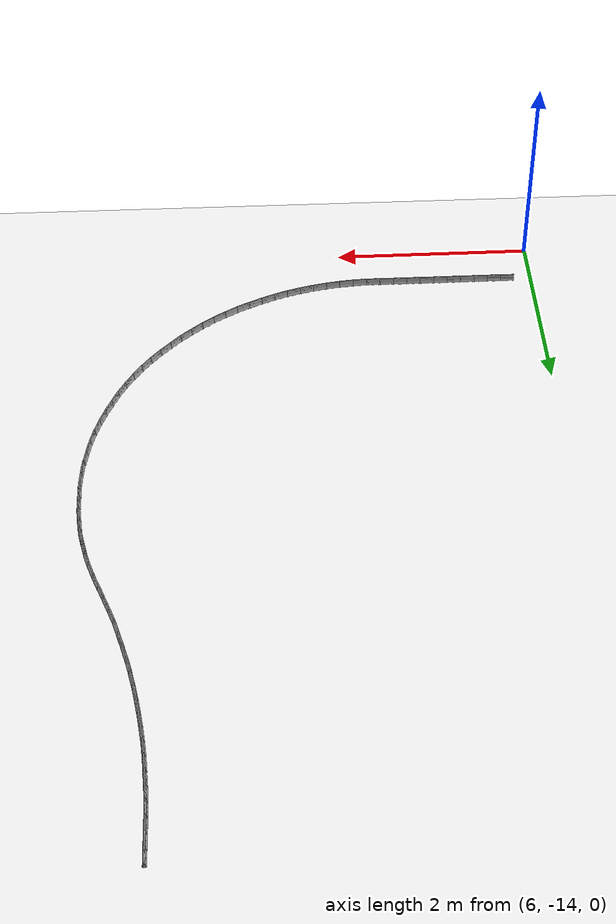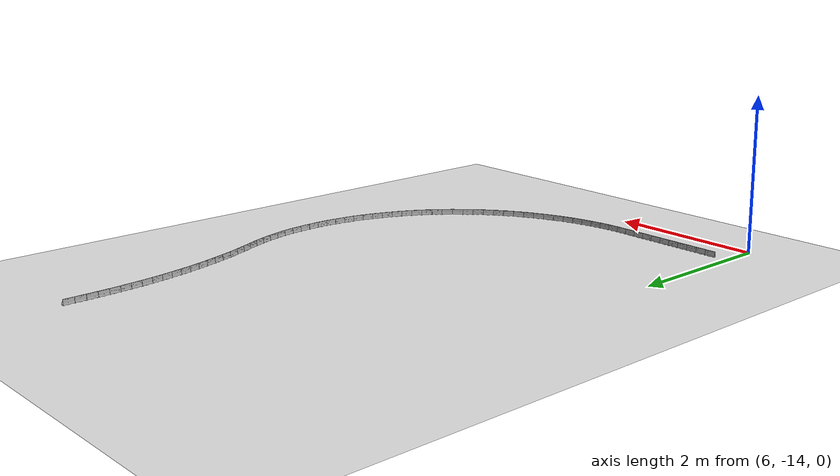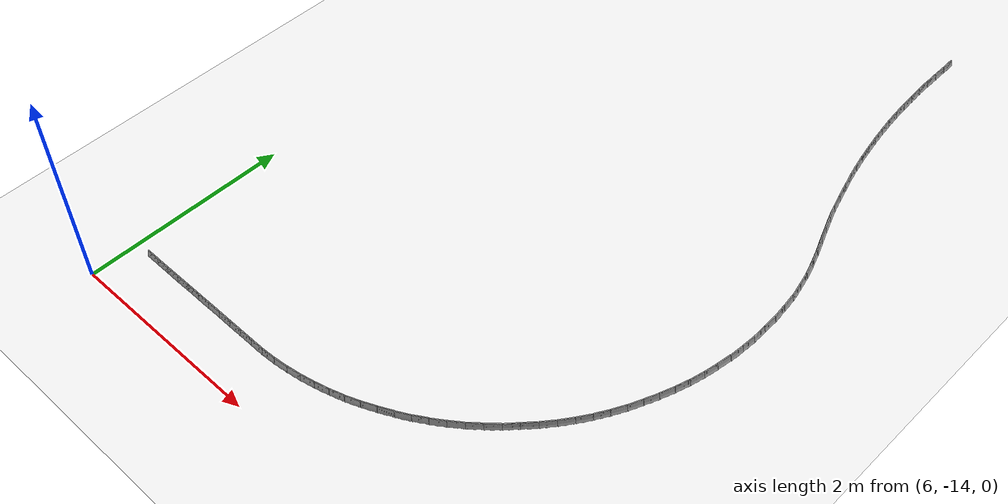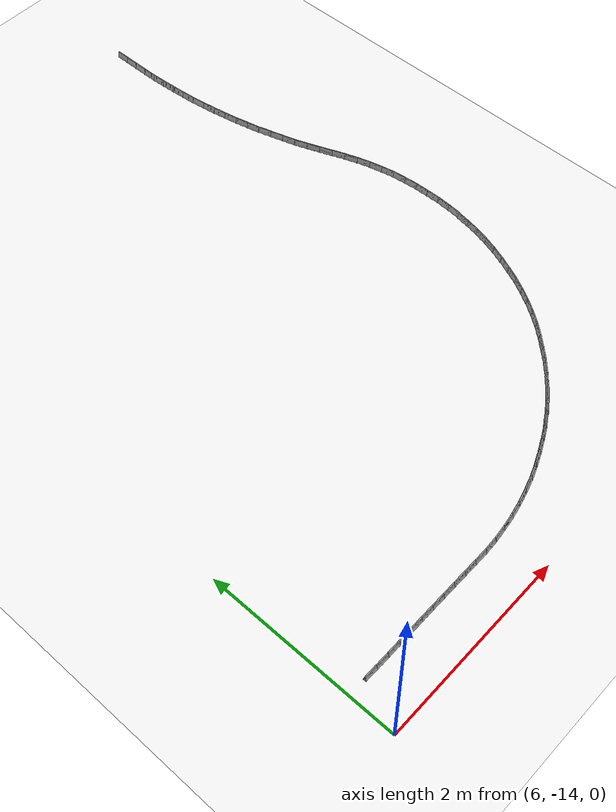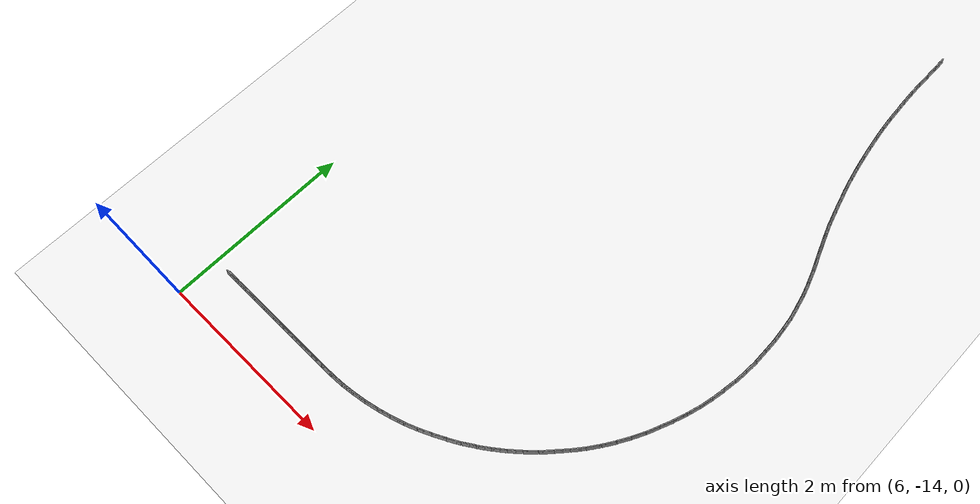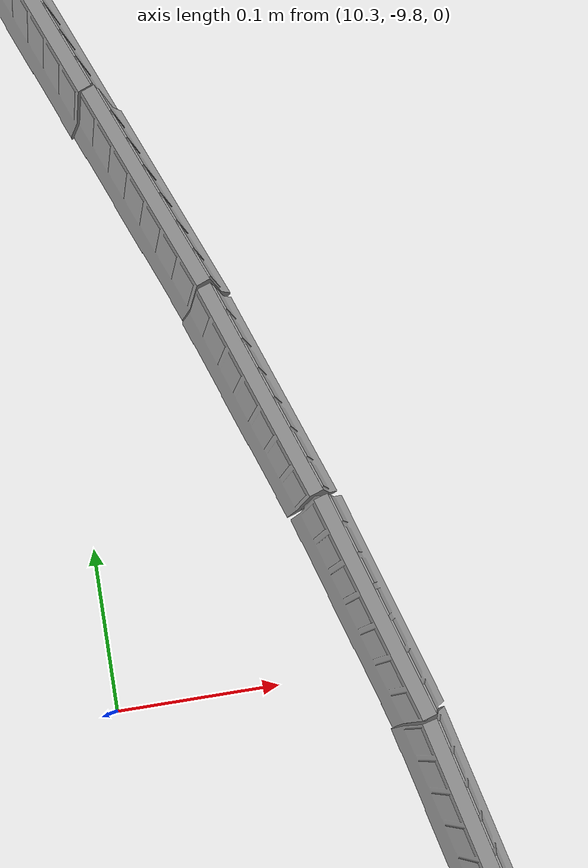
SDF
<sdf version="1.6">
 <world name="bfmc_official">
  <gravity>0 0 -9.8</gravity>
  <light name="c1" type="point">
   <pose>0 0 2 0 -0 0</pose>
   <diffuse>125 125 125 125</diffuse>
   <specular>50 50 50 50</specular>
   <attenuation><range>20</range><constant>0.3</constant><quadratic>0</quadratic><linear>0</linear></attenuation>
   <cast_shadows>0</cast_shadows>
   <direction>0 0 -1</direction>
  </light>
  <light name="c2" type="point">
   <pose>15 0 2 0 -0 0</pose>
   <diffuse>125 125 125 125</diffuse>
   <specular>50 50 50 50</specular>
   <attenuation><range>20</range><constant>0.3</constant><quadratic>0</quadratic><linear>0</linear></attenuation>
   <cast_shadows>0</cast_shadows>
   <direction>0 0 -1</direction>
  </light>
  <light name="c3" type="point">
   <pose>0 -15 2 0 -0 0</pose>
   <diffuse>125 125 125 125</diffuse>
   <specular>50 50 50 50</specular>
   <attenuation><range>20</range><constant>0.3</constant><quadratic>0</quadratic><linear>0</linear></attenuation>
   <cast_shadows>0</cast_shadows>
   <direction>0 0 -1</direction>
  </light>
  <light name="c4" type="point">
   <pose>15 -15 2 0 -0 0</pose>
   <diffuse>125 125 125 125</diffuse>
   <specular>50 50 50 50</specular>
   <attenuation><range>50</range><constant>0.3</constant><quadratic>0</quadratic><linear>0</linear></attenuation>
   <cast_shadows>0</cast_shadows>
   <direction>0 0 -1</direction>
  </light>
  <model name="track">
   <static>1</static>
   <link name="link">
    <collision name="collision">
     <geometry><plane><normal>0 0 1</normal><size>14.68 14.99</size></plane></geometry>
     <surface>
      <contact><collide_bitmask>65535</collide_bitmask></contact>
      <friction><ode><mu>1</mu><mu2>1</mu2></ode></friction>
     </surface>
    </collision>
    <visual name="visual">
     <geometry><plane><normal>0 0 1</normal><size>14.68 14.99</size></plane></geometry>
     <material>
      <ambient>1 1 1 1</ambient>
      <diffuse>1 1 1 1</diffuse>
      <specular>0 0 0 0</specular>
      <emissive>1 1 1 1</emissive>
     </material>
    </visual>
   </link>
   <pose>7.34 -7.495 0 0 -0 0</pose>
  </model>
  <magnetic_field>6e-06 2.3e-05 -4.2e-05</magnetic_field>
  <atmosphere type="adiabatic"/>
  <physics name="default_physics" default="0" type="ode">
   <max_step_size>0.001</max_step_size>
   <real_time_factor>1</real_time_factor>
   <real_time_update_rate>1000</real_time_update_rate>
  </physics>
  <scene><ambient>0.4 0.4 0.4 1</ambient><background>0.7 0.7 0.7 1</background><shadows>1</shadows></scene>
  <audio><device>default</device></audio>
  <spherical_coordinates>
   <surface_model>EARTH_WGS84</surface_model>
   <latitude_deg>0</latitude_deg>
   <longitude_deg>0</longitude_deg>
   <elevation>0</elevation>
   <heading_deg>0</heading_deg>
  </spherical_coordinates>
  <model name="separator_clone">
   <link name="separator::separator::link_0">
    <inertial>
     <mass>1</mass>
     <inertia>
      <ixx>0.166667</ixx>
      <ixy>0</ixy>
      <ixz>0</ixz>
      <iyy>0.166667</iyy>
      <iyz>0</iyz>
      <izz>0.166667</izz>
     </inertia>
    </inertial>
    <visual name="visual">
     <geometry><mesh><uri>model://separator/meshes/separator.dae</uri><scale>1 1 1</scale></mesh></geometry>
     <material>
      <lighting>1</lighting>
      <script><uri>file://media/materials/scripts/gazebo.material</uri><name>Gazebo/Gray</name></script>
      <shader type="vertex"><normal_map>__default__</normal_map></shader>
      <ambient>0.3 0.3 0.3 1</ambient>
      <diffuse>0.7 0.7 0.7 1</diffuse>
      <specular>0.01 0.01 0.01 1</specular>
      <emissive>0 0 0 1</emissive>
     </material>
    </visual>
    <collision name="collision">
     <geometry><mesh><uri>model://separator/meshes/separator.dae</uri><scale>1 1 1</scale></mesh></geometry>
     <surface>
      <friction>
       <ode><mu>1</mu><mu2>1</mu2><fdir1>0 0 0</fdir1><slip1>0</slip1><slip2>0</slip2></ode>
       <torsional>
        <coefficient>1</coefficient>
        <patch_radius>0</patch_radius>
        <surface_radius>0</surface_radius>
        <use_patch_radius>1</use_patch_radius>
        <ode><slip>0</slip></ode>
       </torsional>
      </friction>
      <bounce><restitution_coefficient>0</restitution_coefficient><threshold>1e+06</threshold></bounce>
      <contact>
       <collide_without_contact>0</collide_without_contact>
       <collide_without_contact_bitmask>1</collide_without_contact_bitmask>
       <collide_bitmask>1</collide_bitmask>
       <ode>
        <soft_cfm>0</soft_cfm>
        <soft_erp>0.2</soft_erp>
        <kp>1e+13</kp>
        <kd>1</kd>
        <max_vel>0.01</max_vel>
        <min_depth>0</min_depth>
       </ode>
       <bullet>
        <split_impulse>1</split_impulse>
        <split_impulse_penetration_threshold>-0.01</split_impulse_penetration_threshold>
        <soft_cfm>0</soft_cfm>
        <soft_erp>0.2</soft_erp>
        <kp>1e+13</kp>
        <kd>1</kd>
       </bullet>
      </contact>
     </surface>
    </collision>
   </link>
   <static>1</static>
   <pose>6.38806 -13.5317 0.044642 0 -0 1.57324</pose>
  </model>
  <model name="separator_clone_clone">
   <link name="separator::separator::link_0">
    <inertial>
     <mass>1</mass>
     <inertia>
      <ixx>0.166667</ixx>
      <ixy>0</ixy>
      <ixz>0</ixz>
      <iyy>0.166667</iyy>
      <iyz>0</iyz>
      <izz>0.166667</izz>
     </inertia>
    </inertial>
    <visual name="visual">
     <geometry><mesh><uri>model://separator/meshes/separator.dae</uri><scale>1 1 1</scale></mesh></geometry>
     <material>
      <lighting>1</lighting>
      <script><uri>file://media/materials/scripts/gazebo.material</uri><name>Gazebo/Gray</name></script>
      <shader type="vertex"><normal_map>__default__</normal_map></shader>
      <ambient>0.3 0.3 0.3 1</ambient>
      <diffuse>0.7 0.7 0.7 1</diffuse>
      <specular>0.01 0.01 0.01 1</specular>
      <emissive>0 0 0 1</emissive>
     </material>
    </visual>
    <collision name="collision">
     <geometry><mesh><uri>model://separator/meshes/separator.dae</uri><scale>1 1 1</scale></mesh></geometry>
     <surface>
      <friction>
       <ode><mu>1</mu><mu2>1</mu2><fdir1>0 0 0</fdir1><slip1>0</slip1><slip2>0</slip2></ode>
       <torsional>
        <coefficient>1</coefficient>
        <patch_radius>0</patch_radius>
        <surface_radius>0</surface_radius>
        <use_patch_radius>1</use_patch_radius>
        <ode><slip>0</slip></ode>
       </torsional>
      </friction>
      <bounce><restitution_coefficient>0</restitution_coefficient><threshold>1e+06</threshold></bounce>
      <contact>
       <collide_without_contact>0</collide_without_contact>
       <collide_without_contact_bitmask>1</collide_without_contact_bitmask>
       <collide_bitmask>1</collide_bitmask>
       <ode>
        <soft_cfm>0</soft_cfm>
        <soft_erp>0.2</soft_erp>
        <kp>1e+13</kp>
        <kd>1</kd>
        <max_vel>0.01</max_vel>
        <min_depth>0</min_depth>
       </ode>
       <bullet>
        <split_impulse>1</split_impulse>
        <split_impulse_penetration_threshold>-0.01</split_impulse_penetration_threshold>
        <soft_cfm>0</soft_cfm>
        <soft_erp>0.2</soft_erp>
        <kp>1e+13</kp>
        <kd>1</kd>
       </bullet>
      </contact>
     </surface>
    </collision>
   </link>
   <static>1</static>
   <pose>6.52931 -13.5311 0.044642 0 -0 1.57324</pose>
  </model>
  <model name="separator_clone_clone_clone">
   <link name="separator::separator::link_0">
    <inertial>
     <mass>1</mass>
     <inertia>
      <ixx>0.166667</ixx>
      <ixy>0</ixy>
      <ixz>0</ixz>
      <iyy>0.166667</iyy>
      <iyz>0</iyz>
      <izz>0.166667</izz>
     </inertia>
    </inertial>
    <visual name="visual">
     <geometry><mesh><uri>model://separator/meshes/separator.dae</uri><scale>1 1 1</scale></mesh></geometry>
     <material>
      <lighting>1</lighting>
      <script><uri>file://media/materials/scripts/gazebo.material</uri><name>Gazebo/Gray</name></script>
      <shader type="vertex"><normal_map>__default__</normal_map></shader>
      <ambient>0.3 0.3 0.3 1</ambient>
      <diffuse>0.7 0.7 0.7 1</diffuse>
      <specular>0.01 0.01 0.01 1</specular>
      <emissive>0 0 0 1</emissive>
     </material>
    </visual>
    <collision name="collision">
     <geometry><mesh><uri>model://separator/meshes/separator.dae</uri><scale>1 1 1</scale></mesh></geometry>
     <surface>
      <friction>
       <ode><mu>1</mu><mu2>1</mu2><fdir1>0 0 0</fdir1><slip1>0</slip1><slip2>0</slip2></ode>
       <torsional>
        <coefficient>1</coefficient>
        <patch_radius>0</patch_radius>
        <surface_radius>0</surface_radius>
        <use_patch_radius>1</use_patch_radius>
        <ode><slip>0</slip></ode>
       </torsional>
      </friction>
      <bounce><restitution_coefficient>0</restitution_coefficient><threshold>1e+06</threshold></bounce>
      <contact>
       <collide_without_contact>0</collide_without_contact>
       <collide_without_contact_bitmask>1</collide_without_contact_bitmask>
       <collide_bitmask>1</collide_bitmask>
       <ode>
        <soft_cfm>0</soft_cfm>
        <soft_erp>0.2</soft_erp>
        <kp>1e+13</kp>
        <kd>1</kd>
        <max_vel>0.01</max_vel>
        <min_depth>0</min_depth>
       </ode>
       <bullet>
        <split_impulse>1</split_impulse>
        <split_impulse_penetration_threshold>-0.01</split_impulse_penetration_threshold>
        <soft_cfm>0</soft_cfm>
        <soft_erp>0.2</soft_erp>
        <kp>1e+13</kp>
        <kd>1</kd>
       </bullet>
      </contact>
     </surface>
    </collision>
   </link>
   <static>1</static>
   <pose>6.67069 -13.5307 0.044642 0 -0 1.57324</pose>
  </model>
  <model name="separator_clone_clone_clone_clone">
   <link name="separator::separator::link_0">
    <inertial>
     <mass>1</mass>
     <inertia>
      <ixx>0.166667</ixx>
      <ixy>0</ixy>
      <ixz>0</ixz>
      <iyy>0.166667</iyy>
      <iyz>0</iyz>
      <izz>0.166667</izz>
     </inertia>
    </inertial>
    <visual name="visual">
     <geometry><mesh><uri>model://separator/meshes/separator.dae</uri><scale>1 1 1</scale></mesh></geometry>
     <material>
      <lighting>1</lighting>
      <script><uri>file://media/materials/scripts/gazebo.material</uri><name>Gazebo/Gray</name></script>
      <shader type="vertex"><normal_map>__default__</normal_map></shader>
      <ambient>0.3 0.3 0.3 1</ambient>
      <diffuse>0.7 0.7 0.7 1</diffuse>
      <specular>0.01 0.01 0.01 1</specular>
      <emissive>0 0 0 1</emissive>
     </material>
    </visual>
    <collision name="collision">
     <geometry><mesh><uri>model://separator/meshes/separator.dae</uri><scale>1 1 1</scale></mesh></geometry>
     <surface>
      <friction>
       <ode><mu>1</mu><mu2>1</mu2><fdir1>0 0 0</fdir1><slip1>0</slip1><slip2>0</slip2></ode>
       <torsional>
        <coefficient>1</coefficient>
        <patch_radius>0</patch_radius>
        <surface_radius>0</surface_radius>
        <use_patch_radius>1</use_patch_radius>
        <ode><slip>0</slip></ode>
       </torsional>
      </friction>
      <bounce><restitution_coefficient>0</restitution_coefficient><threshold>1e+06</threshold></bounce>
      <contact>
       <collide_without_contact>0</collide_without_contact>
       <collide_without_contact_bitmask>1</collide_without_contact_bitmask>
       <collide_bitmask>1</collide_bitmask>
       <ode>
        <soft_cfm>0</soft_cfm>
        <soft_erp>0.2</soft_erp>
        <kp>1e+13</kp>
        <kd>1</kd>
        <max_vel>0.01</max_vel>
        <min_depth>0</min_depth>
       </ode>
       <bullet>
        <split_impulse>1</split_impulse>
        <split_impulse_penetration_threshold>-0.01</split_impulse_penetration_threshold>
        <soft_cfm>0</soft_cfm>
        <soft_erp>0.2</soft_erp>
        <kp>1e+13</kp>
        <kd>1</kd>
       </bullet>
      </contact>
     </surface>
    </collision>
   </link>
   <static>1</static>
   <pose>6.81255 -13.5305 0.044642 0 -0 1.57324</pose>
  </model>
  <model name="separator_clone_clone_clone_clone_clone">
   <link name="separator::separator::link_0">
    <inertial>
     <mass>1</mass>
     <inertia>
      <ixx>0.166667</ixx>
      <ixy>0</ixy>
      <ixz>0</ixz>
      <iyy>0.166667</iyy>
      <iyz>0</iyz>
      <izz>0.166667</izz>
     </inertia>
    </inertial>
    <visual name="visual">
     <geometry><mesh><uri>model://separator/meshes/separator.dae</uri><scale>1 1 1</scale></mesh></geometry>
     <material>
      <lighting>1</lighting>
      <script><uri>file://media/materials/scripts/gazebo.material</uri><name>Gazebo/Gray</name></script>
      <shader type="vertex"><normal_map>__default__</normal_map></shader>
      <ambient>0.3 0.3 0.3 1</ambient>
      <diffuse>0.7 0.7 0.7 1</diffuse>
      <specular>0.01 0.01 0.01 1</specular>
      <emissive>0 0 0 1</emissive>
     </material>
    </visual>
    <collision name="collision">
     <geometry><mesh><uri>model://separator/meshes/separator.dae</uri><scale>1 1 1</scale></mesh></geometry>
     <surface>
      <friction>
       <ode><mu>1</mu><mu2>1</mu2><fdir1>0 0 0</fdir1><slip1>0</slip1><slip2>0</slip2></ode>
       <torsional>
        <coefficient>1</coefficient>
        <patch_radius>0</patch_radius>
        <surface_radius>0</surface_radius>
        <use_patch_radius>1</use_patch_radius>
        <ode><slip>0</slip></ode>
       </torsional>
      </friction>
      <bounce><restitution_coefficient>0</restitution_coefficient><threshold>1e+06</threshold></bounce>
      <contact>
       <collide_without_contact>0</collide_without_contact>
       <collide_without_contact_bitmask>1</collide_without_contact_bitmask>
       <collide_bitmask>1</collide_bitmask>
       <ode>
        <soft_cfm>0</soft_cfm>
        <soft_erp>0.2</soft_erp>
        <kp>1e+13</kp>
        <kd>1</kd>
        <max_vel>0.01</max_vel>
        <min_depth>0</min_depth>
       </ode>
       <bullet>
        <split_impulse>1</split_impulse>
        <split_impulse_penetration_threshold>-0.01</split_impulse_penetration_threshold>
        <soft_cfm>0</soft_cfm>
        <soft_erp>0.2</soft_erp>
        <kp>1e+13</kp>
        <kd>1</kd>
       </bullet>
      </contact>
     </surface>
    </collision>
   </link>
   <static>1</static>
   <pose>6.95349 -13.5302 0.044642 0 -0 1.57324</pose>
  </model>
  <model name="separator_clone_clone_clone_clone_clone_clone">
   <link name="separator::separator::link_0">
    <inertial>
     <mass>1</mass>
     <inertia>
      <ixx>0.166667</ixx>
      <ixy>0</ixy>
      <ixz>0</ixz>
      <iyy>0.166667</iyy>
      <iyz>0</iyz>
      <izz>0.166667</izz>
     </inertia>
    </inertial>
    <visual name="visual">
     <geometry><mesh><uri>model://separator/meshes/separator.dae</uri><scale>1 1 1</scale></mesh></geometry>
     <material>
      <lighting>1</lighting>
      <script><uri>file://media/materials/scripts/gazebo.material</uri><name>Gazebo/Gray</name></script>
      <shader type="vertex"><normal_map>__default__</normal_map></shader>
      <ambient>0.3 0.3 0.3 1</ambient>
      <diffuse>0.7 0.7 0.7 1</diffuse>
      <specular>0.01 0.01 0.01 1</specular>
      <emissive>0 0 0 1</emissive>
     </material>
    </visual>
    <collision name="collision">
     <geometry><mesh><uri>model://separator/meshes/separator.dae</uri><scale>1 1 1</scale></mesh></geometry>
     <surface>
      <friction>
       <ode><mu>1</mu><mu2>1</mu2><fdir1>0 0 0</fdir1><slip1>0</slip1><slip2>0</slip2></ode>
       <torsional>
        <coefficient>1</coefficient>
        <patch_radius>0</patch_radius>
        <surface_radius>0</surface_radius>
        <use_patch_radius>1</use_patch_radius>
        <ode><slip>0</slip></ode>
       </torsional>
      </friction>
      <bounce><restitution_coefficient>0</restitution_coefficient><threshold>1e+06</threshold></bounce>
      <contact>
       <collide_without_contact>0</collide_without_contact>
       <collide_without_contact_bitmask>1</collide_without_contact_bitmask>
       <collide_bitmask>1</collide_bitmask>
       <ode>
        <soft_cfm>0</soft_cfm>
        <soft_erp>0.2</soft_erp>
        <kp>1e+13</kp>
        <kd>1</kd>
        <max_vel>0.01</max_vel>
        <min_depth>0</min_depth>
       </ode>
       <bullet>
        <split_impulse>1</split_impulse>
        <split_impulse_penetration_threshold>-0.01</split_impulse_penetration_threshold>
        <soft_cfm>0</soft_cfm>
        <soft_erp>0.2</soft_erp>
        <kp>1e+13</kp>
        <kd>1</kd>
       </bullet>
      </contact>
     </surface>
    </collision>
   </link>
   <static>1</static>
   <pose>7.09476 -13.5299 0.044642 0 -0 1.57324</pose>
  </model>
  <model name="separator_clone_clone_clone_clone_clone_clone_clone">
   <link name="separator::separator::link_0">
    <inertial>
     <mass>1</mass>
     <inertia>
      <ixx>0.166667</ixx>
      <ixy>0</ixy>
      <ixz>0</ixz>
      <iyy>0.166667</iyy>
      <iyz>0</iyz>
      <izz>0.166667</izz>
     </inertia>
    </inertial>
    <visual name="visual">
     <geometry><mesh><uri>model://separator/meshes/separator.dae</uri><scale>1 1 1</scale></mesh></geometry>
     <material>
      <lighting>1</lighting>
      <script><uri>file://media/materials/scripts/gazebo.material</uri><name>Gazebo/Gray</name></script>
      <shader type="vertex"><normal_map>__default__</normal_map></shader>
      <ambient>0.3 0.3 0.3 1</ambient>
      <diffuse>0.7 0.7 0.7 1</diffuse>
      <specular>0.01 0.01 0.01 1</specular>
      <emissive>0 0 0 1</emissive>
     </material>
    </visual>
    <collision name="collision">
     <geometry><mesh><uri>model://separator/meshes/separator.dae</uri><scale>1 1 1</scale></mesh></geometry>
     <surface>
      <friction>
       <ode><mu>1</mu><mu2>1</mu2><fdir1>0 0 0</fdir1><slip1>0</slip1><slip2>0</slip2></ode>
       <torsional>
        <coefficient>1</coefficient>
        <patch_radius>0</patch_radius>
        <surface_radius>0</surface_radius>
        <use_patch_radius>1</use_patch_radius>
        <ode><slip>0</slip></ode>
       </torsional>
      </friction>
      <bounce><restitution_coefficient>0</restitution_coefficient><threshold>1e+06</threshold></bounce>
      <contact>
       <collide_without_contact>0</collide_without_contact>
       <collide_without_contact_bitmask>1</collide_without_contact_bitmask>
       <collide_bitmask>1</collide_bitmask>
       <ode>
        <soft_cfm>0</soft_cfm>
        <soft_erp>0.2</soft_erp>
        <kp>1e+13</kp>
        <kd>1</kd>
        <max_vel>0.01</max_vel>
        <min_depth>0</min_depth>
       </ode>
       <bullet>
        <split_impulse>1</split_impulse>
        <split_impulse_penetration_threshold>-0.01</split_impulse_penetration_threshold>
        <soft_cfm>0</soft_cfm>
        <soft_erp>0.2</soft_erp>
        <kp>1e+13</kp>
        <kd>1</kd>
       </bullet>
      </contact>
     </surface>
    </collision>
   </link>
   <static>1</static>
   <pose>7.23664 -13.5303 0.044642 0 -0 1.57324</pose>
  </model>
  <model name="separator_clone_clone_clone_clone_clone_clone_clone_clone">
   <link name="separator::separator::link_0">
    <inertial>
     <mass>1</mass>
     <inertia>
      <ixx>0.166667</ixx>
      <ixy>0</ixy>
      <ixz>0</ixz>
      <iyy>0.166667</iyy>
      <iyz>0</iyz>
      <izz>0.166667</izz>
     </inertia>
    </inertial>
    <visual name="visual">
     <geometry><mesh><uri>model://separator/meshes/separator.dae</uri><scale>1 1 1</scale></mesh></geometry>
     <material>
      <lighting>1</lighting>
      <script><uri>file://media/materials/scripts/gazebo.material</uri><name>Gazebo/Gray</name></script>
      <shader type="vertex"><normal_map>__default__</normal_map></shader>
      <ambient>0.3 0.3 0.3 1</ambient>
      <diffuse>0.7 0.7 0.7 1</diffuse>
      <specular>0.01 0.01 0.01 1</specular>
      <emissive>0 0 0 1</emissive>
     </material>
    </visual>
    <collision name="collision">
     <geometry><mesh><uri>model://separator/meshes/separator.dae</uri><scale>1 1 1</scale></mesh></geometry>
     <surface>
      <friction>
       <ode><mu>1</mu><mu2>1</mu2><fdir1>0 0 0</fdir1><slip1>0</slip1><slip2>0</slip2></ode>
       <torsional>
        <coefficient>1</coefficient>
        <patch_radius>0</patch_radius>
        <surface_radius>0</surface_radius>
        <use_patch_radius>1</use_patch_radius>
        <ode><slip>0</slip></ode>
       </torsional>
      </friction>
      <bounce><restitution_coefficient>0</restitution_coefficient><threshold>1e+06</threshold></bounce>
      <contact>
       <collide_without_contact>0</collide_without_contact>
       <collide_without_contact_bitmask>1</collide_without_contact_bitmask>
       <collide_bitmask>1</collide_bitmask>
       <ode>
        <soft_cfm>0</soft_cfm>
        <soft_erp>0.2</soft_erp>
        <kp>1e+13</kp>
        <kd>1</kd>
        <max_vel>0.01</max_vel>
        <min_depth>0</min_depth>
       </ode>
       <bullet>
        <split_impulse>1</split_impulse>
        <split_impulse_penetration_threshold>-0.01</split_impulse_penetration_threshold>
        <soft_cfm>0</soft_cfm>
        <soft_erp>0.2</soft_erp>
        <kp>1e+13</kp>
        <kd>1</kd>
       </bullet>
      </contact>
     </surface>
    </collision>
   </link>
   <static>1</static>
   <pose>7.37782 -13.5302 0.044642 0 -0 1.57324</pose>
  </model>
  <model name="separator_clone_clone_clone_clone_clone_clone_clone_clone_0">
   <link name="separator::separator::link_0">
    <inertial>
     <mass>1</mass>
     <inertia>
      <ixx>0.166667</ixx>
      <ixy>0</ixy>
      <ixz>0</ixz>
      <iyy>0.166667</iyy>
      <iyz>0</iyz>
      <izz>0.166667</izz>
     </inertia>
    </inertial>
    <visual name="visual">
     <geometry><mesh><uri>model://separator/meshes/separator.dae</uri><scale>1 1 1</scale></mesh></geometry>
     <material>
      <lighting>1</lighting>
      <script><uri>file://media/materials/scripts/gazebo.material</uri><name>Gazebo/Gray</name></script>
      <shader type="vertex"><normal_map>__default__</normal_map></shader>
      <ambient>0.3 0.3 0.3 1</ambient>
      <diffuse>0.7 0.7 0.7 1</diffuse>
      <specular>0.01 0.01 0.01 1</specular>
      <emissive>0 0 0 1</emissive>
     </material>
    </visual>
    <collision name="collision">
     <geometry><mesh><uri>model://separator/meshes/separator.dae</uri><scale>1 1 1</scale></mesh></geometry>
     <surface>
      <friction>
       <ode><mu>1</mu><mu2>1</mu2><fdir1>0 0 0</fdir1><slip1>0</slip1><slip2>0</slip2></ode>
       <torsional>
        <coefficient>1</coefficient>
        <patch_radius>0</patch_radius>
        <surface_radius>0</surface_radius>
        <use_patch_radius>1</use_patch_radius>
        <ode><slip>0</slip></ode>
       </torsional>
      </friction>
      <bounce><restitution_coefficient>0</restitution_coefficient><threshold>1e+06</threshold></bounce>
      <contact>
       <collide_without_contact>0</collide_without_contact>
       <collide_without_contact_bitmask>1</collide_without_contact_bitmask>
       <collide_bitmask>1</collide_bitmask>
       <ode>
        <soft_cfm>0</soft_cfm>
        <soft_erp>0.2</soft_erp>
        <kp>1e+13</kp>
        <kd>1</kd>
        <max_vel>0.01</max_vel>
        <min_depth>0</min_depth>
       </ode>
       <bullet>
        <split_impulse>1</split_impulse>
        <split_impulse_penetration_threshold>-0.01</split_impulse_penetration_threshold>
        <soft_cfm>0</soft_cfm>
        <soft_erp>0.2</soft_erp>
        <kp>1e+13</kp>
        <kd>1</kd>
       </bullet>
      </contact>
     </surface>
    </collision>
   </link>
   <static>1</static>
   <pose>7.51909 -13.5303 0.044642 0 -0 1.57324</pose>
  </model>
  <model name="separator_clone_clone_clone_clone_clone_clone_clone_clone_1">
   <link name="separator::separator::link_0">
    <inertial>
     <mass>1</mass>
     <inertia>
      <ixx>0.166667</ixx>
      <ixy>0</ixy>
      <ixz>0</ixz>
      <iyy>0.166667</iyy>
      <iyz>0</iyz>
      <izz>0.166667</izz>
     </inertia>
    </inertial>
    <visual name="visual">
     <geometry><mesh><uri>model://separator/meshes/separator.dae</uri><scale>1 1 1</scale></mesh></geometry>
     <material>
      <lighting>1</lighting>
      <script><uri>file://media/materials/scripts/gazebo.material</uri><name>Gazebo/Gray</name></script>
      <shader type="vertex"><normal_map>__default__</normal_map></shader>
      <ambient>0.3 0.3 0.3 1</ambient>
      <diffuse>0.7 0.7 0.7 1</diffuse>
      <specular>0.01 0.01 0.01 1</specular>
      <emissive>0 0 0 1</emissive>
     </material>
    </visual>
    <collision name="collision">
     <geometry><mesh><uri>model://separator/meshes/separator.dae</uri><scale>1 1 1</scale></mesh></geometry>
     <surface>
      <friction>
       <ode><mu>1</mu><mu2>1</mu2><fdir1>0 0 0</fdir1><slip1>0</slip1><slip2>0</slip2></ode>
       <torsional>
        <coefficient>1</coefficient>
        <patch_radius>0</patch_radius>
        <surface_radius>0</surface_radius>
        <use_patch_radius>1</use_patch_radius>
        <ode><slip>0</slip></ode>
       </torsional>
      </friction>
      <bounce><restitution_coefficient>0</restitution_coefficient><threshold>1e+06</threshold></bounce>
      <contact>
       <collide_without_contact>0</collide_without_contact>
       <collide_without_contact_bitmask>1</collide_without_contact_bitmask>
       <collide_bitmask>1</collide_bitmask>
       <ode>
        <soft_cfm>0</soft_cfm>
        <soft_erp>0.2</soft_erp>
        <kp>1e+13</kp>
        <kd>1</kd>
        <max_vel>0.01</max_vel>
        <min_depth>0</min_depth>
       </ode>
       <bullet>
        <split_impulse>1</split_impulse>
        <split_impulse_penetration_threshold>-0.01</split_impulse_penetration_threshold>
        <soft_cfm>0</soft_cfm>
        <soft_erp>0.2</soft_erp>
        <kp>1e+13</kp>
        <kd>1</kd>
       </bullet>
      </contact>
     </surface>
    </collision>
   </link>
   <static>1</static>
   <pose>7.66047 -13.5302 0.044642 0 -0 1.57324</pose>
  </model>
  <model name="separator_clone_clone_clone_clone_clone_clone_clone_clone_2">
   <link name="separator::separator::link_0">
    <inertial>
     <mass>1</mass>
     <inertia>
      <ixx>0.166667</ixx>
      <ixy>0</ixy>
      <ixz>0</ixz>
      <iyy>0.166667</iyy>
      <iyz>0</iyz>
      <izz>0.166667</izz>
     </inertia>
    </inertial>
    <visual name="visual">
     <geometry><mesh><uri>model://separator/meshes/separator.dae</uri><scale>1 1 1</scale></mesh></geometry>
     <material>
      <lighting>1</lighting>
      <script><uri>file://media/materials/scripts/gazebo.material</uri><name>Gazebo/Gray</name></script>
      <shader type="vertex"><normal_map>__default__</normal_map></shader>
      <ambient>0.3 0.3 0.3 1</ambient>
      <diffuse>0.7 0.7 0.7 1</diffuse>
      <specular>0.01 0.01 0.01 1</specular>
      <emissive>0 0 0 1</emissive>
     </material>
    </visual>
    <collision name="collision">
     <geometry><mesh><uri>model://separator/meshes/separator.dae</uri><scale>1 1 1</scale></mesh></geometry>
     <surface>
      <friction>
       <ode><mu>1</mu><mu2>1</mu2><fdir1>0 0 0</fdir1><slip1>0</slip1><slip2>0</slip2></ode>
       <torsional>
        <coefficient>1</coefficient>
        <patch_radius>0</patch_radius>
        <surface_radius>0</surface_radius>
        <use_patch_radius>1</use_patch_radius>
        <ode><slip>0</slip></ode>
       </torsional>
      </friction>
      <bounce><restitution_coefficient>0</restitution_coefficient><threshold>1e+06</threshold></bounce>
      <contact>
       <collide_without_contact>0</collide_without_contact>
       <collide_without_contact_bitmask>1</collide_without_contact_bitmask>
       <collide_bitmask>1</collide_bitmask>
       <ode>
        <soft_cfm>0</soft_cfm>
        <soft_erp>0.2</soft_erp>
        <kp>1e+13</kp>
        <kd>1</kd>
        <max_vel>0.01</max_vel>
        <min_depth>0</min_depth>
       </ode>
       <bullet>
        <split_impulse>1</split_impulse>
        <split_impulse_penetration_threshold>-0.01</split_impulse_penetration_threshold>
        <soft_cfm>0</soft_cfm>
        <soft_erp>0.2</soft_erp>
        <kp>1e+13</kp>
        <kd>1</kd>
       </bullet>
      </contact>
     </surface>
    </collision>
   </link>
   <static>1</static>
   <pose>7.80241 -13.5261 0.044642 0 -0 1.62929</pose>
  </model>
  <model name="separator_clone_clone_clone_clone_clone_clone_clone_clone_2_clone">
   <link name="separator::separator::link_0">
    <inertial>
     <mass>1</mass>
     <inertia>
      <ixx>0.166667</ixx>
      <ixy>0</ixy>
      <ixz>0</ixz>
      <iyy>0.166667</iyy>
      <iyz>0</iyz>
      <izz>0.166667</izz>
     </inertia>
    </inertial>
    <visual name="visual">
     <geometry><mesh><uri>model://separator/meshes/separator.dae</uri><scale>1 1 1</scale></mesh></geometry>
     <material>
      <lighting>1</lighting>
      <script><uri>file://media/materials/scripts/gazebo.material</uri><name>Gazebo/Gray</name></script>
      <shader type="vertex"><normal_map>__default__</normal_map></shader>
      <ambient>0.3 0.3 0.3 1</ambient>
      <diffuse>0.7 0.7 0.7 1</diffuse>
      <specular>0.01 0.01 0.01 1</specular>
      <emissive>0 0 0 1</emissive>
     </material>
    </visual>
    <collision name="collision">
     <geometry><mesh><uri>model://separator/meshes/separator.dae</uri><scale>1 1 1</scale></mesh></geometry>
     <surface>
      <friction>
       <ode><mu>1</mu><mu2>1</mu2><fdir1>0 0 0</fdir1><slip1>0</slip1><slip2>0</slip2></ode>
       <torsional>
        <coefficient>1</coefficient>
        <patch_radius>0</patch_radius>
        <surface_radius>0</surface_radius>
        <use_patch_radius>1</use_patch_radius>
        <ode><slip>0</slip></ode>
       </torsional>
      </friction>
      <bounce><restitution_coefficient>0</restitution_coefficient><threshold>1e+06</threshold></bounce>
      <contact>
       <collide_without_contact>0</collide_without_contact>
       <collide_without_contact_bitmask>1</collide_without_contact_bitmask>
       <collide_bitmask>1</collide_bitmask>
       <ode>
        <soft_cfm>0</soft_cfm>
        <soft_erp>0.2</soft_erp>
        <kp>1e+13</kp>
        <kd>1</kd>
        <max_vel>0.01</max_vel>
        <min_depth>0</min_depth>
       </ode>
       <bullet>
        <split_impulse>1</split_impulse>
        <split_impulse_penetration_threshold>-0.01</split_impulse_penetration_threshold>
        <soft_cfm>0</soft_cfm>
        <soft_erp>0.2</soft_erp>
        <kp>1e+13</kp>
        <kd>1</kd>
       </bullet>
      </contact>
     </surface>
    </collision>
   </link>
   <static>1</static>
   <pose>7.94451 -13.5142 0.044642 0 -0 1.68163</pose>
  </model>
  <model name="separator_clone_clone_clone_clone_clone_clone_clone_clone_2_clone_clone">
   <link name="separator::separator::link_0">
    <inertial>
     <mass>1</mass>
     <inertia>
      <ixx>0.166667</ixx>
      <ixy>0</ixy>
      <ixz>0</ixz>
      <iyy>0.166667</iyy>
      <iyz>0</iyz>
      <izz>0.166667</izz>
     </inertia>
    </inertial>
    <visual name="visual">
     <geometry><mesh><uri>model://separator/meshes/separator.dae</uri><scale>1 1 1</scale></mesh></geometry>
     <material>
      <lighting>1</lighting>
      <script><uri>file://media/materials/scripts/gazebo.material</uri><name>Gazebo/Gray</name></script>
      <shader type="vertex"><normal_map>__default__</normal_map></shader>
      <ambient>0.3 0.3 0.3 1</ambient>
      <diffuse>0.7 0.7 0.7 1</diffuse>
      <specular>0.01 0.01 0.01 1</specular>
      <emissive>0 0 0 1</emissive>
     </material>
    </visual>
    <collision name="collision">
     <geometry><mesh><uri>model://separator/meshes/separator.dae</uri><scale>1 1 1</scale></mesh></geometry>
     <surface>
      <friction>
       <ode><mu>1</mu><mu2>1</mu2><fdir1>0 0 0</fdir1><slip1>0</slip1><slip2>0</slip2></ode>
       <torsional>
        <coefficient>1</coefficient>
        <patch_radius>0</patch_radius>
        <surface_radius>0</surface_radius>
        <use_patch_radius>1</use_patch_radius>
        <ode><slip>0</slip></ode>
       </torsional>
      </friction>
      <bounce><restitution_coefficient>0</restitution_coefficient><threshold>1e+06</threshold></bounce>
      <contact>
       <collide_without_contact>0</collide_without_contact>
       <collide_without_contact_bitmask>1</collide_without_contact_bitmask>
       <collide_bitmask>1</collide_bitmask>
       <ode>
        <soft_cfm>0</soft_cfm>
        <soft_erp>0.2</soft_erp>
        <kp>1e+13</kp>
        <kd>1</kd>
        <max_vel>0.01</max_vel>
        <min_depth>0</min_depth>
       </ode>
       <bullet>
        <split_impulse>1</split_impulse>
        <split_impulse_penetration_threshold>-0.01</split_impulse_penetration_threshold>
        <soft_cfm>0</soft_cfm>
        <soft_erp>0.2</soft_erp>
        <kp>1e+13</kp>
        <kd>1</kd>
       </bullet>
      </contact>
     </surface>
    </collision>
   </link>
   <static>1</static>
   <pose>8.0853 -13.4952 0.044642 0 -0 1.71814</pose>
  </model>
  <model name="separator_clone_clone_clone_clone_clone_clone_clone_clone_2_clone_clone_clone">
   <link name="separator::separator::link_0">
    <inertial>
     <mass>1</mass>
     <inertia>
      <ixx>0.166667</ixx>
      <ixy>0</ixy>
      <ixz>0</ixz>
      <iyy>0.166667</iyy>
      <iyz>0</iyz>
      <izz>0.166667</izz>
     </inertia>
    </inertial>
    <visual name="visual">
     <geometry><mesh><uri>model://separator/meshes/separator.dae</uri><scale>1 1 1</scale></mesh></geometry>
     <material>
      <lighting>1</lighting>
      <script><uri>file://media/materials/scripts/gazebo.material</uri><name>Gazebo/Gray</name></script>
      <shader type="vertex"><normal_map>__default__</normal_map></shader>
      <ambient>0.3 0.3 0.3 1</ambient>
      <diffuse>0.7 0.7 0.7 1</diffuse>
      <specular>0.01 0.01 0.01 1</specular>
      <emissive>0 0 0 1</emissive>
     </material>
    </visual>
    <collision name="collision">
     <geometry><mesh><uri>model://separator/meshes/separator.dae</uri><scale>1 1 1</scale></mesh></geometry>
     <surface>
      <friction>
       <ode><mu>1</mu><mu2>1</mu2><fdir1>0 0 0</fdir1><slip1>0</slip1><slip2>0</slip2></ode>
       <torsional>
        <coefficient>1</coefficient>
        <patch_radius>0</patch_radius>
        <surface_radius>0</surface_radius>
        <use_patch_radius>1</use_patch_radius>
        <ode><slip>0</slip></ode>
       </torsional>
      </friction>
      <bounce><restitution_coefficient>0</restitution_coefficient><threshold>1e+06</threshold></bounce>
      <contact>
       <collide_without_contact>0</collide_without_contact>
       <collide_without_contact_bitmask>1</collide_without_contact_bitmask>
       <collide_bitmask>1</collide_bitmask>
       <ode>
        <soft_cfm>0</soft_cfm>
        <soft_erp>0.2</soft_erp>
        <kp>1e+13</kp>
        <kd>1</kd>
        <max_vel>0.01</max_vel>
        <min_depth>0</min_depth>
       </ode>
       <bullet>
        <split_impulse>1</split_impulse>
        <split_impulse_penetration_threshold>-0.01</split_impulse_penetration_threshold>
        <soft_cfm>0</soft_cfm>
        <soft_erp>0.2</soft_erp>
        <kp>1e+13</kp>
        <kd>1</kd>
       </bullet>
      </contact>
     </surface>
    </collision>
   </link>
   <static>1</static>
   <pose>8.22385 -13.4698 0.044642 0 -0 1.77492</pose>
  </model>
  <model name="separator_clone_clone_clone_clone_clone_clone_clone_clone_2_clone_clone_clone_clone">
   <link name="separator::separator::link_0">
    <inertial>
     <mass>1</mass>
     <inertia>
      <ixx>0.166667</ixx>
      <ixy>0</ixy>
      <ixz>0</ixz>
      <iyy>0.166667</iyy>
      <iyz>0</iyz>
      <izz>0.166667</izz>
     </inertia>
    </inertial>
    <visual name="visual">
     <geometry><mesh><uri>model://separator/meshes/separator.dae</uri><scale>1 1 1</scale></mesh></geometry>
     <material>
      <lighting>1</lighting>
      <script><uri>file://media/materials/scripts/gazebo.material</uri><name>Gazebo/Gray</name></script>
      <shader type="vertex"><normal_map>__default__</normal_map></shader>
      <ambient>0.3 0.3 0.3 1</ambient>
      <diffuse>0.7 0.7 0.7 1</diffuse>
      <specular>0.01 0.01 0.01 1</specular>
      <emissive>0 0 0 1</emissive>
     </material>
    </visual>
    <collision name="collision">
     <geometry><mesh><uri>model://separator/meshes/separator.dae</uri><scale>1 1 1</scale></mesh></geometry>
     <surface>
      <friction>
       <ode><mu>1</mu><mu2>1</mu2><fdir1>0 0 0</fdir1><slip1>0</slip1><slip2>0</slip2></ode>
       <torsional>
        <coefficient>1</coefficient>
        <patch_radius>0</patch_radius>
        <surface_radius>0</surface_radius>
        <use_patch_radius>1</use_patch_radius>
        <ode><slip>0</slip></ode>
       </torsional>
      </friction>
      <bounce><restitution_coefficient>0</restitution_coefficient><threshold>1e+06</threshold></bounce>
      <contact>
       <collide_without_contact>0</collide_without_contact>
       <collide_without_contact_bitmask>1</collide_without_contact_bitmask>
       <collide_bitmask>1</collide_bitmask>
       <ode>
        <soft_cfm>0</soft_cfm>
        <soft_erp>0.2</soft_erp>
        <kp>1e+13</kp>
        <kd>1</kd>
        <max_vel>0.01</max_vel>
        <min_depth>0</min_depth>
       </ode>
       <bullet>
        <split_impulse>1</split_impulse>
        <split_impulse_penetration_threshold>-0.01</split_impulse_penetration_threshold>
        <soft_cfm>0</soft_cfm>
        <soft_erp>0.2</soft_erp>
        <kp>1e+13</kp>
        <kd>1</kd>
       </bullet>
      </contact>
     </surface>
    </collision>
   </link>
   <static>1</static>
   <pose>8.36199 -13.4377 0.044642 0 -0 1.82339</pose>
  </model>
  <model name="separator_clone_clone_clone_clone_clone_clone_clone_clone_2_clone_clone_clone_clone_clone">
   <link name="separator::separator::link_0">
    <inertial>
     <mass>1</mass>
     <inertia>
      <ixx>0.166667</ixx>
      <ixy>0</ixy>
      <ixz>0</ixz>
      <iyy>0.166667</iyy>
      <iyz>0</iyz>
      <izz>0.166667</izz>
     </inertia>
    </inertial>
    <visual name="visual">
     <geometry><mesh><uri>model://separator/meshes/separator.dae</uri><scale>1 1 1</scale></mesh></geometry>
     <material>
      <lighting>1</lighting>
      <script><uri>file://media/materials/scripts/gazebo.material</uri><name>Gazebo/Gray</name></script>
      <shader type="vertex"><normal_map>__default__</normal_map></shader>
      <ambient>0.3 0.3 0.3 1</ambient>
      <diffuse>0.7 0.7 0.7 1</diffuse>
      <specular>0.01 0.01 0.01 1</specular>
      <emissive>0 0 0 1</emissive>
     </material>
    </visual>
    <collision name="collision">
     <geometry><mesh><uri>model://separator/meshes/separator.dae</uri><scale>1 1 1</scale></mesh></geometry>
     <surface>
      <friction>
       <ode><mu>1</mu><mu2>1</mu2><fdir1>0 0 0</fdir1><slip1>0</slip1><slip2>0</slip2></ode>
       <torsional>
        <coefficient>1</coefficient>
        <patch_radius>0</patch_radius>
        <surface_radius>0</surface_radius>
        <use_patch_radius>1</use_patch_radius>
        <ode><slip>0</slip></ode>
       </torsional>
      </friction>
      <bounce><restitution_coefficient>0</restitution_coefficient><threshold>1e+06</threshold></bounce>
      <contact>
       <collide_without_contact>0</collide_without_contact>
       <collide_without_contact_bitmask>1</collide_without_contact_bitmask>
       <collide_bitmask>1</collide_bitmask>
       <ode>
        <soft_cfm>0</soft_cfm>
        <soft_erp>0.2</soft_erp>
        <kp>1e+13</kp>
        <kd>1</kd>
        <max_vel>0.01</max_vel>
        <min_depth>0</min_depth>
       </ode>
       <bullet>
        <split_impulse>1</split_impulse>
        <split_impulse_penetration_threshold>-0.01</split_impulse_penetration_threshold>
        <soft_cfm>0</soft_cfm>
        <soft_erp>0.2</soft_erp>
        <kp>1e+13</kp>
        <kd>1</kd>
       </bullet>
      </contact>
     </surface>
    </collision>
   </link>
   <static>1</static>
   <pose>8.49966 -13.3986 0.044642 0 -0 1.87376</pose>
  </model>
  <model name="separator_clone_clone_clone_clone_clone_clone_clone_clone_2_clone_clone_clone_clone_clone_clone">
   <link name="separator::separator::link_0">
    <inertial>
     <mass>1</mass>
     <inertia>
      <ixx>0.166667</ixx>
      <ixy>0</ixy>
      <ixz>0</ixz>
      <iyy>0.166667</iyy>
      <iyz>0</iyz>
      <izz>0.166667</izz>
     </inertia>
    </inertial>
    <visual name="visual">
     <geometry><mesh><uri>model://separator/meshes/separator.dae</uri><scale>1 1 1</scale></mesh></geometry>
     <material>
      <lighting>1</lighting>
      <script><uri>file://media/materials/scripts/gazebo.material</uri><name>Gazebo/Gray</name></script>
      <shader type="vertex"><normal_map>__default__</normal_map></shader>
      <ambient>0.3 0.3 0.3 1</ambient>
      <diffuse>0.7 0.7 0.7 1</diffuse>
      <specular>0.01 0.01 0.01 1</specular>
      <emissive>0 0 0 1</emissive>
     </material>
    </visual>
    <collision name="collision">
     <geometry><mesh><uri>model://separator/meshes/separator.dae</uri><scale>1 1 1</scale></mesh></geometry>
     <surface>
      <friction>
       <ode><mu>1</mu><mu2>1</mu2><fdir1>0 0 0</fdir1><slip1>0</slip1><slip2>0</slip2></ode>
       <torsional>
        <coefficient>1</coefficient>
        <patch_radius>0</patch_radius>
        <surface_radius>0</surface_radius>
        <use_patch_radius>1</use_patch_radius>
        <ode><slip>0</slip></ode>
       </torsional>
      </friction>
      <bounce><restitution_coefficient>0</restitution_coefficient><threshold>1e+06</threshold></bounce>
      <contact>
       <collide_without_contact>0</collide_without_contact>
       <collide_without_contact_bitmask>1</collide_without_contact_bitmask>
       <collide_bitmask>1</collide_bitmask>
       <ode>
        <soft_cfm>0</soft_cfm>
        <soft_erp>0.2</soft_erp>
        <kp>1e+13</kp>
        <kd>1</kd>
        <max_vel>0.01</max_vel>
        <min_depth>0</min_depth>
       </ode>
       <bullet>
        <split_impulse>1</split_impulse>
        <split_impulse_penetration_threshold>-0.01</split_impulse_penetration_threshold>
        <soft_cfm>0</soft_cfm>
        <soft_erp>0.2</soft_erp>
        <kp>1e+13</kp>
        <kd>1</kd>
       </bullet>
      </contact>
     </surface>
    </collision>
   </link>
   <static>1</static>
   <pose>8.63562 -13.3529 0.044642 0 -0 1.93725</pose>
  </model>
  <model name="separator_clone_clone_clone_clone_clone_clone_clone_clone_2_clone_clone_clone_clone_clone_clone_clone">
   <link name="separator::separator::link_0">
    <inertial>
     <mass>1</mass>
     <inertia>
      <ixx>0.166667</ixx>
      <ixy>0</ixy>
      <ixz>0</ixz>
      <iyy>0.166667</iyy>
      <iyz>0</iyz>
      <izz>0.166667</izz>
     </inertia>
    </inertial>
    <visual name="visual">
     <geometry><mesh><uri>model://separator/meshes/separator.dae</uri><scale>1 1 1</scale></mesh></geometry>
     <material>
      <lighting>1</lighting>
      <script><uri>file://media/materials/scripts/gazebo.material</uri><name>Gazebo/Gray</name></script>
      <shader type="vertex"><normal_map>__default__</normal_map></shader>
      <ambient>0.3 0.3 0.3 1</ambient>
      <diffuse>0.7 0.7 0.7 1</diffuse>
      <specular>0.01 0.01 0.01 1</specular>
      <emissive>0 0 0 1</emissive>
     </material>
    </visual>
    <collision name="collision">
     <geometry><mesh><uri>model://separator/meshes/separator.dae</uri><scale>1 1 1</scale></mesh></geometry>
     <surface>
      <friction>
       <ode><mu>1</mu><mu2>1</mu2><fdir1>0 0 0</fdir1><slip1>0</slip1><slip2>0</slip2></ode>
       <torsional>
        <coefficient>1</coefficient>
        <patch_radius>0</patch_radius>
        <surface_radius>0</surface_radius>
        <use_patch_radius>1</use_patch_radius>
        <ode><slip>0</slip></ode>
       </torsional>
      </friction>
      <bounce><restitution_coefficient>0</restitution_coefficient><threshold>1e+06</threshold></bounce>
      <contact>
       <collide_without_contact>0</collide_without_contact>
       <collide_without_contact_bitmask>1</collide_without_contact_bitmask>
       <collide_bitmask>1</collide_bitmask>
       <ode>
        <soft_cfm>0</soft_cfm>
        <soft_erp>0.2</soft_erp>
        <kp>1e+13</kp>
        <kd>1</kd>
        <max_vel>0.01</max_vel>
        <min_depth>0</min_depth>
       </ode>
       <bullet>
        <split_impulse>1</split_impulse>
        <split_impulse_penetration_threshold>-0.01</split_impulse_penetration_threshold>
        <soft_cfm>0</soft_cfm>
        <soft_erp>0.2</soft_erp>
        <kp>1e+13</kp>
        <kd>1</kd>
       </bullet>
      </contact>
     </surface>
    </collision>
   </link>
   <static>1</static>
   <pose>8.76947 -13.2983 0.044642 0 -0 1.98791</pose>
  </model>
  <model name="separator_clone_clone_clone_clone_clone_clone_clone_clone_2_clone_clone_clone_clone_clone_clone_clone_clone">
   <link name="separator::separator::link_0">
    <inertial>
     <mass>1</mass>
     <inertia>
      <ixx>0.166667</ixx>
      <ixy>0</ixy>
      <ixz>0</ixz>
      <iyy>0.166667</iyy>
      <iyz>0</iyz>
      <izz>0.166667</izz>
     </inertia>
    </inertial>
    <visual name="visual">
     <geometry><mesh><uri>model://separator/meshes/separator.dae</uri><scale>1 1 1</scale></mesh></geometry>
     <material>
      <lighting>1</lighting>
      <script><uri>file://media/materials/scripts/gazebo.material</uri><name>Gazebo/Gray</name></script>
      <shader type="vertex"><normal_map>__default__</normal_map></shader>
      <ambient>0.3 0.3 0.3 1</ambient>
      <diffuse>0.7 0.7 0.7 1</diffuse>
      <specular>0.01 0.01 0.01 1</specular>
      <emissive>0 0 0 1</emissive>
     </material>
    </visual>
    <collision name="collision">
     <geometry><mesh><uri>model://separator/meshes/separator.dae</uri><scale>1 1 1</scale></mesh></geometry>
     <surface>
      <friction>
       <ode><mu>1</mu><mu2>1</mu2><fdir1>0 0 0</fdir1><slip1>0</slip1><slip2>0</slip2></ode>
       <torsional>
        <coefficient>1</coefficient>
        <patch_radius>0</patch_radius>
        <surface_radius>0</surface_radius>
        <use_patch_radius>1</use_patch_radius>
        <ode><slip>0</slip></ode>
       </torsional>
      </friction>
      <bounce><restitution_coefficient>0</restitution_coefficient><threshold>1e+06</threshold></bounce>
      <contact>
       <collide_without_contact>0</collide_without_contact>
       <collide_without_contact_bitmask>1</collide_without_contact_bitmask>
       <collide_bitmask>1</collide_bitmask>
       <ode>
        <soft_cfm>0</soft_cfm>
        <soft_erp>0.2</soft_erp>
        <kp>1e+13</kp>
        <kd>1</kd>
        <max_vel>0.01</max_vel>
        <min_depth>0</min_depth>
       </ode>
       <bullet>
        <split_impulse>1</split_impulse>
        <split_impulse_penetration_threshold>-0.01</split_impulse_penetration_threshold>
        <soft_cfm>0</soft_cfm>
        <soft_erp>0.2</soft_erp>
        <kp>1e+13</kp>
        <kd>1</kd>
       </bullet>
      </contact>
     </surface>
    </collision>
   </link>
   <static>1</static>
   <pose>8.90079 -13.2384 0.044642 0 -0 2.02995</pose>
  </model>
  <model name="separator_clone_clone_clone_clone_clone_clone_clone_clone_2_clone_clone_clone_clone_clone_clone_clone_clone_clone">
   <link name="separator::separator::link_0">
    <inertial>
     <mass>1</mass>
     <inertia>
      <ixx>0.166667</ixx>
      <ixy>0</ixy>
      <ixz>0</ixz>
      <iyy>0.166667</iyy>
      <iyz>0</iyz>
      <izz>0.166667</izz>
     </inertia>
    </inertial>
    <visual name="visual">
     <geometry><mesh><uri>model://separator/meshes/separator.dae</uri><scale>1 1 1</scale></mesh></geometry>
     <material>
      <lighting>1</lighting>
      <script><uri>file://media/materials/scripts/gazebo.material</uri><name>Gazebo/Gray</name></script>
      <shader type="vertex"><normal_map>__default__</normal_map></shader>
      <ambient>0.3 0.3 0.3 1</ambient>
      <diffuse>0.7 0.7 0.7 1</diffuse>
      <specular>0.01 0.01 0.01 1</specular>
      <emissive>0 0 0 1</emissive>
     </material>
    </visual>
    <collision name="collision">
     <geometry><mesh><uri>model://separator/meshes/separator.dae</uri><scale>1 1 1</scale></mesh></geometry>
     <surface>
      <friction>
       <ode><mu>1</mu><mu2>1</mu2><fdir1>0 0 0</fdir1><slip1>0</slip1><slip2>0</slip2></ode>
       <torsional>
        <coefficient>1</coefficient>
        <patch_radius>0</patch_radius>
        <surface_radius>0</surface_radius>
        <use_patch_radius>1</use_patch_radius>
        <ode><slip>0</slip></ode>
       </torsional>
      </friction>
      <bounce><restitution_coefficient>0</restitution_coefficient><threshold>1e+06</threshold></bounce>
      <contact>
       <collide_without_contact>0</collide_without_contact>
       <collide_without_contact_bitmask>1</collide_without_contact_bitmask>
       <collide_bitmask>1</collide_bitmask>
       <ode>
        <soft_cfm>0</soft_cfm>
        <soft_erp>0.2</soft_erp>
        <kp>1e+13</kp>
        <kd>1</kd>
        <max_vel>0.01</max_vel>
        <min_depth>0</min_depth>
       </ode>
       <bullet>
        <split_impulse>1</split_impulse>
        <split_impulse_penetration_threshold>-0.01</split_impulse_penetration_threshold>
        <soft_cfm>0</soft_cfm>
        <soft_erp>0.2</soft_erp>
        <kp>1e+13</kp>
        <kd>1</kd>
       </bullet>
      </contact>
     </surface>
    </collision>
   </link>
   <static>1</static>
   <pose>9.03025 -13.1748 0.044642 0 -0 2.05697</pose>
  </model>
  <model name="separator_clone_clone_clone_clone_clone_clone_clone_clone_2_clone_clone_clone_clone_clone_clone_clone_clone_clone_clone">
   <link name="separator::separator::link_0">
    <inertial>
     <mass>1</mass>
     <inertia>
      <ixx>0.166667</ixx>
      <ixy>0</ixy>
      <ixz>0</ixz>
      <iyy>0.166667</iyy>
      <iyz>0</iyz>
      <izz>0.166667</izz>
     </inertia>
    </inertial>
    <visual name="visual">
     <geometry><mesh><uri>model://separator/meshes/separator.dae</uri><scale>1 1 1</scale></mesh></geometry>
     <material>
      <lighting>1</lighting>
      <script><uri>file://media/materials/scripts/gazebo.material</uri><name>Gazebo/Gray</name></script>
      <shader type="vertex"><normal_map>__default__</normal_map></shader>
      <ambient>0.3 0.3 0.3 1</ambient>
      <diffuse>0.7 0.7 0.7 1</diffuse>
      <specular>0.01 0.01 0.01 1</specular>
      <emissive>0 0 0 1</emissive>
     </material>
    </visual>
    <collision name="collision">
     <geometry><mesh><uri>model://separator/meshes/separator.dae</uri><scale>1 1 1</scale></mesh></geometry>
     <surface>
      <friction>
       <ode><mu>1</mu><mu2>1</mu2><fdir1>0 0 0</fdir1><slip1>0</slip1><slip2>0</slip2></ode>
       <torsional>
        <coefficient>1</coefficient>
        <patch_radius>0</patch_radius>
        <surface_radius>0</surface_radius>
        <use_patch_radius>1</use_patch_radius>
        <ode><slip>0</slip></ode>
       </torsional>
      </friction>
      <bounce><restitution_coefficient>0</restitution_coefficient><threshold>1e+06</threshold></bounce>
      <contact>
       <collide_without_contact>0</collide_without_contact>
       <collide_without_contact_bitmask>1</collide_without_contact_bitmask>
       <collide_bitmask>1</collide_bitmask>
       <ode>
        <soft_cfm>0</soft_cfm>
        <soft_erp>0.2</soft_erp>
        <kp>1e+13</kp>
        <kd>1</kd>
        <max_vel>0.01</max_vel>
        <min_depth>0</min_depth>
       </ode>
       <bullet>
        <split_impulse>1</split_impulse>
        <split_impulse_penetration_threshold>-0.01</split_impulse_penetration_threshold>
        <soft_cfm>0</soft_cfm>
        <soft_erp>0.2</soft_erp>
        <kp>1e+13</kp>
        <kd>1</kd>
       </bullet>
      </contact>
     </surface>
    </collision>
   </link>
   <static>1</static>
   <pose>9.15316 -13.1034 0.044642 0 -0 2.12953</pose>
  </model>
  <model name="separator_clone_clone_clone_clone_clone_clone_clone_clone_2_clone_clone_clone_clone_clone_clone_clone_clone_clone_clone_clone">
   <link name="separator::separator::link_0">
    <inertial>
     <mass>1</mass>
     <inertia>
      <ixx>0.166667</ixx>
      <ixy>0</ixy>
      <ixz>0</ixz>
      <iyy>0.166667</iyy>
      <iyz>0</iyz>
      <izz>0.166667</izz>
     </inertia>
    </inertial>
    <visual name="visual">
     <geometry><mesh><uri>model://separator/meshes/separator.dae</uri><scale>1 1 1</scale></mesh></geometry>
     <material>
      <lighting>1</lighting>
      <script><uri>file://media/materials/scripts/gazebo.material</uri><name>Gazebo/Gray</name></script>
      <shader type="vertex"><normal_map>__default__</normal_map></shader>
      <ambient>0.3 0.3 0.3 1</ambient>
      <diffuse>0.7 0.7 0.7 1</diffuse>
      <specular>0.01 0.01 0.01 1</specular>
      <emissive>0 0 0 1</emissive>
     </material>
    </visual>
    <collision name="collision">
     <geometry><mesh><uri>model://separator/meshes/separator.dae</uri><scale>1 1 1</scale></mesh></geometry>
     <surface>
      <friction>
       <ode><mu>1</mu><mu2>1</mu2><fdir1>0 0 0</fdir1><slip1>0</slip1><slip2>0</slip2></ode>
       <torsional>
        <coefficient>1</coefficient>
        <patch_radius>0</patch_radius>
        <surface_radius>0</surface_radius>
        <use_patch_radius>1</use_patch_radius>
        <ode><slip>0</slip></ode>
       </torsional>
      </friction>
      <bounce><restitution_coefficient>0</restitution_coefficient><threshold>1e+06</threshold></bounce>
      <contact>
       <collide_without_contact>0</collide_without_contact>
       <collide_without_contact_bitmask>1</collide_without_contact_bitmask>
       <collide_bitmask>1</collide_bitmask>
       <ode>
        <soft_cfm>0</soft_cfm>
        <soft_erp>0.2</soft_erp>
        <kp>1e+13</kp>
        <kd>1</kd>
        <max_vel>0.01</max_vel>
        <min_depth>0</min_depth>
       </ode>
       <bullet>
        <split_impulse>1</split_impulse>
        <split_impulse_penetration_threshold>-0.01</split_impulse_penetration_threshold>
        <soft_cfm>0</soft_cfm>
        <soft_erp>0.2</soft_erp>
        <kp>1e+13</kp>
        <kd>1</kd>
       </bullet>
      </contact>
     </surface>
    </collision>
   </link>
   <static>1</static>
   <pose>9.27531 -13.0273 0.044642 0 -0 2.16994</pose>
  </model>
  <model name="separator_clone_clone_clone_clone_clone_clone_clone_clone_2_clone_clone_clone_clone_clone_clone_clone_clone_clone_clone_clone_clone">
   <link name="separator::separator::link_0">
    <inertial>
     <mass>1</mass>
     <inertia>
      <ixx>0.166667</ixx>
      <ixy>0</ixy>
      <ixz>0</ixz>
      <iyy>0.166667</iyy>
      <iyz>0</iyz>
      <izz>0.166667</izz>
     </inertia>
    </inertial>
    <visual name="visual">
     <geometry><mesh><uri>model://separator/meshes/separator.dae</uri><scale>1 1 1</scale></mesh></geometry>
     <material>
      <lighting>1</lighting>
      <script><uri>file://media/materials/scripts/gazebo.material</uri><name>Gazebo/Gray</name></script>
      <shader type="vertex"><normal_map>__default__</normal_map></shader>
      <ambient>0.3 0.3 0.3 1</ambient>
      <diffuse>0.7 0.7 0.7 1</diffuse>
      <specular>0.01 0.01 0.01 1</specular>
      <emissive>0 0 0 1</emissive>
     </material>
    </visual>
    <collision name="collision">
     <geometry><mesh><uri>model://separator/meshes/separator.dae</uri><scale>1 1 1</scale></mesh></geometry>
     <surface>
      <friction>
       <ode><mu>1</mu><mu2>1</mu2><fdir1>0 0 0</fdir1><slip1>0</slip1><slip2>0</slip2></ode>
       <torsional>
        <coefficient>1</coefficient>
        <patch_radius>0</patch_radius>
        <surface_radius>0</surface_radius>
        <use_patch_radius>1</use_patch_radius>
        <ode><slip>0</slip></ode>
       </torsional>
      </friction>
      <bounce><restitution_coefficient>0</restitution_coefficient><threshold>1e+06</threshold></bounce>
      <contact>
       <collide_without_contact>0</collide_without_contact>
       <collide_without_contact_bitmask>1</collide_without_contact_bitmask>
       <collide_bitmask>1</collide_bitmask>
       <ode>
        <soft_cfm>0</soft_cfm>
        <soft_erp>0.2</soft_erp>
        <kp>1e+13</kp>
        <kd>1</kd>
        <max_vel>0.01</max_vel>
        <min_depth>0</min_depth>
       </ode>
       <bullet>
        <split_impulse>1</split_impulse>
        <split_impulse_penetration_threshold>-0.01</split_impulse_penetration_threshold>
        <soft_cfm>0</soft_cfm>
        <soft_erp>0.2</soft_erp>
        <kp>1e+13</kp>
        <kd>1</kd>
       </bullet>
      </contact>
     </surface>
    </collision>
   </link>
   <static>1</static>
   <pose>9.39107 -12.9448 0.044642 0 -0 2.20818</pose>
  </model>
  <model name="separator_clone_clone_clone_clone_clone_clone_clone_clone_2_clone_clone_clone_clone_clone_clone_clone_clone_clone_clone_clone_clone_clone">
   <link name="separator::separator::link_0">
    <inertial>
     <mass>1</mass>
     <inertia>
      <ixx>0.166667</ixx>
      <ixy>0</ixy>
      <ixz>0</ixz>
      <iyy>0.166667</iyy>
      <iyz>0</iyz>
      <izz>0.166667</izz>
     </inertia>
    </inertial>
    <visual name="visual">
     <geometry><mesh><uri>model://separator/meshes/separator.dae</uri><scale>1 1 1</scale></mesh></geometry>
     <material>
      <lighting>1</lighting>
      <script><uri>file://media/materials/scripts/gazebo.material</uri><name>Gazebo/Gray</name></script>
      <shader type="vertex"><normal_map>__default__</normal_map></shader>
      <ambient>0.3 0.3 0.3 1</ambient>
      <diffuse>0.7 0.7 0.7 1</diffuse>
      <specular>0.01 0.01 0.01 1</specular>
      <emissive>0 0 0 1</emissive>
     </material>
    </visual>
    <collision name="collision">
     <geometry><mesh><uri>model://separator/meshes/separator.dae</uri><scale>1 1 1</scale></mesh></geometry>
     <surface>
      <friction>
       <ode><mu>1</mu><mu2>1</mu2><fdir1>0 0 0</fdir1><slip1>0</slip1><slip2>0</slip2></ode>
       <torsional>
        <coefficient>1</coefficient>
        <patch_radius>0</patch_radius>
        <surface_radius>0</surface_radius>
        <use_patch_radius>1</use_patch_radius>
        <ode><slip>0</slip></ode>
       </torsional>
      </friction>
      <bounce><restitution_coefficient>0</restitution_coefficient><threshold>1e+06</threshold></bounce>
      <contact>
       <collide_without_contact>0</collide_without_contact>
       <collide_without_contact_bitmask>1</collide_without_contact_bitmask>
       <collide_bitmask>1</collide_bitmask>
       <ode>
        <soft_cfm>0</soft_cfm>
        <soft_erp>0.2</soft_erp>
        <kp>1e+13</kp>
        <kd>1</kd>
        <max_vel>0.01</max_vel>
        <min_depth>0</min_depth>
       </ode>
       <bullet>
        <split_impulse>1</split_impulse>
        <split_impulse_penetration_threshold>-0.01</split_impulse_penetration_threshold>
        <soft_cfm>0</soft_cfm>
        <soft_erp>0.2</soft_erp>
        <kp>1e+13</kp>
        <kd>1</kd>
       </bullet>
      </contact>
     </surface>
    </collision>
   </link>
   <static>1</static>
   <pose>9.50524 -12.8547 0.044642 0 -0 2.27891</pose>
  </model>
  <model name="separator_clone_clone_clone_clone_clone_clone_clone_clone_2_clone_clone_clone_clone_clone_clone_clone_clone_clone_clone_clone_clone_clone_clone">
   <link name="separator::separator::link_0">
    <inertial>
     <mass>1</mass>
     <inertia>
      <ixx>0.166667</ixx>
      <ixy>0</ixy>
      <ixz>0</ixz>
      <iyy>0.166667</iyy>
      <iyz>0</iyz>
      <izz>0.166667</izz>
     </inertia>
    </inertial>
    <visual name="visual">
     <geometry><mesh><uri>model://separator/meshes/separator.dae</uri><scale>1 1 1</scale></mesh></geometry>
     <material>
      <lighting>1</lighting>
      <script><uri>file://media/materials/scripts/gazebo.material</uri><name>Gazebo/Gray</name></script>
      <shader type="vertex"><normal_map>__default__</normal_map></shader>
      <ambient>0.3 0.3 0.3 1</ambient>
      <diffuse>0.7 0.7 0.7 1</diffuse>
      <specular>0.01 0.01 0.01 1</specular>
      <emissive>0 0 0 1</emissive>
     </material>
    </visual>
    <collision name="collision">
     <geometry><mesh><uri>model://separator/meshes/separator.dae</uri><scale>1 1 1</scale></mesh></geometry>
     <surface>
      <friction>
       <ode><mu>1</mu><mu2>1</mu2><fdir1>0 0 0</fdir1><slip1>0</slip1><slip2>0</slip2></ode>
       <torsional>
        <coefficient>1</coefficient>
        <patch_radius>0</patch_radius>
        <surface_radius>0</surface_radius>
        <use_patch_radius>1</use_patch_radius>
        <ode><slip>0</slip></ode>
       </torsional>
      </friction>
      <bounce><restitution_coefficient>0</restitution_coefficient><threshold>1e+06</threshold></bounce>
      <contact>
       <collide_without_contact>0</collide_without_contact>
       <collide_without_contact_bitmask>1</collide_without_contact_bitmask>
       <collide_bitmask>1</collide_bitmask>
       <ode>
        <soft_cfm>0</soft_cfm>
        <soft_erp>0.2</soft_erp>
        <kp>1e+13</kp>
        <kd>1</kd>
        <max_vel>0.01</max_vel>
        <min_depth>0</min_depth>
       </ode>
       <bullet>
        <split_impulse>1</split_impulse>
        <split_impulse_penetration_threshold>-0.01</split_impulse_penetration_threshold>
        <soft_cfm>0</soft_cfm>
        <soft_erp>0.2</soft_erp>
        <kp>1e+13</kp>
        <kd>1</kd>
       </bullet>
      </contact>
     </surface>
    </collision>
   </link>
   <static>1</static>
   <pose>9.61363 -12.761 0.044642 0 -0 2.31423</pose>
  </model>
  <model name="separator_clone_clone_clone_clone_clone_clone_clone_clone_2_clone_clone_clone_clone_clone_clone_clone_clone_clone_clone_clone_clone_clone_clone_clone">
   <link name="separator::separator::link_0">
    <inertial>
     <mass>1</mass>
     <inertia>
      <ixx>0.166667</ixx>
      <ixy>0</ixy>
      <ixz>0</ixz>
      <iyy>0.166667</iyy>
      <iyz>0</iyz>
      <izz>0.166667</izz>
     </inertia>
    </inertial>
    <visual name="visual">
     <geometry><mesh><uri>model://separator/meshes/separator.dae</uri><scale>1 1 1</scale></mesh></geometry>
     <material>
      <lighting>1</lighting>
      <script><uri>file://media/materials/scripts/gazebo.material</uri><name>Gazebo/Gray</name></script>
      <shader type="vertex"><normal_map>__default__</normal_map></shader>
      <ambient>0.3 0.3 0.3 1</ambient>
      <diffuse>0.7 0.7 0.7 1</diffuse>
      <specular>0.01 0.01 0.01 1</specular>
      <emissive>0 0 0 1</emissive>
     </material>
    </visual>
    <collision name="collision">
     <geometry><mesh><uri>model://separator/meshes/separator.dae</uri><scale>1 1 1</scale></mesh></geometry>
     <surface>
      <friction>
       <ode><mu>1</mu><mu2>1</mu2><fdir1>0 0 0</fdir1><slip1>0</slip1><slip2>0</slip2></ode>
       <torsional>
        <coefficient>1</coefficient>
        <patch_radius>0</patch_radius>
        <surface_radius>0</surface_radius>
        <use_patch_radius>1</use_patch_radius>
        <ode><slip>0</slip></ode>
       </torsional>
      </friction>
      <bounce><restitution_coefficient>0</restitution_coefficient><threshold>1e+06</threshold></bounce>
      <contact>
       <collide_without_contact>0</collide_without_contact>
       <collide_without_contact_bitmask>1</collide_without_contact_bitmask>
       <collide_bitmask>1</collide_bitmask>
       <ode>
        <soft_cfm>0</soft_cfm>
        <soft_erp>0.2</soft_erp>
        <kp>1e+13</kp>
        <kd>1</kd>
        <max_vel>0.01</max_vel>
        <min_depth>0</min_depth>
       </ode>
       <bullet>
        <split_impulse>1</split_impulse>
        <split_impulse_penetration_threshold>-0.01</split_impulse_penetration_threshold>
        <soft_cfm>0</soft_cfm>
        <soft_erp>0.2</soft_erp>
        <kp>1e+13</kp>
        <kd>1</kd>
       </bullet>
      </contact>
     </surface>
    </collision>
   </link>
   <static>1</static>
   <pose>9.71749 -12.661 0.044642 0 -0 2.39177</pose>
  </model>
  <model name="separator_clone_clone_0">
   <link name="separator::separator::link_0">
    <inertial>
     <mass>1</mass>
     <inertia>
      <ixx>0.166667</ixx>
      <ixy>0</ixy>
      <ixz>0</ixz>
      <iyy>0.166667</iyy>
      <iyz>0</iyz>
      <izz>0.166667</izz>
     </inertia>
    </inertial>
    <visual name="visual">
     <geometry><mesh><uri>model://separator/meshes/separator.dae</uri><scale>1 1 1</scale></mesh></geometry>
     <material>
      <lighting>1</lighting>
      <script><uri>file://media/materials/scripts/gazebo.material</uri><name>Gazebo/Gray</name></script>
      <shader type="vertex"><normal_map>__default__</normal_map></shader>
      <ambient>0.3 0.3 0.3 1</ambient>
      <diffuse>0.7 0.7 0.7 1</diffuse>
      <specular>0.01 0.01 0.01 1</specular>
      <emissive>0 0 0 1</emissive>
     </material>
    </visual>
    <collision name="collision">
     <geometry><mesh><uri>model://separator/meshes/separator.dae</uri><scale>1 1 1</scale></mesh></geometry>
     <surface>
      <friction>
       <ode><mu>1</mu><mu2>1</mu2><fdir1>0 0 0</fdir1><slip1>0</slip1><slip2>0</slip2></ode>
       <torsional>
        <coefficient>1</coefficient>
        <patch_radius>0</patch_radius>
        <surface_radius>0</surface_radius>
        <use_patch_radius>1</use_patch_radius>
        <ode><slip>0</slip></ode>
       </torsional>
      </friction>
      <bounce><restitution_coefficient>0</restitution_coefficient><threshold>1e+06</threshold></bounce>
      <contact>
       <collide_without_contact>0</collide_without_contact>
       <collide_without_contact_bitmask>1</collide_without_contact_bitmask>
       <collide_bitmask>1</collide_bitmask>
       <ode>
        <soft_cfm>0</soft_cfm>
        <soft_erp>0.2</soft_erp>
        <kp>1e+13</kp>
        <kd>1</kd>
        <max_vel>0.01</max_vel>
        <min_depth>0</min_depth>
       </ode>
       <bullet>
        <split_impulse>1</split_impulse>
        <split_impulse_penetration_threshold>-0.01</split_impulse_penetration_threshold>
        <soft_cfm>0</soft_cfm>
        <soft_erp>0.2</soft_erp>
        <kp>1e+13</kp>
        <kd>1</kd>
       </bullet>
      </contact>
     </surface>
    </collision>
   </link>
   <static>1</static>
   <pose>6.24779 -13.5307 0.044642 0 -0 1.57324</pose>
  </model>
  <model name="separator_clone_clone_clone_clone_clone_clone_clone_clone_2_clone_clone_clone_clone_clone_clone_clone_clone_clone_clone_clone_clone_clone_clone_clone_clone">
   <link name="separator::separator::link_0">
    <inertial>
     <mass>1</mass>
     <inertia>
      <ixx>0.166667</ixx>
      <ixy>0</ixy>
      <ixz>0</ixz>
      <iyy>0.166667</iyy>
      <iyz>0</iyz>
      <izz>0.166667</izz>
     </inertia>
    </inertial>
    <visual name="visual">
     <geometry><mesh><uri>model://separator/meshes/separator.dae</uri><scale>1 1 1</scale></mesh></geometry>
     <material>
      <lighting>1</lighting>
      <script><uri>file://media/materials/scripts/gazebo.material</uri><name>Gazebo/Gray</name></script>
      <shader type="vertex"><normal_map>__default__</normal_map></shader>
      <ambient>0.3 0.3 0.3 1</ambient>
      <diffuse>0.7 0.7 0.7 1</diffuse>
      <specular>0.01 0.01 0.01 1</specular>
      <emissive>0 0 0 1</emissive>
     </material>
    </visual>
    <collision name="collision">
     <geometry><mesh><uri>model://separator/meshes/separator.dae</uri><scale>1 1 1</scale></mesh></geometry>
     <surface>
      <friction>
       <ode><mu>1</mu><mu2>1</mu2><fdir1>0 0 0</fdir1><slip1>0</slip1><slip2>0</slip2></ode>
       <torsional>
        <coefficient>1</coefficient>
        <patch_radius>0</patch_radius>
        <surface_radius>0</surface_radius>
        <use_patch_radius>1</use_patch_radius>
        <ode><slip>0</slip></ode>
       </torsional>
      </friction>
      <bounce><restitution_coefficient>0</restitution_coefficient><threshold>1e+06</threshold></bounce>
      <contact>
       <collide_without_contact>0</collide_without_contact>
       <collide_without_contact_bitmask>1</collide_without_contact_bitmask>
       <collide_bitmask>1</collide_bitmask>
       <ode>
        <soft_cfm>0</soft_cfm>
        <soft_erp>0.2</soft_erp>
        <kp>1e+13</kp>
        <kd>1</kd>
        <max_vel>0.01</max_vel>
        <min_depth>0</min_depth>
       </ode>
       <bullet>
        <split_impulse>1</split_impulse>
        <split_impulse_penetration_threshold>-0.01</split_impulse_penetration_threshold>
        <soft_cfm>0</soft_cfm>
        <soft_erp>0.2</soft_erp>
        <kp>1e+13</kp>
        <kd>1</kd>
       </bullet>
      </contact>
     </surface>
    </collision>
   </link>
   <static>1</static>
   <pose>9.81521 -12.5562 0.044642 0 -0 2.39177</pose>
  </model>
  <model name="separator_clone_clone_clone_clone_clone_clone_clone_clone_2_clone_clone_clone_clone_clone_clone_clone_clone_clone_clone_clone_clone_clone_clone_clone_clone_clone">
   <link name="separator::separator::link_0">
    <inertial>
     <mass>1</mass>
     <inertia>
      <ixx>0.166667</ixx>
      <ixy>0</ixy>
      <ixz>0</ixz>
      <iyy>0.166667</iyy>
      <iyz>0</iyz>
      <izz>0.166667</izz>
     </inertia>
    </inertial>
    <visual name="visual">
     <geometry><mesh><uri>model://separator/meshes/separator.dae</uri><scale>1 1 1</scale></mesh></geometry>
     <material>
      <lighting>1</lighting>
      <script><uri>file://media/materials/scripts/gazebo.material</uri><name>Gazebo/Gray</name></script>
      <shader type="vertex"><normal_map>__default__</normal_map></shader>
      <ambient>0.3 0.3 0.3 1</ambient>
      <diffuse>0.7 0.7 0.7 1</diffuse>
      <specular>0.01 0.01 0.01 1</specular>
      <emissive>0 0 0 1</emissive>
     </material>
    </visual>
    <collision name="collision">
     <geometry><mesh><uri>model://separator/meshes/separator.dae</uri><scale>1 1 1</scale></mesh></geometry>
     <surface>
      <friction>
       <ode><mu>1</mu><mu2>1</mu2><fdir1>0 0 0</fdir1><slip1>0</slip1><slip2>0</slip2></ode>
       <torsional>
        <coefficient>1</coefficient>
        <patch_radius>0</patch_radius>
        <surface_radius>0</surface_radius>
        <use_patch_radius>1</use_patch_radius>
        <ode><slip>0</slip></ode>
       </torsional>
      </friction>
      <bounce><restitution_coefficient>0</restitution_coefficient><threshold>1e+06</threshold></bounce>
      <contact>
       <collide_without_contact>0</collide_without_contact>
       <collide_without_contact_bitmask>1</collide_without_contact_bitmask>
       <collide_bitmask>1</collide_bitmask>
       <ode>
        <soft_cfm>0</soft_cfm>
        <soft_erp>0.2</soft_erp>
        <kp>1e+13</kp>
        <kd>1</kd>
        <max_vel>0.01</max_vel>
        <min_depth>0</min_depth>
       </ode>
       <bullet>
        <split_impulse>1</split_impulse>
        <split_impulse_penetration_threshold>-0.01</split_impulse_penetration_threshold>
        <soft_cfm>0</soft_cfm>
        <soft_erp>0.2</soft_erp>
        <kp>1e+13</kp>
        <kd>1</kd>
       </bullet>
      </contact>
     </surface>
    </collision>
   </link>
   <static>1</static>
   <pose>9.9129 -12.4464 0.044642 0 -0 2.43888</pose>
  </model>
  <model name="separator_clone_clone_clone_clone_clone_clone_clone_clone_2_clone_clone_clone_clone_clone_clone_clone_clone_clone_clone_clone_clone_clone_clone_clone_clone_clone_clone">
   <link name="separator::separator::link_0">
    <inertial>
     <mass>1</mass>
     <inertia>
      <ixx>0.166667</ixx>
      <ixy>0</ixy>
      <ixz>0</ixz>
      <iyy>0.166667</iyy>
      <iyz>0</iyz>
      <izz>0.166667</izz>
     </inertia>
    </inertial>
    <visual name="visual">
     <geometry><mesh><uri>model://separator/meshes/separator.dae</uri><scale>1 1 1</scale></mesh></geometry>
     <material>
      <lighting>1</lighting>
      <script><uri>file://media/materials/scripts/gazebo.material</uri><name>Gazebo/Gray</name></script>
      <shader type="vertex"><normal_map>__default__</normal_map></shader>
      <ambient>0.3 0.3 0.3 1</ambient>
      <diffuse>0.7 0.7 0.7 1</diffuse>
      <specular>0.01 0.01 0.01 1</specular>
      <emissive>0 0 0 1</emissive>
     </material>
    </visual>
    <collision name="collision">
     <geometry><mesh><uri>model://separator/meshes/separator.dae</uri><scale>1 1 1</scale></mesh></geometry>
     <surface>
      <friction>
       <ode><mu>1</mu><mu2>1</mu2><fdir1>0 0 0</fdir1><slip1>0</slip1><slip2>0</slip2></ode>
       <torsional>
        <coefficient>1</coefficient>
        <patch_radius>0</patch_radius>
        <surface_radius>0</surface_radius>
        <use_patch_radius>1</use_patch_radius>
        <ode><slip>0</slip></ode>
       </torsional>
      </friction>
      <bounce><restitution_coefficient>0</restitution_coefficient><threshold>1e+06</threshold></bounce>
      <contact>
       <collide_without_contact>0</collide_without_contact>
       <collide_without_contact_bitmask>1</collide_without_contact_bitmask>
       <collide_bitmask>1</collide_bitmask>
       <ode>
        <soft_cfm>0</soft_cfm>
        <soft_erp>0.2</soft_erp>
        <kp>1e+13</kp>
        <kd>1</kd>
        <max_vel>0.01</max_vel>
        <min_depth>0</min_depth>
       </ode>
       <bullet>
        <split_impulse>1</split_impulse>
        <split_impulse_penetration_threshold>-0.01</split_impulse_penetration_threshold>
        <soft_cfm>0</soft_cfm>
        <soft_erp>0.2</soft_erp>
        <kp>1e+13</kp>
        <kd>1</kd>
       </bullet>
      </contact>
     </surface>
    </collision>
   </link>
   <static>1</static>
   <pose>10.0031 -12.3324 0.044642 0 -0 2.50868</pose>
  </model>
  <model name="separator_clone_clone_clone_clone_clone_clone_clone_clone_2_clone_clone_clone_clone_clone_clone_clone_clone_clone_clone_clone_clone_clone_clone_clone_clone_clone_clone_clone">
   <link name="separator::separator::link_0">
    <inertial>
     <mass>1</mass>
     <inertia>
      <ixx>0.166667</ixx>
      <ixy>0</ixy>
      <ixz>0</ixz>
      <iyy>0.166667</iyy>
      <iyz>0</iyz>
      <izz>0.166667</izz>
     </inertia>
    </inertial>
    <visual name="visual">
     <geometry><mesh><uri>model://separator/meshes/separator.dae</uri><scale>1 1 1</scale></mesh></geometry>
     <material>
      <lighting>1</lighting>
      <script><uri>file://media/materials/scripts/gazebo.material</uri><name>Gazebo/Gray</name></script>
      <shader type="vertex"><normal_map>__default__</normal_map></shader>
      <ambient>0.3 0.3 0.3 1</ambient>
      <diffuse>0.7 0.7 0.7 1</diffuse>
      <specular>0.01 0.01 0.01 1</specular>
      <emissive>0 0 0 1</emissive>
     </material>
    </visual>
    <collision name="collision">
     <geometry><mesh><uri>model://separator/meshes/separator.dae</uri><scale>1 1 1</scale></mesh></geometry>
     <surface>
      <friction>
       <ode><mu>1</mu><mu2>1</mu2><fdir1>0 0 0</fdir1><slip1>0</slip1><slip2>0</slip2></ode>
       <torsional>
        <coefficient>1</coefficient>
        <patch_radius>0</patch_radius>
        <surface_radius>0</surface_radius>
        <use_patch_radius>1</use_patch_radius>
        <ode><slip>0</slip></ode>
       </torsional>
      </friction>
      <bounce><restitution_coefficient>0</restitution_coefficient><threshold>1e+06</threshold></bounce>
      <contact>
       <collide_without_contact>0</collide_without_contact>
       <collide_without_contact_bitmask>1</collide_without_contact_bitmask>
       <collide_bitmask>1</collide_bitmask>
       <ode>
        <soft_cfm>0</soft_cfm>
        <soft_erp>0.2</soft_erp>
        <kp>1e+13</kp>
        <kd>1</kd>
        <max_vel>0.01</max_vel>
        <min_depth>0</min_depth>
       </ode>
       <bullet>
        <split_impulse>1</split_impulse>
        <split_impulse_penetration_threshold>-0.01</split_impulse_penetration_threshold>
        <soft_cfm>0</soft_cfm>
        <soft_erp>0.2</soft_erp>
        <kp>1e+13</kp>
        <kd>1</kd>
       </bullet>
      </contact>
     </surface>
    </collision>
   </link>
   <static>1</static>
   <pose>10.0861 -12.2144 0.044642 0 -0 2.54929</pose>
  </model>
  <model name="separator_clone_clone_clone_clone_clone_clone_clone_clone_2_clone_clone_clone_clone_clone_clone_clone_clone_clone_clone_clone_clone_clone_clone_clone_clone_clone_clone_clone_clone">
   <link name="separator::separator::link_0">
    <inertial>
     <mass>1</mass>
     <inertia>
      <ixx>0.166667</ixx>
      <ixy>0</ixy>
      <ixz>0</ixz>
      <iyy>0.166667</iyy>
      <iyz>0</iyz>
      <izz>0.166667</izz>
     </inertia>
    </inertial>
    <visual name="visual">
     <geometry><mesh><uri>model://separator/meshes/separator.dae</uri><scale>1 1 1</scale></mesh></geometry>
     <material>
      <lighting>1</lighting>
      <script><uri>file://media/materials/scripts/gazebo.material</uri><name>Gazebo/Gray</name></script>
      <shader type="vertex"><normal_map>__default__</normal_map></shader>
      <ambient>0.3 0.3 0.3 1</ambient>
      <diffuse>0.7 0.7 0.7 1</diffuse>
      <specular>0.01 0.01 0.01 1</specular>
      <emissive>0 0 0 1</emissive>
     </material>
    </visual>
    <collision name="collision">
     <geometry><mesh><uri>model://separator/meshes/separator.dae</uri><scale>1 1 1</scale></mesh></geometry>
     <surface>
      <friction>
       <ode><mu>1</mu><mu2>1</mu2><fdir1>0 0 0</fdir1><slip1>0</slip1><slip2>0</slip2></ode>
       <torsional>
        <coefficient>1</coefficient>
        <patch_radius>0</patch_radius>
        <surface_radius>0</surface_radius>
        <use_patch_radius>1</use_patch_radius>
        <ode><slip>0</slip></ode>
       </torsional>
      </friction>
      <bounce><restitution_coefficient>0</restitution_coefficient><threshold>1e+06</threshold></bounce>
      <contact>
       <collide_without_contact>0</collide_without_contact>
       <collide_without_contact_bitmask>1</collide_without_contact_bitmask>
       <collide_bitmask>1</collide_bitmask>
       <ode>
        <soft_cfm>0</soft_cfm>
        <soft_erp>0.2</soft_erp>
        <kp>1e+13</kp>
        <kd>1</kd>
        <max_vel>0.01</max_vel>
        <min_depth>0</min_depth>
       </ode>
       <bullet>
        <split_impulse>1</split_impulse>
        <split_impulse_penetration_threshold>-0.01</split_impulse_penetration_threshold>
        <soft_cfm>0</soft_cfm>
        <soft_erp>0.2</soft_erp>
        <kp>1e+13</kp>
        <kd>1</kd>
       </bullet>
      </contact>
     </surface>
    </collision>
   </link>
   <static>1</static>
   <pose>10.1623 -12.0917 0.044642 0 -0 2.59981</pose>
  </model>
  <model name="separator_clone_clone_clone_clone_clone_clone_clone_clone_2_clone_clone_clone_clone_clone_clone_clone_clone_clone_clone_clone_clone_clone_clone_clone_clone_clone_clone_clone_clone_clone">
   <link name="separator::separator::link_0">
    <inertial>
     <mass>1</mass>
     <inertia>
      <ixx>0.166667</ixx>
      <ixy>0</ixy>
      <ixz>0</ixz>
      <iyy>0.166667</iyy>
      <iyz>0</iyz>
      <izz>0.166667</izz>
     </inertia>
    </inertial>
    <visual name="visual">
     <geometry><mesh><uri>model://separator/meshes/separator.dae</uri><scale>1 1 1</scale></mesh></geometry>
     <material>
      <lighting>1</lighting>
      <script><uri>file://media/materials/scripts/gazebo.material</uri><name>Gazebo/Gray</name></script>
      <shader type="vertex"><normal_map>__default__</normal_map></shader>
      <ambient>0.3 0.3 0.3 1</ambient>
      <diffuse>0.7 0.7 0.7 1</diffuse>
      <specular>0.01 0.01 0.01 1</specular>
      <emissive>0 0 0 1</emissive>
     </material>
    </visual>
    <collision name="collision">
     <geometry><mesh><uri>model://separator/meshes/separator.dae</uri><scale>1 1 1</scale></mesh></geometry>
     <surface>
      <friction>
       <ode><mu>1</mu><mu2>1</mu2><fdir1>0 0 0</fdir1><slip1>0</slip1><slip2>0</slip2></ode>
       <torsional>
        <coefficient>1</coefficient>
        <patch_radius>0</patch_radius>
        <surface_radius>0</surface_radius>
        <use_patch_radius>1</use_patch_radius>
        <ode><slip>0</slip></ode>
       </torsional>
      </friction>
      <bounce><restitution_coefficient>0</restitution_coefficient><threshold>1e+06</threshold></bounce>
      <contact>
       <collide_without_contact>0</collide_without_contact>
       <collide_without_contact_bitmask>1</collide_without_contact_bitmask>
       <collide_bitmask>1</collide_bitmask>
       <ode>
        <soft_cfm>0</soft_cfm>
        <soft_erp>0.2</soft_erp>
        <kp>1e+13</kp>
        <kd>1</kd>
        <max_vel>0.01</max_vel>
        <min_depth>0</min_depth>
       </ode>
       <bullet>
        <split_impulse>1</split_impulse>
        <split_impulse_penetration_threshold>-0.01</split_impulse_penetration_threshold>
        <soft_cfm>0</soft_cfm>
        <soft_erp>0.2</soft_erp>
        <kp>1e+13</kp>
        <kd>1</kd>
       </bullet>
      </contact>
     </surface>
    </collision>
   </link>
   <static>1</static>
   <pose>10.2314 -11.9673 0.044642 0 -0 2.65247</pose>
  </model>
  <model name="separator_clone_clone_clone_clone_clone_clone_clone_clone_2_clone_clone_clone_clone_clone_clone_clone_clone_clone_clone_clone_clone_clone_clone_clone_clone_clone_clone_clone_clone_clone_clone">
   <link name="separator::separator::link_0">
    <inertial>
     <mass>1</mass>
     <inertia>
      <ixx>0.166667</ixx>
      <ixy>0</ixy>
      <ixz>0</ixz>
      <iyy>0.166667</iyy>
      <iyz>0</iyz>
      <izz>0.166667</izz>
     </inertia>
    </inertial>
    <visual name="visual">
     <geometry><mesh><uri>model://separator/meshes/separator.dae</uri><scale>1 1 1</scale></mesh></geometry>
     <material>
      <lighting>1</lighting>
      <script><uri>file://media/materials/scripts/gazebo.material</uri><name>Gazebo/Gray</name></script>
      <shader type="vertex"><normal_map>__default__</normal_map></shader>
      <ambient>0.3 0.3 0.3 1</ambient>
      <diffuse>0.7 0.7 0.7 1</diffuse>
      <specular>0.01 0.01 0.01 1</specular>
      <emissive>0 0 0 1</emissive>
     </material>
    </visual>
    <collision name="collision">
     <geometry><mesh><uri>model://separator/meshes/separator.dae</uri><scale>1 1 1</scale></mesh></geometry>
     <surface>
      <friction>
       <ode><mu>1</mu><mu2>1</mu2><fdir1>0 0 0</fdir1><slip1>0</slip1><slip2>0</slip2></ode>
       <torsional>
        <coefficient>1</coefficient>
        <patch_radius>0</patch_radius>
        <surface_radius>0</surface_radius>
        <use_patch_radius>1</use_patch_radius>
        <ode><slip>0</slip></ode>
       </torsional>
      </friction>
      <bounce><restitution_coefficient>0</restitution_coefficient><threshold>1e+06</threshold></bounce>
      <contact>
       <collide_without_contact>0</collide_without_contact>
       <collide_without_contact_bitmask>1</collide_without_contact_bitmask>
       <collide_bitmask>1</collide_bitmask>
       <ode>
        <soft_cfm>0</soft_cfm>
        <soft_erp>0.2</soft_erp>
        <kp>1e+13</kp>
        <kd>1</kd>
        <max_vel>0.01</max_vel>
        <min_depth>0</min_depth>
       </ode>
       <bullet>
        <split_impulse>1</split_impulse>
        <split_impulse_penetration_threshold>-0.01</split_impulse_penetration_threshold>
        <soft_cfm>0</soft_cfm>
        <soft_erp>0.2</soft_erp>
        <kp>1e+13</kp>
        <kd>1</kd>
       </bullet>
      </contact>
     </surface>
    </collision>
   </link>
   <static>1</static>
   <pose>10.294 -11.8407 0.044642 0 -0 2.72834</pose>
  </model>
  <model name="separator_clone_clone_clone_clone_clone_clone_clone_clone_2_clone_clone_clone_clone_clone_clone_clone_clone_clone_clone_clone_clone_clone_clone_clone_clone_clone_clone_clone_clone_clone_clone_clone">
   <link name="separator::separator::link_0">
    <inertial>
     <mass>1</mass>
     <inertia>
      <ixx>0.166667</ixx>
      <ixy>0</ixy>
      <ixz>0</ixz>
      <iyy>0.166667</iyy>
      <iyz>0</iyz>
      <izz>0.166667</izz>
     </inertia>
    </inertial>
    <visual name="visual">
     <geometry><mesh><uri>model://separator/meshes/separator.dae</uri><scale>1 1 1</scale></mesh></geometry>
     <material>
      <lighting>1</lighting>
      <script><uri>file://media/materials/scripts/gazebo.material</uri><name>Gazebo/Gray</name></script>
      <shader type="vertex"><normal_map>__default__</normal_map></shader>
      <ambient>0.3 0.3 0.3 1</ambient>
      <diffuse>0.7 0.7 0.7 1</diffuse>
      <specular>0.01 0.01 0.01 1</specular>
      <emissive>0 0 0 1</emissive>
     </material>
    </visual>
    <collision name="collision">
     <geometry><mesh><uri>model://separator/meshes/separator.dae</uri><scale>1 1 1</scale></mesh></geometry>
     <surface>
      <friction>
       <ode><mu>1</mu><mu2>1</mu2><fdir1>0 0 0</fdir1><slip1>0</slip1><slip2>0</slip2></ode>
       <torsional>
        <coefficient>1</coefficient>
        <patch_radius>0</patch_radius>
        <surface_radius>0</surface_radius>
        <use_patch_radius>1</use_patch_radius>
        <ode><slip>0</slip></ode>
       </torsional>
      </friction>
      <bounce><restitution_coefficient>0</restitution_coefficient><threshold>1e+06</threshold></bounce>
      <contact>
       <collide_without_contact>0</collide_without_contact>
       <collide_without_contact_bitmask>1</collide_without_contact_bitmask>
       <collide_bitmask>1</collide_bitmask>
       <ode>
        <soft_cfm>0</soft_cfm>
        <soft_erp>0.2</soft_erp>
        <kp>1e+13</kp>
        <kd>1</kd>
        <max_vel>0.01</max_vel>
        <min_depth>0</min_depth>
       </ode>
       <bullet>
        <split_impulse>1</split_impulse>
        <split_impulse_penetration_threshold>-0.01</split_impulse_penetration_threshold>
        <soft_cfm>0</soft_cfm>
        <soft_erp>0.2</soft_erp>
        <kp>1e+13</kp>
        <kd>1</kd>
       </bullet>
      </contact>
     </surface>
    </collision>
   </link>
   <static>1</static>
   <pose>10.3501 -11.7095 0.044642 0 -0 2.72834</pose>
  </model>
  <model name="separator_clone_clone_clone_clone_clone_clone_clone_clone_2_clone_clone_clone_clone_clone_clone_clone_clone_clone_clone_clone_clone_clone_clone_clone_clone_clone_clone_clone_clone_clone_clone_clone_clone">
   <link name="separator::separator::link_0">
    <inertial>
     <mass>1</mass>
     <inertia>
      <ixx>0.166667</ixx>
      <ixy>0</ixy>
      <ixz>0</ixz>
      <iyy>0.166667</iyy>
      <iyz>0</iyz>
      <izz>0.166667</izz>
     </inertia>
    </inertial>
    <visual name="visual">
     <geometry><mesh><uri>model://separator/meshes/separator.dae</uri><scale>1 1 1</scale></mesh></geometry>
     <material>
      <lighting>1</lighting>
      <script><uri>file://media/materials/scripts/gazebo.material</uri><name>Gazebo/Gray</name></script>
      <shader type="vertex"><normal_map>__default__</normal_map></shader>
      <ambient>0.3 0.3 0.3 1</ambient>
      <diffuse>0.7 0.7 0.7 1</diffuse>
      <specular>0.01 0.01 0.01 1</specular>
      <emissive>0 0 0 1</emissive>
     </material>
    </visual>
    <collision name="collision">
     <geometry><mesh><uri>model://separator/meshes/separator.dae</uri><scale>1 1 1</scale></mesh></geometry>
     <surface>
      <friction>
       <ode><mu>1</mu><mu2>1</mu2><fdir1>0 0 0</fdir1><slip1>0</slip1><slip2>0</slip2></ode>
       <torsional>
        <coefficient>1</coefficient>
        <patch_radius>0</patch_radius>
        <surface_radius>0</surface_radius>
        <use_patch_radius>1</use_patch_radius>
        <ode><slip>0</slip></ode>
       </torsional>
      </friction>
      <bounce><restitution_coefficient>0</restitution_coefficient><threshold>1e+06</threshold></bounce>
      <contact>
       <collide_without_contact>0</collide_without_contact>
       <collide_without_contact_bitmask>1</collide_without_contact_bitmask>
       <collide_bitmask>1</collide_bitmask>
       <ode>
        <soft_cfm>0</soft_cfm>
        <soft_erp>0.2</soft_erp>
        <kp>1e+13</kp>
        <kd>1</kd>
        <max_vel>0.01</max_vel>
        <min_depth>0</min_depth>
       </ode>
       <bullet>
        <split_impulse>1</split_impulse>
        <split_impulse_penetration_threshold>-0.01</split_impulse_penetration_threshold>
        <soft_cfm>0</soft_cfm>
        <soft_erp>0.2</soft_erp>
        <kp>1e+13</kp>
        <kd>1</kd>
       </bullet>
      </contact>
     </surface>
    </collision>
   </link>
   <static>1</static>
   <pose>10.4015 -11.5772 0.044642 0 -0 2.77348</pose>
  </model>
  <model name="separator_clone_clone_clone_clone_clone_clone_clone_clone_2_clone_clone_clone_clone_clone_clone_clone_clone_clone_clone_clone_clone_clone_clone_clone_clone_clone_clone_clone_clone_clone_clone_clone_clone_clone">
   <link name="separator::separator::link_0">
    <inertial>
     <mass>1</mass>
     <inertia>
      <ixx>0.166667</ixx>
      <ixy>0</ixy>
      <ixz>0</ixz>
      <iyy>0.166667</iyy>
      <iyz>0</iyz>
      <izz>0.166667</izz>
     </inertia>
    </inertial>
    <visual name="visual">
     <geometry><mesh><uri>model://separator/meshes/separator.dae</uri><scale>1 1 1</scale></mesh></geometry>
     <material>
      <lighting>1</lighting>
      <script><uri>file://media/materials/scripts/gazebo.material</uri><name>Gazebo/Gray</name></script>
      <shader type="vertex"><normal_map>__default__</normal_map></shader>
      <ambient>0.3 0.3 0.3 1</ambient>
      <diffuse>0.7 0.7 0.7 1</diffuse>
      <specular>0.01 0.01 0.01 1</specular>
      <emissive>0 0 0 1</emissive>
     </material>
    </visual>
    <collision name="collision">
     <geometry><mesh><uri>model://separator/meshes/separator.dae</uri><scale>1 1 1</scale></mesh></geometry>
     <surface>
      <friction>
       <ode><mu>1</mu><mu2>1</mu2><fdir1>0 0 0</fdir1><slip1>0</slip1><slip2>0</slip2></ode>
       <torsional>
        <coefficient>1</coefficient>
        <patch_radius>0</patch_radius>
        <surface_radius>0</surface_radius>
        <use_patch_radius>1</use_patch_radius>
        <ode><slip>0</slip></ode>
       </torsional>
      </friction>
      <bounce><restitution_coefficient>0</restitution_coefficient><threshold>1e+06</threshold></bounce>
      <contact>
       <collide_without_contact>0</collide_without_contact>
       <collide_without_contact_bitmask>1</collide_without_contact_bitmask>
       <collide_bitmask>1</collide_bitmask>
       <ode>
        <soft_cfm>0</soft_cfm>
        <soft_erp>0.2</soft_erp>
        <kp>1e+13</kp>
        <kd>1</kd>
        <max_vel>0.01</max_vel>
        <min_depth>0</min_depth>
       </ode>
       <bullet>
        <split_impulse>1</split_impulse>
        <split_impulse_penetration_threshold>-0.01</split_impulse_penetration_threshold>
        <soft_cfm>0</soft_cfm>
        <soft_erp>0.2</soft_erp>
        <kp>1e+13</kp>
        <kd>1</kd>
       </bullet>
      </contact>
     </surface>
    </collision>
   </link>
   <static>1</static>
   <pose>10.4472 -11.4419 0.044642 0 -0 2.83585</pose>
  </model>
  <model name="separator_clone_clone_clone_clone_clone_clone_clone_clone_2_clone_clone_clone_clone_clone_clone_clone_clone_clone_clone_clone_clone_clone_clone_clone_clone_clone_clone_clone_clone_clone_clone_clone_clone_clone_clone">
   <link name="separator::separator::link_0">
    <inertial>
     <mass>1</mass>
     <inertia>
      <ixx>0.166667</ixx>
      <ixy>0</ixy>
      <ixz>0</ixz>
      <iyy>0.166667</iyy>
      <iyz>0</iyz>
      <izz>0.166667</izz>
     </inertia>
    </inertial>
    <visual name="visual">
     <geometry><mesh><uri>model://separator/meshes/separator.dae</uri><scale>1 1 1</scale></mesh></geometry>
     <material>
      <lighting>1</lighting>
      <script><uri>file://media/materials/scripts/gazebo.material</uri><name>Gazebo/Gray</name></script>
      <shader type="vertex"><normal_map>__default__</normal_map></shader>
      <ambient>0.3 0.3 0.3 1</ambient>
      <diffuse>0.7 0.7 0.7 1</diffuse>
      <specular>0.01 0.01 0.01 1</specular>
      <emissive>0 0 0 1</emissive>
     </material>
    </visual>
    <collision name="collision">
     <geometry><mesh><uri>model://separator/meshes/separator.dae</uri><scale>1 1 1</scale></mesh></geometry>
     <surface>
      <friction>
       <ode><mu>1</mu><mu2>1</mu2><fdir1>0 0 0</fdir1><slip1>0</slip1><slip2>0</slip2></ode>
       <torsional>
        <coefficient>1</coefficient>
        <patch_radius>0</patch_radius>
        <surface_radius>0</surface_radius>
        <use_patch_radius>1</use_patch_radius>
        <ode><slip>0</slip></ode>
       </torsional>
      </friction>
      <bounce><restitution_coefficient>0</restitution_coefficient><threshold>1e+06</threshold></bounce>
      <contact>
       <collide_without_contact>0</collide_without_contact>
       <collide_without_contact_bitmask>1</collide_without_contact_bitmask>
       <collide_bitmask>1</collide_bitmask>
       <ode>
        <soft_cfm>0</soft_cfm>
        <soft_erp>0.2</soft_erp>
        <kp>1e+13</kp>
        <kd>1</kd>
        <max_vel>0.01</max_vel>
        <min_depth>0</min_depth>
       </ode>
       <bullet>
        <split_impulse>1</split_impulse>
        <split_impulse_penetration_threshold>-0.01</split_impulse_penetration_threshold>
        <soft_cfm>0</soft_cfm>
        <soft_erp>0.2</soft_erp>
        <kp>1e+13</kp>
        <kd>1</kd>
       </bullet>
      </contact>
     </surface>
    </collision>
   </link>
   <static>1</static>
   <pose>10.4863 -11.3058 0.044642 0 -0 2.90525</pose>
  </model>
  <model name="separator_clone_clone_clone_clone_clone_clone_clone_clone_2_clone_clone_clone_clone_clone_clone_clone_clone_clone_clone_clone_clone_clone_clone_clone_clone_clone_clone_clone_clone_clone_clone_clone_clone_clone_clone_clone">
   <link name="separator::separator::link_0">
    <inertial>
     <mass>1</mass>
     <inertia>
      <ixx>0.166667</ixx>
      <ixy>0</ixy>
      <ixz>0</ixz>
      <iyy>0.166667</iyy>
      <iyz>0</iyz>
      <izz>0.166667</izz>
     </inertia>
    </inertial>
    <visual name="visual">
     <geometry><mesh><uri>model://separator/meshes/separator.dae</uri><scale>1 1 1</scale></mesh></geometry>
     <material>
      <lighting>1</lighting>
      <script><uri>file://media/materials/scripts/gazebo.material</uri><name>Gazebo/Gray</name></script>
      <shader type="vertex"><normal_map>__default__</normal_map></shader>
      <ambient>0.3 0.3 0.3 1</ambient>
      <diffuse>0.7 0.7 0.7 1</diffuse>
      <specular>0.01 0.01 0.01 1</specular>
      <emissive>0 0 0 1</emissive>
     </material>
    </visual>
    <collision name="collision">
     <geometry><mesh><uri>model://separator/meshes/separator.dae</uri><scale>1 1 1</scale></mesh></geometry>
     <surface>
      <friction>
       <ode><mu>1</mu><mu2>1</mu2><fdir1>0 0 0</fdir1><slip1>0</slip1><slip2>0</slip2></ode>
       <torsional>
        <coefficient>1</coefficient>
        <patch_radius>0</patch_radius>
        <surface_radius>0</surface_radius>
        <use_patch_radius>1</use_patch_radius>
        <ode><slip>0</slip></ode>
       </torsional>
      </friction>
      <bounce><restitution_coefficient>0</restitution_coefficient><threshold>1e+06</threshold></bounce>
      <contact>
       <collide_without_contact>0</collide_without_contact>
       <collide_without_contact_bitmask>1</collide_without_contact_bitmask>
       <collide_bitmask>1</collide_bitmask>
       <ode>
        <soft_cfm>0</soft_cfm>
        <soft_erp>0.2</soft_erp>
        <kp>1e+13</kp>
        <kd>1</kd>
        <max_vel>0.01</max_vel>
        <min_depth>0</min_depth>
       </ode>
       <bullet>
        <split_impulse>1</split_impulse>
        <split_impulse_penetration_threshold>-0.01</split_impulse_penetration_threshold>
        <soft_cfm>0</soft_cfm>
        <soft_erp>0.2</soft_erp>
        <kp>1e+13</kp>
        <kd>1</kd>
       </bullet>
      </contact>
     </surface>
    </collision>
   </link>
   <static>1</static>
   <pose>10.5166 -11.1677 0.044642 0 -0 2.94946</pose>
  </model>
  <model name="separator_clone_clone_clone_clone_clone_clone_clone_clone_2_clone_clone_clone_clone_clone_clone_clone_clone_clone_clone_clone_clone_clone_clone_clone_clone_clone_clone_clone_clone_clone_clone_clone_clone_clone_clone_clone_clone">
   <link name="separator::separator::link_0">
    <inertial>
     <mass>1</mass>
     <inertia>
      <ixx>0.166667</ixx>
      <ixy>0</ixy>
      <ixz>0</ixz>
      <iyy>0.166667</iyy>
      <iyz>0</iyz>
      <izz>0.166667</izz>
     </inertia>
    </inertial>
    <visual name="visual">
     <geometry><mesh><uri>model://separator/meshes/separator.dae</uri><scale>1 1 1</scale></mesh></geometry>
     <material>
      <lighting>1</lighting>
      <script><uri>file://media/materials/scripts/gazebo.material</uri><name>Gazebo/Gray</name></script>
      <shader type="vertex"><normal_map>__default__</normal_map></shader>
      <ambient>0.3 0.3 0.3 1</ambient>
      <diffuse>0.7 0.7 0.7 1</diffuse>
      <specular>0.01 0.01 0.01 1</specular>
      <emissive>0 0 0 1</emissive>
     </material>
    </visual>
    <collision name="collision">
     <geometry><mesh><uri>model://separator/meshes/separator.dae</uri><scale>1 1 1</scale></mesh></geometry>
     <surface>
      <friction>
       <ode><mu>1</mu><mu2>1</mu2><fdir1>0 0 0</fdir1><slip1>0</slip1><slip2>0</slip2></ode>
       <torsional>
        <coefficient>1</coefficient>
        <patch_radius>0</patch_radius>
        <surface_radius>0</surface_radius>
        <use_patch_radius>1</use_patch_radius>
        <ode><slip>0</slip></ode>
       </torsional>
      </friction>
      <bounce><restitution_coefficient>0</restitution_coefficient><threshold>1e+06</threshold></bounce>
      <contact>
       <collide_without_contact>0</collide_without_contact>
       <collide_without_contact_bitmask>1</collide_without_contact_bitmask>
       <collide_bitmask>1</collide_bitmask>
       <ode>
        <soft_cfm>0</soft_cfm>
        <soft_erp>0.2</soft_erp>
        <kp>1e+13</kp>
        <kd>1</kd>
        <max_vel>0.01</max_vel>
        <min_depth>0</min_depth>
       </ode>
       <bullet>
        <split_impulse>1</split_impulse>
        <split_impulse_penetration_threshold>-0.01</split_impulse_penetration_threshold>
        <soft_cfm>0</soft_cfm>
        <soft_erp>0.2</soft_erp>
        <kp>1e+13</kp>
        <kd>1</kd>
       </bullet>
      </contact>
     </surface>
    </collision>
   </link>
   <static>1</static>
   <pose>10.5399 -11.0283 0.044642 0 -0 2.99042</pose>
  </model>
  <model name="separator_clone_clone_clone_clone_clone_clone_clone_clone_2_clone_clone_clone_clone_clone_clone_clone_clone_clone_clone_clone_clone_clone_clone_clone_clone_clone_clone_clone_clone_clone_clone_clone_clone_clone_clone_clone_clone_clone">
   <link name="separator::separator::link_0">
    <inertial>
     <mass>1</mass>
     <inertia>
      <ixx>0.166667</ixx>
      <ixy>0</ixy>
      <ixz>0</ixz>
      <iyy>0.166667</iyy>
      <iyz>0</iyz>
      <izz>0.166667</izz>
     </inertia>
    </inertial>
    <visual name="visual">
     <geometry><mesh><uri>model://separator/meshes/separator.dae</uri><scale>1 1 1</scale></mesh></geometry>
     <material>
      <lighting>1</lighting>
      <script><uri>file://media/materials/scripts/gazebo.material</uri><name>Gazebo/Gray</name></script>
      <shader type="vertex"><normal_map>__default__</normal_map></shader>
      <ambient>0.3 0.3 0.3 1</ambient>
      <diffuse>0.7 0.7 0.7 1</diffuse>
      <specular>0.01 0.01 0.01 1</specular>
      <emissive>0 0 0 1</emissive>
     </material>
    </visual>
    <collision name="collision">
     <geometry><mesh><uri>model://separator/meshes/separator.dae</uri><scale>1 1 1</scale></mesh></geometry>
     <surface>
      <friction>
       <ode><mu>1</mu><mu2>1</mu2><fdir1>0 0 0</fdir1><slip1>0</slip1><slip2>0</slip2></ode>
       <torsional>
        <coefficient>1</coefficient>
        <patch_radius>0</patch_radius>
        <surface_radius>0</surface_radius>
        <use_patch_radius>1</use_patch_radius>
        <ode><slip>0</slip></ode>
       </torsional>
      </friction>
      <bounce><restitution_coefficient>0</restitution_coefficient><threshold>1e+06</threshold></bounce>
      <contact>
       <collide_without_contact>0</collide_without_contact>
       <collide_without_contact_bitmask>1</collide_without_contact_bitmask>
       <collide_bitmask>1</collide_bitmask>
       <ode>
        <soft_cfm>0</soft_cfm>
        <soft_erp>0.2</soft_erp>
        <kp>1e+13</kp>
        <kd>1</kd>
        <max_vel>0.01</max_vel>
        <min_depth>0</min_depth>
       </ode>
       <bullet>
        <split_impulse>1</split_impulse>
        <split_impulse_penetration_threshold>-0.01</split_impulse_penetration_threshold>
        <soft_cfm>0</soft_cfm>
        <soft_erp>0.2</soft_erp>
        <kp>1e+13</kp>
        <kd>1</kd>
       </bullet>
      </contact>
     </surface>
    </collision>
   </link>
   <static>1</static>
   <pose>10.5605 -10.8885 0.044642 0 -0 3.04562</pose>
  </model>
  <model name="separator_clone_clone_clone_clone_clone_clone_clone_clone_2_clone_clone_clone_clone_clone_clone_clone_clone_clone_clone_clone_clone_clone_clone_clone_clone_clone_clone_clone_clone_clone_clone_clone_clone_clone_clone_clone_clone_clone_clone">
   <link name="separator::separator::link_0">
    <inertial>
     <mass>1</mass>
     <inertia>
      <ixx>0.166667</ixx>
      <ixy>0</ixy>
      <ixz>0</ixz>
      <iyy>0.166667</iyy>
      <iyz>0</iyz>
      <izz>0.166667</izz>
     </inertia>
    </inertial>
    <visual name="visual">
     <geometry><mesh><uri>model://separator/meshes/separator.dae</uri><scale>1 1 1</scale></mesh></geometry>
     <material>
      <lighting>1</lighting>
      <script><uri>file://media/materials/scripts/gazebo.material</uri><name>Gazebo/Gray</name></script>
      <shader type="vertex"><normal_map>__default__</normal_map></shader>
      <ambient>0.3 0.3 0.3 1</ambient>
      <diffuse>0.7 0.7 0.7 1</diffuse>
      <specular>0.01 0.01 0.01 1</specular>
      <emissive>0 0 0 1</emissive>
     </material>
    </visual>
    <collision name="collision">
     <geometry><mesh><uri>model://separator/meshes/separator.dae</uri><scale>1 1 1</scale></mesh></geometry>
     <surface>
      <friction>
       <ode><mu>1</mu><mu2>1</mu2><fdir1>0 0 0</fdir1><slip1>0</slip1><slip2>0</slip2></ode>
       <torsional>
        <coefficient>1</coefficient>
        <patch_radius>0</patch_radius>
        <surface_radius>0</surface_radius>
        <use_patch_radius>1</use_patch_radius>
        <ode><slip>0</slip></ode>
       </torsional>
      </friction>
      <bounce><restitution_coefficient>0</restitution_coefficient><threshold>1e+06</threshold></bounce>
      <contact>
       <collide_without_contact>0</collide_without_contact>
       <collide_without_contact_bitmask>1</collide_without_contact_bitmask>
       <collide_bitmask>1</collide_bitmask>
       <ode>
        <soft_cfm>0</soft_cfm>
        <soft_erp>0.2</soft_erp>
        <kp>1e+13</kp>
        <kd>1</kd>
        <max_vel>0.01</max_vel>
        <min_depth>0</min_depth>
       </ode>
       <bullet>
        <split_impulse>1</split_impulse>
        <split_impulse_penetration_threshold>-0.01</split_impulse_penetration_threshold>
        <soft_cfm>0</soft_cfm>
        <soft_erp>0.2</soft_erp>
        <kp>1e+13</kp>
        <kd>1</kd>
       </bullet>
      </contact>
     </surface>
    </collision>
   </link>
   <static>1</static>
   <pose>10.5708 -10.7475 0.044642 0 -0 3.07687</pose>
  </model>
  <model name="separator_clone_clone_clone_clone_clone_clone_clone_clone_2_clone_clone_clone_clone_clone_clone_clone_clone_clone_clone_clone_clone_clone_clone_clone_clone_clone_clone_clone_clone_clone_clone_clone_clone_clone_clone_clone_clone_clone_clone_clone">
   <link name="separator::separator::link_0">
    <inertial>
     <mass>1</mass>
     <inertia>
      <ixx>0.166667</ixx>
      <ixy>0</ixy>
      <ixz>0</ixz>
      <iyy>0.166667</iyy>
      <iyz>0</iyz>
      <izz>0.166667</izz>
     </inertia>
    </inertial>
    <visual name="visual">
     <geometry><mesh><uri>model://separator/meshes/separator.dae</uri><scale>1 1 1</scale></mesh></geometry>
     <material>
      <lighting>1</lighting>
      <script><uri>file://media/materials/scripts/gazebo.material</uri><name>Gazebo/Gray</name></script>
      <shader type="vertex"><normal_map>__default__</normal_map></shader>
      <ambient>0.3 0.3 0.3 1</ambient>
      <diffuse>0.7 0.7 0.7 1</diffuse>
      <specular>0.01 0.01 0.01 1</specular>
      <emissive>0 0 0 1</emissive>
     </material>
    </visual>
    <collision name="collision">
     <geometry><mesh><uri>model://separator/meshes/separator.dae</uri><scale>1 1 1</scale></mesh></geometry>
     <surface>
      <friction>
       <ode><mu>1</mu><mu2>1</mu2><fdir1>0 0 0</fdir1><slip1>0</slip1><slip2>0</slip2></ode>
       <torsional>
        <coefficient>1</coefficient>
        <patch_radius>0</patch_radius>
        <surface_radius>0</surface_radius>
        <use_patch_radius>1</use_patch_radius>
        <ode><slip>0</slip></ode>
       </torsional>
      </friction>
      <bounce><restitution_coefficient>0</restitution_coefficient><threshold>1e+06</threshold></bounce>
      <contact>
       <collide_without_contact>0</collide_without_contact>
       <collide_without_contact_bitmask>1</collide_without_contact_bitmask>
       <collide_bitmask>1</collide_bitmask>
       <ode>
        <soft_cfm>0</soft_cfm>
        <soft_erp>0.2</soft_erp>
        <kp>1e+13</kp>
        <kd>1</kd>
        <max_vel>0.01</max_vel>
        <min_depth>0</min_depth>
       </ode>
       <bullet>
        <split_impulse>1</split_impulse>
        <split_impulse_penetration_threshold>-0.01</split_impulse_penetration_threshold>
        <soft_cfm>0</soft_cfm>
        <soft_erp>0.2</soft_erp>
        <kp>1e+13</kp>
        <kd>1</kd>
       </bullet>
      </contact>
     </surface>
    </collision>
   </link>
   <static>1</static>
   <pose>10.5738 -10.606 0.044642 0 -0 -3.12201</pose>
  </model>
  <model name="separator_clone_clone_clone_clone_clone_clone_clone_clone_2_clone_clone_clone_clone_clone_clone_clone_clone_clone_clone_clone_clone_clone_clone_clone_clone_clone_clone_clone_clone_clone_clone_clone_clone_clone_clone_clone_clone_clone_clone_clone_clone">
   <link name="separator::separator::link_0">
    <inertial>
     <mass>1</mass>
     <inertia>
      <ixx>0.166667</ixx>
      <ixy>0</ixy>
      <ixz>0</ixz>
      <iyy>0.166667</iyy>
      <iyz>0</iyz>
      <izz>0.166667</izz>
     </inertia>
    </inertial>
    <visual name="visual">
     <geometry><mesh><uri>model://separator/meshes/separator.dae</uri><scale>1 1 1</scale></mesh></geometry>
     <material>
      <lighting>1</lighting>
      <script><uri>file://media/materials/scripts/gazebo.material</uri><name>Gazebo/Gray</name></script>
      <shader type="vertex"><normal_map>__default__</normal_map></shader>
      <ambient>0.3 0.3 0.3 1</ambient>
      <diffuse>0.7 0.7 0.7 1</diffuse>
      <specular>0.01 0.01 0.01 1</specular>
      <emissive>0 0 0 1</emissive>
     </material>
    </visual>
    <collision name="collision">
     <geometry><mesh><uri>model://separator/meshes/separator.dae</uri><scale>1 1 1</scale></mesh></geometry>
     <surface>
      <friction>
       <ode><mu>1</mu><mu2>1</mu2><fdir1>0 0 0</fdir1><slip1>0</slip1><slip2>0</slip2></ode>
       <torsional>
        <coefficient>1</coefficient>
        <patch_radius>0</patch_radius>
        <surface_radius>0</surface_radius>
        <use_patch_radius>1</use_patch_radius>
        <ode><slip>0</slip></ode>
       </torsional>
      </friction>
      <bounce><restitution_coefficient>0</restitution_coefficient><threshold>1e+06</threshold></bounce>
      <contact>
       <collide_without_contact>0</collide_without_contact>
       <collide_without_contact_bitmask>1</collide_without_contact_bitmask>
       <collide_bitmask>1</collide_bitmask>
       <ode>
        <soft_cfm>0</soft_cfm>
        <soft_erp>0.2</soft_erp>
        <kp>1e+13</kp>
        <kd>1</kd>
        <max_vel>0.01</max_vel>
        <min_depth>0</min_depth>
       </ode>
       <bullet>
        <split_impulse>1</split_impulse>
        <split_impulse_penetration_threshold>-0.01</split_impulse_penetration_threshold>
        <soft_cfm>0</soft_cfm>
        <soft_erp>0.2</soft_erp>
        <kp>1e+13</kp>
        <kd>1</kd>
       </bullet>
      </contact>
     </surface>
    </collision>
   </link>
   <static>1</static>
   <pose>10.5712 -10.4602 0.044642 0 0 -3.12201</pose>
  </model>
  <model name="separator_clone_clone_clone_clone_clone_clone_clone_clone_2_clone_clone_clone_clone_clone_clone_clone_clone_clone_clone_clone_clone_clone_clone_clone_clone_clone_clone_clone_clone_clone_clone_clone_clone_clone_clone_clone_clone_clone_clone_clone_clone_clone">
   <link name="separator::separator::link_0">
    <inertial>
     <mass>1</mass>
     <inertia>
      <ixx>0.166667</ixx>
      <ixy>0</ixy>
      <ixz>0</ixz>
      <iyy>0.166667</iyy>
      <iyz>0</iyz>
      <izz>0.166667</izz>
     </inertia>
    </inertial>
    <visual name="visual">
     <geometry><mesh><uri>model://separator/meshes/separator.dae</uri><scale>1 1 1</scale></mesh></geometry>
     <material>
      <lighting>1</lighting>
      <script><uri>file://media/materials/scripts/gazebo.material</uri><name>Gazebo/Gray</name></script>
      <shader type="vertex"><normal_map>__default__</normal_map></shader>
      <ambient>0.3 0.3 0.3 1</ambient>
      <diffuse>0.7 0.7 0.7 1</diffuse>
      <specular>0.01 0.01 0.01 1</specular>
      <emissive>0 0 0 1</emissive>
     </material>
    </visual>
    <collision name="collision">
     <geometry><mesh><uri>model://separator/meshes/separator.dae</uri><scale>1 1 1</scale></mesh></geometry>
     <surface>
      <friction>
       <ode><mu>1</mu><mu2>1</mu2><fdir1>0 0 0</fdir1><slip1>0</slip1><slip2>0</slip2></ode>
       <torsional>
        <coefficient>1</coefficient>
        <patch_radius>0</patch_radius>
        <surface_radius>0</surface_radius>
        <use_patch_radius>1</use_patch_radius>
        <ode><slip>0</slip></ode>
       </torsional>
      </friction>
      <bounce><restitution_coefficient>0</restitution_coefficient><threshold>1e+06</threshold></bounce>
      <contact>
       <collide_without_contact>0</collide_without_contact>
       <collide_without_contact_bitmask>1</collide_without_contact_bitmask>
       <collide_bitmask>1</collide_bitmask>
       <ode>
        <soft_cfm>0</soft_cfm>
        <soft_erp>0.2</soft_erp>
        <kp>1e+13</kp>
        <kd>1</kd>
        <max_vel>0.01</max_vel>
        <min_depth>0</min_depth>
       </ode>
       <bullet>
        <split_impulse>1</split_impulse>
        <split_impulse_penetration_threshold>-0.01</split_impulse_penetration_threshold>
        <soft_cfm>0</soft_cfm>
        <soft_erp>0.2</soft_erp>
        <kp>1e+13</kp>
        <kd>1</kd>
       </bullet>
      </contact>
     </surface>
    </collision>
   </link>
   <static>1</static>
   <pose>10.5638 -10.3195 0.044642 0 0 -3.04003</pose>
  </model>
  <model name="separator_clone_clone_clone_clone_clone_clone_clone_clone_2_clone_clone_clone_clone_clone_clone_clone_clone_clone_clone_clone_clone_clone_clone_clone_clone_clone_clone_clone_clone_clone_clone_clone_clone_clone_clone_clone_clone_clone_clone_clone_clone_clone_clone">
   <link name="separator::separator::link_0">
    <inertial>
     <mass>1</mass>
     <inertia>
      <ixx>0.166667</ixx>
      <ixy>0</ixy>
      <ixz>0</ixz>
      <iyy>0.166667</iyy>
      <iyz>0</iyz>
      <izz>0.166667</izz>
     </inertia>
    </inertial>
    <visual name="visual">
     <geometry><mesh><uri>model://separator/meshes/separator.dae</uri><scale>1 1 1</scale></mesh></geometry>
     <material>
      <lighting>1</lighting>
      <script><uri>file://media/materials/scripts/gazebo.material</uri><name>Gazebo/Gray</name></script>
      <shader type="vertex"><normal_map>__default__</normal_map></shader>
      <ambient>0.3 0.3 0.3 1</ambient>
      <diffuse>0.7 0.7 0.7 1</diffuse>
      <specular>0.01 0.01 0.01 1</specular>
      <emissive>0 0 0 1</emissive>
     </material>
    </visual>
    <collision name="collision">
     <geometry><mesh><uri>model://separator/meshes/separator.dae</uri><scale>1 1 1</scale></mesh></geometry>
     <surface>
      <friction>
       <ode><mu>1</mu><mu2>1</mu2><fdir1>0 0 0</fdir1><slip1>0</slip1><slip2>0</slip2></ode>
       <torsional>
        <coefficient>1</coefficient>
        <patch_radius>0</patch_radius>
        <surface_radius>0</surface_radius>
        <use_patch_radius>1</use_patch_radius>
        <ode><slip>0</slip></ode>
       </torsional>
      </friction>
      <bounce><restitution_coefficient>0</restitution_coefficient><threshold>1e+06</threshold></bounce>
      <contact>
       <collide_without_contact>0</collide_without_contact>
       <collide_without_contact_bitmask>1</collide_without_contact_bitmask>
       <collide_bitmask>1</collide_bitmask>
       <ode>
        <soft_cfm>0</soft_cfm>
        <soft_erp>0.2</soft_erp>
        <kp>1e+13</kp>
        <kd>1</kd>
        <max_vel>0.01</max_vel>
        <min_depth>0</min_depth>
       </ode>
       <bullet>
        <split_impulse>1</split_impulse>
        <split_impulse_penetration_threshold>-0.01</split_impulse_penetration_threshold>
        <soft_cfm>0</soft_cfm>
        <soft_erp>0.2</soft_erp>
        <kp>1e+13</kp>
        <kd>1</kd>
       </bullet>
      </contact>
     </surface>
    </collision>
   </link>
   <static>1</static>
   <pose>10.5489 -10.1779 0.044642 0 0 -3.0227</pose>
  </model>
  <model name="separator_clone_clone_clone_clone_clone_clone_clone_clone_2_clone_clone_clone_clone_clone_clone_clone_clone_clone_clone_clone_clone_clone_clone_clone_clone_clone_clone_clone_clone_clone_clone_clone_clone_clone_clone_clone_clone_clone_clone_clone_clone_clone_clone_clone">
   <link name="separator::separator::link_0">
    <inertial>
     <mass>1</mass>
     <inertia>
      <ixx>0.166667</ixx>
      <ixy>0</ixy>
      <ixz>0</ixz>
      <iyy>0.166667</iyy>
      <iyz>0</iyz>
      <izz>0.166667</izz>
     </inertia>
    </inertial>
    <visual name="visual">
     <geometry><mesh><uri>model://separator/meshes/separator.dae</uri><scale>1 1 1</scale></mesh></geometry>
     <material>
      <lighting>1</lighting>
      <script><uri>file://media/materials/scripts/gazebo.material</uri><name>Gazebo/Gray</name></script>
      <shader type="vertex"><normal_map>__default__</normal_map></shader>
      <ambient>0.3 0.3 0.3 1</ambient>
      <diffuse>0.7 0.7 0.7 1</diffuse>
      <specular>0.01 0.01 0.01 1</specular>
      <emissive>0 0 0 1</emissive>
     </material>
    </visual>
    <collision name="collision">
     <geometry><mesh><uri>model://separator/meshes/separator.dae</uri><scale>1 1 1</scale></mesh></geometry>
     <surface>
      <friction>
       <ode><mu>1</mu><mu2>1</mu2><fdir1>0 0 0</fdir1><slip1>0</slip1><slip2>0</slip2></ode>
       <torsional>
        <coefficient>1</coefficient>
        <patch_radius>0</patch_radius>
        <surface_radius>0</surface_radius>
        <use_patch_radius>1</use_patch_radius>
        <ode><slip>0</slip></ode>
       </torsional>
      </friction>
      <bounce><restitution_coefficient>0</restitution_coefficient><threshold>1e+06</threshold></bounce>
      <contact>
       <collide_without_contact>0</collide_without_contact>
       <collide_without_contact_bitmask>1</collide_without_contact_bitmask>
       <collide_bitmask>1</collide_bitmask>
       <ode>
        <soft_cfm>0</soft_cfm>
        <soft_erp>0.2</soft_erp>
        <kp>1e+13</kp>
        <kd>1</kd>
        <max_vel>0.01</max_vel>
        <min_depth>0</min_depth>
       </ode>
       <bullet>
        <split_impulse>1</split_impulse>
        <split_impulse_penetration_threshold>-0.01</split_impulse_penetration_threshold>
        <soft_cfm>0</soft_cfm>
        <soft_erp>0.2</soft_erp>
        <kp>1e+13</kp>
        <kd>1</kd>
       </bullet>
      </contact>
     </surface>
    </collision>
   </link>
   <static>1</static>
   <pose>10.5276 -10.0389 0.044642 0 0 -2.9299</pose>
  </model>
  <model name="separator_clone_clone_clone_clone_clone_clone_clone_clone_2_clone_clone_clone_clone_clone_clone_clone_clone_clone_clone_clone_clone_clone_clone_clone_clone_clone_clone_clone_clone_clone_clone_clone_clone_clone_clone_clone_clone_clone_clone_clone_clone_clone_clone_clone_clone">
   <link name="separator::separator::link_0">
    <inertial>
     <mass>1</mass>
     <inertia>
      <ixx>0.166667</ixx>
      <ixy>0</ixy>
      <ixz>0</ixz>
      <iyy>0.166667</iyy>
      <iyz>0</iyz>
      <izz>0.166667</izz>
     </inertia>
    </inertial>
    <visual name="visual">
     <geometry><mesh><uri>model://separator/meshes/separator.dae</uri><scale>1 1 1</scale></mesh></geometry>
     <material>
      <lighting>1</lighting>
      <script><uri>file://media/materials/scripts/gazebo.material</uri><name>Gazebo/Gray</name></script>
      <shader type="vertex"><normal_map>__default__</normal_map></shader>
      <ambient>0.3 0.3 0.3 1</ambient>
      <diffuse>0.7 0.7 0.7 1</diffuse>
      <specular>0.01 0.01 0.01 1</specular>
      <emissive>0 0 0 1</emissive>
     </material>
    </visual>
    <collision name="collision">
     <geometry><mesh><uri>model://separator/meshes/separator.dae</uri><scale>1 1 1</scale></mesh></geometry>
     <surface>
      <friction>
       <ode><mu>1</mu><mu2>1</mu2><fdir1>0 0 0</fdir1><slip1>0</slip1><slip2>0</slip2></ode>
       <torsional>
        <coefficient>1</coefficient>
        <patch_radius>0</patch_radius>
        <surface_radius>0</surface_radius>
        <use_patch_radius>1</use_patch_radius>
        <ode><slip>0</slip></ode>
       </torsional>
      </friction>
      <bounce><restitution_coefficient>0</restitution_coefficient><threshold>1e+06</threshold></bounce>
      <contact>
       <collide_without_contact>0</collide_without_contact>
       <collide_without_contact_bitmask>1</collide_without_contact_bitmask>
       <collide_bitmask>1</collide_bitmask>
       <ode>
        <soft_cfm>0</soft_cfm>
        <soft_erp>0.2</soft_erp>
        <kp>1e+13</kp>
        <kd>1</kd>
        <max_vel>0.01</max_vel>
        <min_depth>0</min_depth>
       </ode>
       <bullet>
        <split_impulse>1</split_impulse>
        <split_impulse_penetration_threshold>-0.01</split_impulse_penetration_threshold>
        <soft_cfm>0</soft_cfm>
        <soft_erp>0.2</soft_erp>
        <kp>1e+13</kp>
        <kd>1</kd>
       </bullet>
      </contact>
     </surface>
    </collision>
   </link>
   <static>1</static>
   <pose>10.4963 -9.9013 0.044642 0 0 -2.91058</pose>
  </model>
  <model name="separator_clone_clone_clone_clone_clone_clone_clone_clone_2_clone_clone_clone_clone_clone_clone_clone_clone_clone_clone_clone_clone_clone_clone_clone_clone_clone_clone_clone_clone_clone_clone_clone_clone_clone_clone_clone_clone_clone_clone_clone_clone_clone_clone_clone_clone_clone">
   <link name="separator::separator::link_0">
    <inertial>
     <mass>1</mass>
     <inertia>
      <ixx>0.166667</ixx>
      <ixy>0</ixy>
      <ixz>0</ixz>
      <iyy>0.166667</iyy>
      <iyz>0</iyz>
      <izz>0.166667</izz>
     </inertia>
    </inertial>
    <visual name="visual">
     <geometry><mesh><uri>model://separator/meshes/separator.dae</uri><scale>1 1 1</scale></mesh></geometry>
     <material>
      <lighting>1</lighting>
      <script><uri>file://media/materials/scripts/gazebo.material</uri><name>Gazebo/Gray</name></script>
      <shader type="vertex"><normal_map>__default__</normal_map></shader>
      <ambient>0.3 0.3 0.3 1</ambient>
      <diffuse>0.7 0.7 0.7 1</diffuse>
      <specular>0.01 0.01 0.01 1</specular>
      <emissive>0 0 0 1</emissive>
     </material>
    </visual>
    <collision name="collision">
     <geometry><mesh><uri>model://separator/meshes/separator.dae</uri><scale>1 1 1</scale></mesh></geometry>
     <surface>
      <friction>
       <ode><mu>1</mu><mu2>1</mu2><fdir1>0 0 0</fdir1><slip1>0</slip1><slip2>0</slip2></ode>
       <torsional>
        <coefficient>1</coefficient>
        <patch_radius>0</patch_radius>
        <surface_radius>0</surface_radius>
        <use_patch_radius>1</use_patch_radius>
        <ode><slip>0</slip></ode>
       </torsional>
      </friction>
      <bounce><restitution_coefficient>0</restitution_coefficient><threshold>1e+06</threshold></bounce>
      <contact>
       <collide_without_contact>0</collide_without_contact>
       <collide_without_contact_bitmask>1</collide_without_contact_bitmask>
       <collide_bitmask>1</collide_bitmask>
       <ode>
        <soft_cfm>0</soft_cfm>
        <soft_erp>0.2</soft_erp>
        <kp>1e+13</kp>
        <kd>1</kd>
        <max_vel>0.01</max_vel>
        <min_depth>0</min_depth>
       </ode>
       <bullet>
        <split_impulse>1</split_impulse>
        <split_impulse_penetration_threshold>-0.01</split_impulse_penetration_threshold>
        <soft_cfm>0</soft_cfm>
        <soft_erp>0.2</soft_erp>
        <kp>1e+13</kp>
        <kd>1</kd>
       </bullet>
      </contact>
     </surface>
    </collision>
   </link>
   <static>1</static>
   <pose>10.4607 -9.76405 0.044642 0 0 -2.84827</pose>
  </model>
  <model name="separator_clone_clone_clone_clone_clone_clone_clone_clone_2_clone_clone_clone_clone_clone_clone_clone_clone_clone_clone_clone_clone_clone_clone_clone_clone_clone_clone_clone_clone_clone_clone_clone_clone_clone_clone_clone_clone_clone_clone_clone_clone_clone_clone_clone_clone_clone_clone">
   <link name="separator::separator::link_0">
    <inertial>
     <mass>1</mass>
     <inertia>
      <ixx>0.166667</ixx>
      <ixy>0</ixy>
      <ixz>0</ixz>
      <iyy>0.166667</iyy>
      <iyz>0</iyz>
      <izz>0.166667</izz>
     </inertia>
    </inertial>
    <visual name="visual">
     <geometry><mesh><uri>model://separator/meshes/separator.dae</uri><scale>1 1 1</scale></mesh></geometry>
     <material>
      <lighting>1</lighting>
      <script><uri>file://media/materials/scripts/gazebo.material</uri><name>Gazebo/Gray</name></script>
      <shader type="vertex"><normal_map>__default__</normal_map></shader>
      <ambient>0.3 0.3 0.3 1</ambient>
      <diffuse>0.7 0.7 0.7 1</diffuse>
      <specular>0.01 0.01 0.01 1</specular>
      <emissive>0 0 0 1</emissive>
     </material>
    </visual>
    <collision name="collision">
     <geometry><mesh><uri>model://separator/meshes/separator.dae</uri><scale>1 1 1</scale></mesh></geometry>
     <surface>
      <friction>
       <ode><mu>1</mu><mu2>1</mu2><fdir1>0 0 0</fdir1><slip1>0</slip1><slip2>0</slip2></ode>
       <torsional>
        <coefficient>1</coefficient>
        <patch_radius>0</patch_radius>
        <surface_radius>0</surface_radius>
        <use_patch_radius>1</use_patch_radius>
        <ode><slip>0</slip></ode>
       </torsional>
      </friction>
      <bounce><restitution_coefficient>0</restitution_coefficient><threshold>1e+06</threshold></bounce>
      <contact>
       <collide_without_contact>0</collide_without_contact>
       <collide_without_contact_bitmask>1</collide_without_contact_bitmask>
       <collide_bitmask>1</collide_bitmask>
       <ode>
        <soft_cfm>0</soft_cfm>
        <soft_erp>0.2</soft_erp>
        <kp>1e+13</kp>
        <kd>1</kd>
        <max_vel>0.01</max_vel>
        <min_depth>0</min_depth>
       </ode>
       <bullet>
        <split_impulse>1</split_impulse>
        <split_impulse_penetration_threshold>-0.01</split_impulse_penetration_threshold>
        <soft_cfm>0</soft_cfm>
        <soft_erp>0.2</soft_erp>
        <kp>1e+13</kp>
        <kd>1</kd>
       </bullet>
      </contact>
     </surface>
    </collision>
   </link>
   <static>1</static>
   <pose>10.4157 -9.62846 0.044642 0 0 -2.80879</pose>
  </model>
  <model name="separator_clone_clone_clone_clone_clone_clone_clone_clone_2_clone_clone_clone_clone_clone_clone_clone_clone_clone_clone_clone_clone_clone_clone_clone_clone_clone_clone_clone_clone_clone_clone_clone_clone_clone_clone_clone_clone_clone_clone_clone_clone_clone_clone_clone_clone_clone_clone_clone">
   <link name="separator::separator::link_0">
    <inertial>
     <mass>1</mass>
     <inertia>
      <ixx>0.166667</ixx>
      <ixy>0</ixy>
      <ixz>0</ixz>
      <iyy>0.166667</iyy>
      <iyz>0</iyz>
      <izz>0.166667</izz>
     </inertia>
    </inertial>
    <visual name="visual">
     <geometry><mesh><uri>model://separator/meshes/separator.dae</uri><scale>1 1 1</scale></mesh></geometry>
     <material>
      <lighting>1</lighting>
      <script><uri>file://media/materials/scripts/gazebo.material</uri><name>Gazebo/Gray</name></script>
      <shader type="vertex"><normal_map>__default__</normal_map></shader>
      <ambient>0.3 0.3 0.3 1</ambient>
      <diffuse>0.7 0.7 0.7 1</diffuse>
      <specular>0.01 0.01 0.01 1</specular>
      <emissive>0 0 0 1</emissive>
     </material>
    </visual>
    <collision name="collision">
     <geometry><mesh><uri>model://separator/meshes/separator.dae</uri><scale>1 1 1</scale></mesh></geometry>
     <surface>
      <friction>
       <ode><mu>1</mu><mu2>1</mu2><fdir1>0 0 0</fdir1><slip1>0</slip1><slip2>0</slip2></ode>
       <torsional>
        <coefficient>1</coefficient>
        <patch_radius>0</patch_radius>
        <surface_radius>0</surface_radius>
        <use_patch_radius>1</use_patch_radius>
        <ode><slip>0</slip></ode>
       </torsional>
      </friction>
      <bounce><restitution_coefficient>0</restitution_coefficient><threshold>1e+06</threshold></bounce>
      <contact>
       <collide_without_contact>0</collide_without_contact>
       <collide_without_contact_bitmask>1</collide_without_contact_bitmask>
       <collide_bitmask>1</collide_bitmask>
       <ode>
        <soft_cfm>0</soft_cfm>
        <soft_erp>0.2</soft_erp>
        <kp>1e+13</kp>
        <kd>1</kd>
        <max_vel>0.01</max_vel>
        <min_depth>0</min_depth>
       </ode>
       <bullet>
        <split_impulse>1</split_impulse>
        <split_impulse_penetration_threshold>-0.01</split_impulse_penetration_threshold>
        <soft_cfm>0</soft_cfm>
        <soft_erp>0.2</soft_erp>
        <kp>1e+13</kp>
        <kd>1</kd>
       </bullet>
      </contact>
     </surface>
    </collision>
   </link>
   <static>1</static>
   <pose>10.3677 -9.49477 0.044642 0 0 -2.77073</pose>
  </model>
  <model name="separator_clone_clone_clone_clone_clone_clone_clone_clone_2_clone_clone_clone_clone_clone_clone_clone_clone_clone_clone_clone_clone_clone_clone_clone_clone_clone_clone_clone_clone_clone_clone_clone_clone_clone_clone_clone_clone_clone_clone_clone_clone_clone_clone_clone_clone_clone_clone_clone_clone">
   <link name="separator::separator::link_0">
    <inertial>
     <mass>1</mass>
     <inertia>
      <ixx>0.166667</ixx>
      <ixy>0</ixy>
      <ixz>0</ixz>
      <iyy>0.166667</iyy>
      <iyz>0</iyz>
      <izz>0.166667</izz>
     </inertia>
    </inertial>
    <visual name="visual">
     <geometry><mesh><uri>model://separator/meshes/separator.dae</uri><scale>1 1 1</scale></mesh></geometry>
     <material>
      <lighting>1</lighting>
      <script><uri>file://media/materials/scripts/gazebo.material</uri><name>Gazebo/Gray</name></script>
      <shader type="vertex"><normal_map>__default__</normal_map></shader>
      <ambient>0.3 0.3 0.3 1</ambient>
      <diffuse>0.7 0.7 0.7 1</diffuse>
      <specular>0.01 0.01 0.01 1</specular>
      <emissive>0 0 0 1</emissive>
     </material>
    </visual>
    <collision name="collision">
     <geometry><mesh><uri>model://separator/meshes/separator.dae</uri><scale>1 1 1</scale></mesh></geometry>
     <surface>
      <friction>
       <ode><mu>1</mu><mu2>1</mu2><fdir1>0 0 0</fdir1><slip1>0</slip1><slip2>0</slip2></ode>
       <torsional>
        <coefficient>1</coefficient>
        <patch_radius>0</patch_radius>
        <surface_radius>0</surface_radius>
        <use_patch_radius>1</use_patch_radius>
        <ode><slip>0</slip></ode>
       </torsional>
      </friction>
      <bounce><restitution_coefficient>0</restitution_coefficient><threshold>1e+06</threshold></bounce>
      <contact>
       <collide_without_contact>0</collide_without_contact>
       <collide_without_contact_bitmask>1</collide_without_contact_bitmask>
       <collide_bitmask>1</collide_bitmask>
       <ode>
        <soft_cfm>0</soft_cfm>
        <soft_erp>0.2</soft_erp>
        <kp>1e+13</kp>
        <kd>1</kd>
        <max_vel>0.01</max_vel>
        <min_depth>0</min_depth>
       </ode>
       <bullet>
        <split_impulse>1</split_impulse>
        <split_impulse_penetration_threshold>-0.01</split_impulse_penetration_threshold>
        <soft_cfm>0</soft_cfm>
        <soft_erp>0.2</soft_erp>
        <kp>1e+13</kp>
        <kd>1</kd>
       </bullet>
      </contact>
     </surface>
    </collision>
   </link>
   <static>1</static>
   <pose>10.3152 -9.3641 0.044642 0 0 -2.77073</pose>
  </model>
  <model name="separator_clone_clone_clone_clone_clone_clone_clone_clone_2_clone_clone_clone_clone_clone_clone_clone_clone_clone_clone_clone_clone_clone_clone_clone_clone_clone_clone_clone_clone_clone_clone_clone_clone_clone_clone_clone_clone_clone_clone_clone_clone_clone_clone_clone_clone_clone_clone_clone_clone_clone">
   <link name="separator::separator::link_0">
    <inertial>
     <mass>1</mass>
     <inertia>
      <ixx>0.166667</ixx>
      <ixy>0</ixy>
      <ixz>0</ixz>
      <iyy>0.166667</iyy>
      <iyz>0</iyz>
      <izz>0.166667</izz>
     </inertia>
    </inertial>
    <visual name="visual">
     <geometry><mesh><uri>model://separator/meshes/separator.dae</uri><scale>1 1 1</scale></mesh></geometry>
     <material>
      <lighting>1</lighting>
      <script><uri>file://media/materials/scripts/gazebo.material</uri><name>Gazebo/Gray</name></script>
      <shader type="vertex"><normal_map>__default__</normal_map></shader>
      <ambient>0.3 0.3 0.3 1</ambient>
      <diffuse>0.7 0.7 0.7 1</diffuse>
      <specular>0.01 0.01 0.01 1</specular>
      <emissive>0 0 0 1</emissive>
     </material>
    </visual>
    <collision name="collision">
     <geometry><mesh><uri>model://separator/meshes/separator.dae</uri><scale>1 1 1</scale></mesh></geometry>
     <surface>
      <friction>
       <ode><mu>1</mu><mu2>1</mu2><fdir1>0 0 0</fdir1><slip1>0</slip1><slip2>0</slip2></ode>
       <torsional>
        <coefficient>1</coefficient>
        <patch_radius>0</patch_radius>
        <surface_radius>0</surface_radius>
        <use_patch_radius>1</use_patch_radius>
        <ode><slip>0</slip></ode>
       </torsional>
      </friction>
      <bounce><restitution_coefficient>0</restitution_coefficient><threshold>1e+06</threshold></bounce>
      <contact>
       <collide_without_contact>0</collide_without_contact>
       <collide_without_contact_bitmask>1</collide_without_contact_bitmask>
       <collide_bitmask>1</collide_bitmask>
       <ode>
        <soft_cfm>0</soft_cfm>
        <soft_erp>0.2</soft_erp>
        <kp>1e+13</kp>
        <kd>1</kd>
        <max_vel>0.01</max_vel>
        <min_depth>0</min_depth>
       </ode>
       <bullet>
        <split_impulse>1</split_impulse>
        <split_impulse_penetration_threshold>-0.01</split_impulse_penetration_threshold>
        <soft_cfm>0</soft_cfm>
        <soft_erp>0.2</soft_erp>
        <kp>1e+13</kp>
        <kd>1</kd>
       </bullet>
      </contact>
     </surface>
    </collision>
   </link>
   <static>1</static>
   <pose>10.2649 -9.23213 0.044642 0 0 -2.77073</pose>
  </model>
  <model name="separator_clone_clone_clone_clone_clone_clone_clone_clone_2_clone_clone_clone_clone_clone_clone_clone_clone_clone_clone_clone_clone_clone_clone_clone_clone_clone_clone_clone_clone_clone_clone_clone_clone_clone_clone_clone_clone_clone_clone_clone_clone_clone_clone_clone_clone_clone_clone_clone_clone_clone_0">
   <link name="separator::separator::link_0">
    <inertial>
     <mass>1</mass>
     <inertia>
      <ixx>0.166667</ixx>
      <ixy>0</ixy>
      <ixz>0</ixz>
      <iyy>0.166667</iyy>
      <iyz>0</iyz>
      <izz>0.166667</izz>
     </inertia>
    </inertial>
    <visual name="visual">
     <geometry><mesh><uri>model://separator/meshes/separator.dae</uri><scale>1 1 1</scale></mesh></geometry>
     <material>
      <lighting>1</lighting>
      <script><uri>file://media/materials/scripts/gazebo.material</uri><name>Gazebo/Gray</name></script>
      <shader type="vertex"><normal_map>__default__</normal_map></shader>
      <ambient>0.3 0.3 0.3 1</ambient>
      <diffuse>0.7 0.7 0.7 1</diffuse>
      <specular>0.01 0.01 0.01 1</specular>
      <emissive>0 0 0 1</emissive>
     </material>
    </visual>
    <collision name="collision">
     <geometry><mesh><uri>model://separator/meshes/separator.dae</uri><scale>1 1 1</scale></mesh></geometry>
     <surface>
      <friction>
       <ode><mu>1</mu><mu2>1</mu2><fdir1>0 0 0</fdir1><slip1>0</slip1><slip2>0</slip2></ode>
       <torsional>
        <coefficient>1</coefficient>
        <patch_radius>0</patch_radius>
        <surface_radius>0</surface_radius>
        <use_patch_radius>1</use_patch_radius>
        <ode><slip>0</slip></ode>
       </torsional>
      </friction>
      <bounce><restitution_coefficient>0</restitution_coefficient><threshold>1e+06</threshold></bounce>
      <contact>
       <collide_without_contact>0</collide_without_contact>
       <collide_without_contact_bitmask>1</collide_without_contact_bitmask>
       <collide_bitmask>1</collide_bitmask>
       <ode>
        <soft_cfm>0</soft_cfm>
        <soft_erp>0.2</soft_erp>
        <kp>1e+13</kp>
        <kd>1</kd>
        <max_vel>0.01</max_vel>
        <min_depth>0</min_depth>
       </ode>
       <bullet>
        <split_impulse>1</split_impulse>
        <split_impulse_penetration_threshold>-0.01</split_impulse_penetration_threshold>
        <soft_cfm>0</soft_cfm>
        <soft_erp>0.2</soft_erp>
        <kp>1e+13</kp>
        <kd>1</kd>
       </bullet>
      </contact>
     </surface>
    </collision>
   </link>
   <static>1</static>
   <pose>10.2153 -9.10039 0.044642 0 0 -2.79345</pose>
  </model>
  <model name="separator_clone_clone_clone_clone_clone_clone_clone_clone_2_clone_clone_clone_clone_clone_clone_clone_clone_clone_clone_clone_clone_clone_clone_clone_clone_clone_clone_clone_clone_clone_clone_clone_clone_clone_clone_clone_clone_clone_clone_clone_clone_clone_clone_clone_clone_clone_clone_clone_clone_clone_0_clone">
   <link name="separator::separator::link_0">
    <inertial>
     <mass>1</mass>
     <inertia>
      <ixx>0.166667</ixx>
      <ixy>0</ixy>
      <ixz>0</ixz>
      <iyy>0.166667</iyy>
      <iyz>0</iyz>
      <izz>0.166667</izz>
     </inertia>
    </inertial>
    <visual name="visual">
     <geometry><mesh><uri>model://separator/meshes/separator.dae</uri><scale>1 1 1</scale></mesh></geometry>
     <material>
      <lighting>1</lighting>
      <script><uri>file://media/materials/scripts/gazebo.material</uri><name>Gazebo/Gray</name></script>
      <shader type="vertex"><normal_map>__default__</normal_map></shader>
      <ambient>0.3 0.3 0.3 1</ambient>
      <diffuse>0.7 0.7 0.7 1</diffuse>
      <specular>0.01 0.01 0.01 1</specular>
      <emissive>0 0 0 1</emissive>
     </material>
    </visual>
    <collision name="collision">
     <geometry><mesh><uri>model://separator/meshes/separator.dae</uri><scale>1 1 1</scale></mesh></geometry>
     <surface>
      <friction>
       <ode><mu>1</mu><mu2>1</mu2><fdir1>0 0 0</fdir1><slip1>0</slip1><slip2>0</slip2></ode>
       <torsional>
        <coefficient>1</coefficient>
        <patch_radius>0</patch_radius>
        <surface_radius>0</surface_radius>
        <use_patch_radius>1</use_patch_radius>
        <ode><slip>0</slip></ode>
       </torsional>
      </friction>
      <bounce><restitution_coefficient>0</restitution_coefficient><threshold>1e+06</threshold></bounce>
      <contact>
       <collide_without_contact>0</collide_without_contact>
       <collide_without_contact_bitmask>1</collide_without_contact_bitmask>
       <collide_bitmask>1</collide_bitmask>
       <ode>
        <soft_cfm>0</soft_cfm>
        <soft_erp>0.2</soft_erp>
        <kp>1e+13</kp>
        <kd>1</kd>
        <max_vel>0.01</max_vel>
        <min_depth>0</min_depth>
       </ode>
       <bullet>
        <split_impulse>1</split_impulse>
        <split_impulse_penetration_threshold>-0.01</split_impulse_penetration_threshold>
        <soft_cfm>0</soft_cfm>
        <soft_erp>0.2</soft_erp>
        <kp>1e+13</kp>
        <kd>1</kd>
       </bullet>
      </contact>
     </surface>
    </collision>
   </link>
   <static>1</static>
   <pose>10.171 -8.96571 0.044642 0 0 -2.84896</pose>
  </model>
  <model name="separator_clone_clone_clone_clone_clone_clone_clone_clone_2_clone_clone_clone_clone_clone_clone_clone_clone_clone_clone_clone_clone_clone_clone_clone_clone_clone_clone_clone_clone_clone_clone_clone_clone_clone_clone_clone_clone_clone_clone_clone_clone_clone_clone_clone_clone_clone_clone_clone_clone_clone_0_clone_clone">
   <link name="separator::separator::link_0">
    <inertial>
     <mass>1</mass>
     <inertia>
      <ixx>0.166667</ixx>
      <ixy>0</ixy>
      <ixz>0</ixz>
      <iyy>0.166667</iyy>
      <iyz>0</iyz>
      <izz>0.166667</izz>
     </inertia>
    </inertial>
    <visual name="visual">
     <geometry><mesh><uri>model://separator/meshes/separator.dae</uri><scale>1 1 1</scale></mesh></geometry>
     <material>
      <lighting>1</lighting>
      <script><uri>file://media/materials/scripts/gazebo.material</uri><name>Gazebo/Gray</name></script>
      <shader type="vertex"><normal_map>__default__</normal_map></shader>
      <ambient>0.3 0.3 0.3 1</ambient>
      <diffuse>0.7 0.7 0.7 1</diffuse>
      <specular>0.01 0.01 0.01 1</specular>
      <emissive>0 0 0 1</emissive>
     </material>
    </visual>
    <collision name="collision">
     <geometry><mesh><uri>model://separator/meshes/separator.dae</uri><scale>1 1 1</scale></mesh></geometry>
     <surface>
      <friction>
       <ode><mu>1</mu><mu2>1</mu2><fdir1>0 0 0</fdir1><slip1>0</slip1><slip2>0</slip2></ode>
       <torsional>
        <coefficient>1</coefficient>
        <patch_radius>0</patch_radius>
        <surface_radius>0</surface_radius>
        <use_patch_radius>1</use_patch_radius>
        <ode><slip>0</slip></ode>
       </torsional>
      </friction>
      <bounce><restitution_coefficient>0</restitution_coefficient><threshold>1e+06</threshold></bounce>
      <contact>
       <collide_without_contact>0</collide_without_contact>
       <collide_without_contact_bitmask>1</collide_without_contact_bitmask>
       <collide_bitmask>1</collide_bitmask>
       <ode>
        <soft_cfm>0</soft_cfm>
        <soft_erp>0.2</soft_erp>
        <kp>1e+13</kp>
        <kd>1</kd>
        <max_vel>0.01</max_vel>
        <min_depth>0</min_depth>
       </ode>
       <bullet>
        <split_impulse>1</split_impulse>
        <split_impulse_penetration_threshold>-0.01</split_impulse_penetration_threshold>
        <soft_cfm>0</soft_cfm>
        <soft_erp>0.2</soft_erp>
        <kp>1e+13</kp>
        <kd>1</kd>
       </bullet>
      </contact>
     </surface>
    </collision>
   </link>
   <static>1</static>
   <pose>10.1303 -8.82861 0.044642 0 0 -2.84896</pose>
  </model>
  <model name="separator_clone_clone_clone_clone_clone_clone_clone_clone_2_clone_clone_clone_clone_clone_clone_clone_clone_clone_clone_clone_clone_clone_clone_clone_clone_clone_clone_clone_clone_clone_clone_clone_clone_clone_clone_clone_clone_clone_clone_clone_clone_clone_clone_clone_clone_clone_clone_clone_clone_clone_0_clone_clone_clone">
   <link name="separator::separator::link_0">
    <inertial>
     <mass>1</mass>
     <inertia>
      <ixx>0.166667</ixx>
      <ixy>0</ixy>
      <ixz>0</ixz>
      <iyy>0.166667</iyy>
      <iyz>0</iyz>
      <izz>0.166667</izz>
     </inertia>
    </inertial>
    <visual name="visual">
     <geometry><mesh><uri>model://separator/meshes/separator.dae</uri><scale>1 1 1</scale></mesh></geometry>
     <material>
      <lighting>1</lighting>
      <script><uri>file://media/materials/scripts/gazebo.material</uri><name>Gazebo/Gray</name></script>
      <shader type="vertex"><normal_map>__default__</normal_map></shader>
      <ambient>0.3 0.3 0.3 1</ambient>
      <diffuse>0.7 0.7 0.7 1</diffuse>
      <specular>0.01 0.01 0.01 1</specular>
      <emissive>0 0 0 1</emissive>
     </material>
    </visual>
    <collision name="collision">
     <geometry><mesh><uri>model://separator/meshes/separator.dae</uri><scale>1 1 1</scale></mesh></geometry>
     <surface>
      <friction>
       <ode><mu>1</mu><mu2>1</mu2><fdir1>0 0 0</fdir1><slip1>0</slip1><slip2>0</slip2></ode>
       <torsional>
        <coefficient>1</coefficient>
        <patch_radius>0</patch_radius>
        <surface_radius>0</surface_radius>
        <use_patch_radius>1</use_patch_radius>
        <ode><slip>0</slip></ode>
       </torsional>
      </friction>
      <bounce><restitution_coefficient>0</restitution_coefficient><threshold>1e+06</threshold></bounce>
      <contact>
       <collide_without_contact>0</collide_without_contact>
       <collide_without_contact_bitmask>1</collide_without_contact_bitmask>
       <collide_bitmask>1</collide_bitmask>
       <ode>
        <soft_cfm>0</soft_cfm>
        <soft_erp>0.2</soft_erp>
        <kp>1e+13</kp>
        <kd>1</kd>
        <max_vel>0.01</max_vel>
        <min_depth>0</min_depth>
       </ode>
       <bullet>
        <split_impulse>1</split_impulse>
        <split_impulse_penetration_threshold>-0.01</split_impulse_penetration_threshold>
        <soft_cfm>0</soft_cfm>
        <soft_erp>0.2</soft_erp>
        <kp>1e+13</kp>
        <kd>1</kd>
       </bullet>
      </contact>
     </surface>
    </collision>
   </link>
   <static>1</static>
   <pose>10.0918 -8.69257 0.044642 0 0 -2.8586</pose>
  </model>
  <model name="separator_clone_clone_clone_clone_clone_clone_clone_clone_2_clone_clone_clone_clone_clone_clone_clone_clone_clone_clone_clone_clone_clone_clone_clone_clone_clone_clone_clone_clone_clone_clone_clone_clone_clone_clone_clone_clone_clone_clone_clone_clone_clone_clone_clone_clone_clone_clone_clone_clone_clone_0_clone_clone_clone_clone">
   <link name="separator::separator::link_0">
    <inertial>
     <mass>1</mass>
     <inertia>
      <ixx>0.166667</ixx>
      <ixy>0</ixy>
      <ixz>0</ixz>
      <iyy>0.166667</iyy>
      <iyz>0</iyz>
      <izz>0.166667</izz>
     </inertia>
    </inertial>
    <visual name="visual">
     <geometry><mesh><uri>model://separator/meshes/separator.dae</uri><scale>1 1 1</scale></mesh></geometry>
     <material>
      <lighting>1</lighting>
      <script><uri>file://media/materials/scripts/gazebo.material</uri><name>Gazebo/Gray</name></script>
      <shader type="vertex"><normal_map>__default__</normal_map></shader>
      <ambient>0.3 0.3 0.3 1</ambient>
      <diffuse>0.7 0.7 0.7 1</diffuse>
      <specular>0.01 0.01 0.01 1</specular>
      <emissive>0 0 0 1</emissive>
     </material>
    </visual>
    <collision name="collision">
     <geometry><mesh><uri>model://separator/meshes/separator.dae</uri><scale>1 1 1</scale></mesh></geometry>
     <surface>
      <friction>
       <ode><mu>1</mu><mu2>1</mu2><fdir1>0 0 0</fdir1><slip1>0</slip1><slip2>0</slip2></ode>
       <torsional>
        <coefficient>1</coefficient>
        <patch_radius>0</patch_radius>
        <surface_radius>0</surface_radius>
        <use_patch_radius>1</use_patch_radius>
        <ode><slip>0</slip></ode>
       </torsional>
      </friction>
      <bounce><restitution_coefficient>0</restitution_coefficient><threshold>1e+06</threshold></bounce>
      <contact>
       <collide_without_contact>0</collide_without_contact>
       <collide_without_contact_bitmask>1</collide_without_contact_bitmask>
       <collide_bitmask>1</collide_bitmask>
       <ode>
        <soft_cfm>0</soft_cfm>
        <soft_erp>0.2</soft_erp>
        <kp>1e+13</kp>
        <kd>1</kd>
        <max_vel>0.01</max_vel>
        <min_depth>0</min_depth>
       </ode>
       <bullet>
        <split_impulse>1</split_impulse>
        <split_impulse_penetration_threshold>-0.01</split_impulse_penetration_threshold>
        <soft_cfm>0</soft_cfm>
        <soft_erp>0.2</soft_erp>
        <kp>1e+13</kp>
        <kd>1</kd>
       </bullet>
      </contact>
     </surface>
    </collision>
   </link>
   <static>1</static>
   <pose>10.0544 -8.55568 0.044642 0 0 -2.89929</pose>
  </model>
  <model name="separator_clone_clone_clone_clone_clone_clone_clone_clone_2_clone_clone_clone_clone_clone_clone_clone_clone_clone_clone_clone_clone_clone_clone_clone_clone_clone_clone_clone_clone_clone_clone_clone_clone_clone_clone_clone_clone_clone_clone_clone_clone_clone_clone_clone_clone_clone_clone_clone_clone_clone_0_clone_clone_clone_clone_clone">
   <link name="separator::separator::link_0">
    <inertial>
     <mass>1</mass>
     <inertia>
      <ixx>0.166667</ixx>
      <ixy>0</ixy>
      <ixz>0</ixz>
      <iyy>0.166667</iyy>
      <iyz>0</iyz>
      <izz>0.166667</izz>
     </inertia>
    </inertial>
    <visual name="visual">
     <geometry><mesh><uri>model://separator/meshes/separator.dae</uri><scale>1 1 1</scale></mesh></geometry>
     <material>
      <lighting>1</lighting>
      <script><uri>file://media/materials/scripts/gazebo.material</uri><name>Gazebo/Gray</name></script>
      <shader type="vertex"><normal_map>__default__</normal_map></shader>
      <ambient>0.3 0.3 0.3 1</ambient>
      <diffuse>0.7 0.7 0.7 1</diffuse>
      <specular>0.01 0.01 0.01 1</specular>
      <emissive>0 0 0 1</emissive>
     </material>
    </visual>
    <collision name="collision">
     <geometry><mesh><uri>model://separator/meshes/separator.dae</uri><scale>1 1 1</scale></mesh></geometry>
     <surface>
      <friction>
       <ode><mu>1</mu><mu2>1</mu2><fdir1>0 0 0</fdir1><slip1>0</slip1><slip2>0</slip2></ode>
       <torsional>
        <coefficient>1</coefficient>
        <patch_radius>0</patch_radius>
        <surface_radius>0</surface_radius>
        <use_patch_radius>1</use_patch_radius>
        <ode><slip>0</slip></ode>
       </torsional>
      </friction>
      <bounce><restitution_coefficient>0</restitution_coefficient><threshold>1e+06</threshold></bounce>
      <contact>
       <collide_without_contact>0</collide_without_contact>
       <collide_without_contact_bitmask>1</collide_without_contact_bitmask>
       <collide_bitmask>1</collide_bitmask>
       <ode>
        <soft_cfm>0</soft_cfm>
        <soft_erp>0.2</soft_erp>
        <kp>1e+13</kp>
        <kd>1</kd>
        <max_vel>0.01</max_vel>
        <min_depth>0</min_depth>
       </ode>
       <bullet>
        <split_impulse>1</split_impulse>
        <split_impulse_penetration_threshold>-0.01</split_impulse_penetration_threshold>
        <soft_cfm>0</soft_cfm>
        <soft_erp>0.2</soft_erp>
        <kp>1e+13</kp>
        <kd>1</kd>
       </bullet>
      </contact>
     </surface>
    </collision>
   </link>
   <static>1</static>
   <pose>10.0232 -8.41831 0.044642 0 0 -2.91386</pose>
  </model>
  <model name="separator_clone_clone_clone_clone_clone_clone_clone_clone_2_clone_clone_clone_clone_clone_clone_clone_clone_clone_clone_clone_clone_clone_clone_clone_clone_clone_clone_clone_clone_clone_clone_clone_clone_clone_clone_clone_clone_clone_clone_clone_clone_clone_clone_clone_clone_clone_clone_clone_clone_clone_0_clone_clone_clone_clone_clone_clone">
   <link name="separator::separator::link_0">
    <inertial>
     <mass>1</mass>
     <inertia>
      <ixx>0.166667</ixx>
      <ixy>0</ixy>
      <ixz>0</ixz>
      <iyy>0.166667</iyy>
      <iyz>0</iyz>
      <izz>0.166667</izz>
     </inertia>
    </inertial>
    <visual name="visual">
     <geometry><mesh><uri>model://separator/meshes/separator.dae</uri><scale>1 1 1</scale></mesh></geometry>
     <material>
      <lighting>1</lighting>
      <script><uri>file://media/materials/scripts/gazebo.material</uri><name>Gazebo/Gray</name></script>
      <shader type="vertex"><normal_map>__default__</normal_map></shader>
      <ambient>0.3 0.3 0.3 1</ambient>
      <diffuse>0.7 0.7 0.7 1</diffuse>
      <specular>0.01 0.01 0.01 1</specular>
      <emissive>0 0 0 1</emissive>
     </material>
    </visual>
    <collision name="collision">
     <geometry><mesh><uri>model://separator/meshes/separator.dae</uri><scale>1 1 1</scale></mesh></geometry>
     <surface>
      <friction>
       <ode><mu>1</mu><mu2>1</mu2><fdir1>0 0 0</fdir1><slip1>0</slip1><slip2>0</slip2></ode>
       <torsional>
        <coefficient>1</coefficient>
        <patch_radius>0</patch_radius>
        <surface_radius>0</surface_radius>
        <use_patch_radius>1</use_patch_radius>
        <ode><slip>0</slip></ode>
       </torsional>
      </friction>
      <bounce><restitution_coefficient>0</restitution_coefficient><threshold>1e+06</threshold></bounce>
      <contact>
       <collide_without_contact>0</collide_without_contact>
       <collide_without_contact_bitmask>1</collide_without_contact_bitmask>
       <collide_bitmask>1</collide_bitmask>
       <ode>
        <soft_cfm>0</soft_cfm>
        <soft_erp>0.2</soft_erp>
        <kp>1e+13</kp>
        <kd>1</kd>
        <max_vel>0.01</max_vel>
        <min_depth>0</min_depth>
       </ode>
       <bullet>
        <split_impulse>1</split_impulse>
        <split_impulse_penetration_threshold>-0.01</split_impulse_penetration_threshold>
        <soft_cfm>0</soft_cfm>
        <soft_erp>0.2</soft_erp>
        <kp>1e+13</kp>
        <kd>1</kd>
       </bullet>
      </contact>
     </surface>
    </collision>
   </link>
   <static>1</static>
   <pose>9.99442 -8.28076 0.044642 0 0 -2.94815</pose>
  </model>
  <model name="separator_clone_clone_clone_clone_clone_clone_clone_clone_2_clone_clone_clone_clone_clone_clone_clone_clone_clone_clone_clone_clone_clone_clone_clone_clone_clone_clone_clone_clone_clone_clone_clone_clone_clone_clone_clone_clone_clone_clone_clone_clone_clone_clone_clone_clone_clone_clone_clone_clone_clone_0_clone_clone_clone_clone_clone_clone_clone">
   <link name="separator::separator::link_0">
    <inertial>
     <mass>1</mass>
     <inertia>
      <ixx>0.166667</ixx>
      <ixy>0</ixy>
      <ixz>0</ixz>
      <iyy>0.166667</iyy>
      <iyz>0</iyz>
      <izz>0.166667</izz>
     </inertia>
    </inertial>
    <visual name="visual">
     <geometry><mesh><uri>model://separator/meshes/separator.dae</uri><scale>1 1 1</scale></mesh></geometry>
     <material>
      <lighting>1</lighting>
      <script><uri>file://media/materials/scripts/gazebo.material</uri><name>Gazebo/Gray</name></script>
      <shader type="vertex"><normal_map>__default__</normal_map></shader>
      <ambient>0.3 0.3 0.3 1</ambient>
      <diffuse>0.7 0.7 0.7 1</diffuse>
      <specular>0.01 0.01 0.01 1</specular>
      <emissive>0 0 0 1</emissive>
     </material>
    </visual>
    <collision name="collision">
     <geometry><mesh><uri>model://separator/meshes/separator.dae</uri><scale>1 1 1</scale></mesh></geometry>
     <surface>
      <friction>
       <ode><mu>1</mu><mu2>1</mu2><fdir1>0 0 0</fdir1><slip1>0</slip1><slip2>0</slip2></ode>
       <torsional>
        <coefficient>1</coefficient>
        <patch_radius>0</patch_radius>
        <surface_radius>0</surface_radius>
        <use_patch_radius>1</use_patch_radius>
        <ode><slip>0</slip></ode>
       </torsional>
      </friction>
      <bounce><restitution_coefficient>0</restitution_coefficient><threshold>1e+06</threshold></bounce>
      <contact>
       <collide_without_contact>0</collide_without_contact>
       <collide_without_contact_bitmask>1</collide_without_contact_bitmask>
       <collide_bitmask>1</collide_bitmask>
       <ode>
        <soft_cfm>0</soft_cfm>
        <soft_erp>0.2</soft_erp>
        <kp>1e+13</kp>
        <kd>1</kd>
        <max_vel>0.01</max_vel>
        <min_depth>0</min_depth>
       </ode>
       <bullet>
        <split_impulse>1</split_impulse>
        <split_impulse_penetration_threshold>-0.01</split_impulse_penetration_threshold>
        <soft_cfm>0</soft_cfm>
        <soft_erp>0.2</soft_erp>
        <kp>1e+13</kp>
        <kd>1</kd>
       </bullet>
      </contact>
     </surface>
    </collision>
   </link>
   <static>1</static>
   <pose>9.96917 -8.14094 0.044642 0 0 -2.96699</pose>
  </model>
  <model name="separator_clone_clone_clone_clone_clone_clone_clone_clone_2_clone_clone_clone_clone_clone_clone_clone_clone_clone_clone_clone_clone_clone_clone_clone_clone_clone_clone_clone_clone_clone_clone_clone_clone_clone_clone_clone_clone_clone_clone_clone_clone_clone_clone_clone_clone_clone_clone_clone_clone_clone_0_clone_clone_clone_clone_clone_clone_clone_clone">
   <link name="separator::separator::link_0">
    <inertial>
     <mass>1</mass>
     <inertia>
      <ixx>0.166667</ixx>
      <ixy>0</ixy>
      <ixz>0</ixz>
      <iyy>0.166667</iyy>
      <iyz>0</iyz>
      <izz>0.166667</izz>
     </inertia>
    </inertial>
    <visual name="visual">
     <geometry><mesh><uri>model://separator/meshes/separator.dae</uri><scale>1 1 1</scale></mesh></geometry>
     <material>
      <lighting>1</lighting>
      <script><uri>file://media/materials/scripts/gazebo.material</uri><name>Gazebo/Gray</name></script>
      <shader type="vertex"><normal_map>__default__</normal_map></shader>
      <ambient>0.3 0.3 0.3 1</ambient>
      <diffuse>0.7 0.7 0.7 1</diffuse>
      <specular>0.01 0.01 0.01 1</specular>
      <emissive>0 0 0 1</emissive>
     </material>
    </visual>
    <collision name="collision">
     <geometry><mesh><uri>model://separator/meshes/separator.dae</uri><scale>1 1 1</scale></mesh></geometry>
     <surface>
      <friction>
       <ode><mu>1</mu><mu2>1</mu2><fdir1>0 0 0</fdir1><slip1>0</slip1><slip2>0</slip2></ode>
       <torsional>
        <coefficient>1</coefficient>
        <patch_radius>0</patch_radius>
        <surface_radius>0</surface_radius>
        <use_patch_radius>1</use_patch_radius>
        <ode><slip>0</slip></ode>
       </torsional>
      </friction>
      <bounce><restitution_coefficient>0</restitution_coefficient><threshold>1e+06</threshold></bounce>
      <contact>
       <collide_without_contact>0</collide_without_contact>
       <collide_without_contact_bitmask>1</collide_without_contact_bitmask>
       <collide_bitmask>1</collide_bitmask>
       <ode>
        <soft_cfm>0</soft_cfm>
        <soft_erp>0.2</soft_erp>
        <kp>1e+13</kp>
        <kd>1</kd>
        <max_vel>0.01</max_vel>
        <min_depth>0</min_depth>
       </ode>
       <bullet>
        <split_impulse>1</split_impulse>
        <split_impulse_penetration_threshold>-0.01</split_impulse_penetration_threshold>
        <soft_cfm>0</soft_cfm>
        <soft_erp>0.2</soft_erp>
        <kp>1e+13</kp>
        <kd>1</kd>
       </bullet>
      </contact>
     </surface>
    </collision>
   </link>
   <static>1</static>
   <pose>9.9463 -8.00186 0.044642 0 0 -2.99357</pose>
  </model>
  <model name="separator_clone_clone_clone_clone_clone_clone_clone_clone_2_clone_clone_clone_clone_clone_clone_clone_clone_clone_clone_clone_clone_clone_clone_clone_clone_clone_clone_clone_clone_clone_clone_clone_clone_clone_clone_clone_clone_clone_clone_clone_clone_clone_clone_clone_clone_clone_clone_clone_clone_clone_0_clone_clone_clone_clone_clone_clone_clone_clone_0">
   <link name="separator::separator::link_0">
    <inertial>
     <mass>1</mass>
     <inertia>
      <ixx>0.166667</ixx>
      <ixy>0</ixy>
      <ixz>0</ixz>
      <iyy>0.166667</iyy>
      <iyz>0</iyz>
      <izz>0.166667</izz>
     </inertia>
    </inertial>
    <visual name="visual">
     <geometry><mesh><uri>model://separator/meshes/separator.dae</uri><scale>1 1 1</scale></mesh></geometry>
     <material>
      <lighting>1</lighting>
      <script><uri>file://media/materials/scripts/gazebo.material</uri><name>Gazebo/Gray</name></script>
      <shader type="vertex"><normal_map>__default__</normal_map></shader>
      <ambient>0.3 0.3 0.3 1</ambient>
      <diffuse>0.7 0.7 0.7 1</diffuse>
      <specular>0.01 0.01 0.01 1</specular>
      <emissive>0 0 0 1</emissive>
     </material>
    </visual>
    <collision name="collision">
     <geometry><mesh><uri>model://separator/meshes/separator.dae</uri><scale>1 1 1</scale></mesh></geometry>
     <surface>
      <friction>
       <ode><mu>1</mu><mu2>1</mu2><fdir1>0 0 0</fdir1><slip1>0</slip1><slip2>0</slip2></ode>
       <torsional>
        <coefficient>1</coefficient>
        <patch_radius>0</patch_radius>
        <surface_radius>0</surface_radius>
        <use_patch_radius>1</use_patch_radius>
        <ode><slip>0</slip></ode>
       </torsional>
      </friction>
      <bounce><restitution_coefficient>0</restitution_coefficient><threshold>1e+06</threshold></bounce>
      <contact>
       <collide_without_contact>0</collide_without_contact>
       <collide_without_contact_bitmask>1</collide_without_contact_bitmask>
       <collide_bitmask>1</collide_bitmask>
       <ode>
        <soft_cfm>0</soft_cfm>
        <soft_erp>0.2</soft_erp>
        <kp>1e+13</kp>
        <kd>1</kd>
        <max_vel>0.01</max_vel>
        <min_depth>0</min_depth>
       </ode>
       <bullet>
        <split_impulse>1</split_impulse>
        <split_impulse_penetration_threshold>-0.01</split_impulse_penetration_threshold>
        <soft_cfm>0</soft_cfm>
        <soft_erp>0.2</soft_erp>
        <kp>1e+13</kp>
        <kd>1</kd>
       </bullet>
      </contact>
     </surface>
    </collision>
   </link>
   <static>1</static>
   <pose>9.92639 -7.86181 0.044642 0 0 -3.00797</pose>
  </model>
  <model name="separator_clone_clone_clone_clone_clone_clone_clone_clone_2_clone_clone_clone_clone_clone_clone_clone_clone_clone_clone_clone_clone_clone_clone_clone_clone_clone_clone_clone_clone_clone_clone_clone_clone_clone_clone_clone_clone_clone_clone_clone_clone_clone_clone_clone_clone_clone_clone_clone_clone_clone_0_clone_clone_clone_clone_clone_clone_clone_clone_0_clone">
   <link name="separator::separator::link_0">
    <inertial>
     <mass>1</mass>
     <inertia>
      <ixx>0.166667</ixx>
      <ixy>0</ixy>
      <ixz>0</ixz>
      <iyy>0.166667</iyy>
      <iyz>0</iyz>
      <izz>0.166667</izz>
     </inertia>
    </inertial>
    <visual name="visual">
     <geometry><mesh><uri>model://separator/meshes/separator.dae</uri><scale>1 1 1</scale></mesh></geometry>
     <material>
      <lighting>1</lighting>
      <script><uri>file://media/materials/scripts/gazebo.material</uri><name>Gazebo/Gray</name></script>
      <shader type="vertex"><normal_map>__default__</normal_map></shader>
      <ambient>0.3 0.3 0.3 1</ambient>
      <diffuse>0.7 0.7 0.7 1</diffuse>
      <specular>0.01 0.01 0.01 1</specular>
      <emissive>0 0 0 1</emissive>
     </material>
    </visual>
    <collision name="collision">
     <geometry><mesh><uri>model://separator/meshes/separator.dae</uri><scale>1 1 1</scale></mesh></geometry>
     <surface>
      <friction>
       <ode><mu>1</mu><mu2>1</mu2><fdir1>0 0 0</fdir1><slip1>0</slip1><slip2>0</slip2></ode>
       <torsional>
        <coefficient>1</coefficient>
        <patch_radius>0</patch_radius>
        <surface_radius>0</surface_radius>
        <use_patch_radius>1</use_patch_radius>
        <ode><slip>0</slip></ode>
       </torsional>
      </friction>
      <bounce><restitution_coefficient>0</restitution_coefficient><threshold>1e+06</threshold></bounce>
      <contact>
       <collide_without_contact>0</collide_without_contact>
       <collide_without_contact_bitmask>1</collide_without_contact_bitmask>
       <collide_bitmask>1</collide_bitmask>
       <ode>
        <soft_cfm>0</soft_cfm>
        <soft_erp>0.2</soft_erp>
        <kp>1e+13</kp>
        <kd>1</kd>
        <max_vel>0.01</max_vel>
        <min_depth>0</min_depth>
       </ode>
       <bullet>
        <split_impulse>1</split_impulse>
        <split_impulse_penetration_threshold>-0.01</split_impulse_penetration_threshold>
        <soft_cfm>0</soft_cfm>
        <soft_erp>0.2</soft_erp>
        <kp>1e+13</kp>
        <kd>1</kd>
       </bullet>
      </contact>
     </surface>
    </collision>
   </link>
   <static>1</static>
   <pose>9.90967 -7.71945 0.044642 0 0 -3.04653</pose>
  </model>
  <model name="separator_clone_clone_clone_clone_clone_clone_clone_clone_2_clone_clone_clone_clone_clone_clone_clone_clone_clone_clone_clone_clone_clone_clone_clone_clone_clone_clone_clone_clone_clone_clone_clone_clone_clone_clone_clone_clone_clone_clone_clone_clone_clone_clone_clone_clone_clone_clone_clone_clone_clone_0_clone_clone_clone_clone_clone_clone_clone_clone_0_clone_clone">
   <link name="separator::separator::link_0">
    <inertial>
     <mass>1</mass>
     <inertia>
      <ixx>0.166667</ixx>
      <ixy>0</ixy>
      <ixz>0</ixz>
      <iyy>0.166667</iyy>
      <iyz>0</iyz>
      <izz>0.166667</izz>
     </inertia>
    </inertial>
    <visual name="visual">
     <geometry><mesh><uri>model://separator/meshes/separator.dae</uri><scale>1 1 1</scale></mesh></geometry>
     <material>
      <lighting>1</lighting>
      <script><uri>file://media/materials/scripts/gazebo.material</uri><name>Gazebo/Gray</name></script>
      <shader type="vertex"><normal_map>__default__</normal_map></shader>
      <ambient>0.3 0.3 0.3 1</ambient>
      <diffuse>0.7 0.7 0.7 1</diffuse>
      <specular>0.01 0.01 0.01 1</specular>
      <emissive>0 0 0 1</emissive>
     </material>
    </visual>
    <collision name="collision">
     <geometry><mesh><uri>model://separator/meshes/separator.dae</uri><scale>1 1 1</scale></mesh></geometry>
     <surface>
      <friction>
       <ode><mu>1</mu><mu2>1</mu2><fdir1>0 0 0</fdir1><slip1>0</slip1><slip2>0</slip2></ode>
       <torsional>
        <coefficient>1</coefficient>
        <patch_radius>0</patch_radius>
        <surface_radius>0</surface_radius>
        <use_patch_radius>1</use_patch_radius>
        <ode><slip>0</slip></ode>
       </torsional>
      </friction>
      <bounce><restitution_coefficient>0</restitution_coefficient><threshold>1e+06</threshold></bounce>
      <contact>
       <collide_without_contact>0</collide_without_contact>
       <collide_without_contact_bitmask>1</collide_without_contact_bitmask>
       <collide_bitmask>1</collide_bitmask>
       <ode>
        <soft_cfm>0</soft_cfm>
        <soft_erp>0.2</soft_erp>
        <kp>1e+13</kp>
        <kd>1</kd>
        <max_vel>0.01</max_vel>
        <min_depth>0</min_depth>
       </ode>
       <bullet>
        <split_impulse>1</split_impulse>
        <split_impulse_penetration_threshold>-0.01</split_impulse_penetration_threshold>
        <soft_cfm>0</soft_cfm>
        <soft_erp>0.2</soft_erp>
        <kp>1e+13</kp>
        <kd>1</kd>
       </bullet>
      </contact>
     </surface>
    </collision>
   </link>
   <static>1</static>
   <pose>9.89736 -7.57708 0.044642 0 0 -3.06323</pose>
  </model>
  <model name="separator_clone_clone_clone_clone_clone_clone_clone_clone_2_clone_clone_clone_clone_clone_clone_clone_clone_clone_clone_clone_clone_clone_clone_clone_clone_clone_clone_clone_clone_clone_clone_clone_clone_clone_clone_clone_clone_clone_clone_clone_clone_clone_clone_clone_clone_clone_clone_clone_clone_clone_0_clone_clone_clone_clone_clone_clone_clone_clone_0_clone_clone_clone">
   <link name="separator::separator::link_0">
    <inertial>
     <mass>1</mass>
     <inertia>
      <ixx>0.166667</ixx>
      <ixy>0</ixy>
      <ixz>0</ixz>
      <iyy>0.166667</iyy>
      <iyz>0</iyz>
      <izz>0.166667</izz>
     </inertia>
    </inertial>
    <visual name="visual">
     <geometry><mesh><uri>model://separator/meshes/separator.dae</uri><scale>1 1 1</scale></mesh></geometry>
     <material>
      <lighting>1</lighting>
      <script><uri>file://media/materials/scripts/gazebo.material</uri><name>Gazebo/Gray</name></script>
      <shader type="vertex"><normal_map>__default__</normal_map></shader>
      <ambient>0.3 0.3 0.3 1</ambient>
      <diffuse>0.7 0.7 0.7 1</diffuse>
      <specular>0.01 0.01 0.01 1</specular>
      <emissive>0 0 0 1</emissive>
     </material>
    </visual>
    <collision name="collision">
     <geometry><mesh><uri>model://separator/meshes/separator.dae</uri><scale>1 1 1</scale></mesh></geometry>
     <surface>
      <friction>
       <ode><mu>1</mu><mu2>1</mu2><fdir1>0 0 0</fdir1><slip1>0</slip1><slip2>0</slip2></ode>
       <torsional>
        <coefficient>1</coefficient>
        <patch_radius>0</patch_radius>
        <surface_radius>0</surface_radius>
        <use_patch_radius>1</use_patch_radius>
        <ode><slip>0</slip></ode>
       </torsional>
      </friction>
      <bounce><restitution_coefficient>0</restitution_coefficient><threshold>1e+06</threshold></bounce>
      <contact>
       <collide_without_contact>0</collide_without_contact>
       <collide_without_contact_bitmask>1</collide_without_contact_bitmask>
       <collide_bitmask>1</collide_bitmask>
       <ode>
        <soft_cfm>0</soft_cfm>
        <soft_erp>0.2</soft_erp>
        <kp>1e+13</kp>
        <kd>1</kd>
        <max_vel>0.01</max_vel>
        <min_depth>0</min_depth>
       </ode>
       <bullet>
        <split_impulse>1</split_impulse>
        <split_impulse_penetration_threshold>-0.01</split_impulse_penetration_threshold>
        <soft_cfm>0</soft_cfm>
        <soft_erp>0.2</soft_erp>
        <kp>1e+13</kp>
        <kd>1</kd>
       </bullet>
      </contact>
     </surface>
    </collision>
   </link>
   <static>1</static>
   <pose>9.8882 -7.43587 0.044642 0 0 -3.06323</pose>
  </model>
  <model name="separator_clone_clone_clone_clone_clone_clone_clone_clone_2_clone_clone_clone_clone_clone_clone_clone_clone_clone_clone_clone_clone_clone_clone_clone_clone_clone_clone_clone_clone_clone_clone_clone_clone_clone_clone_clone_clone_clone_clone_clone_clone_clone_clone_clone_clone_clone_clone_clone_clone_clone_0_clone_clone_clone_clone_clone_clone_clone_clone_0_clone_clone_clone_clone">
   <link name="separator::separator::link_0">
    <inertial>
     <mass>1</mass>
     <inertia>
      <ixx>0.166667</ixx>
      <ixy>0</ixy>
      <ixz>0</ixz>
      <iyy>0.166667</iyy>
      <iyz>0</iyz>
      <izz>0.166667</izz>
     </inertia>
    </inertial>
    <visual name="visual">
     <geometry><mesh><uri>model://separator/meshes/separator.dae</uri><scale>1 1 1</scale></mesh></geometry>
     <material>
      <lighting>1</lighting>
      <script><uri>file://media/materials/scripts/gazebo.material</uri><name>Gazebo/Gray</name></script>
      <shader type="vertex"><normal_map>__default__</normal_map></shader>
      <ambient>0.3 0.3 0.3 1</ambient>
      <diffuse>0.7 0.7 0.7 1</diffuse>
      <specular>0.01 0.01 0.01 1</specular>
      <emissive>0 0 0 1</emissive>
     </material>
    </visual>
    <collision name="collision">
     <geometry><mesh><uri>model://separator/meshes/separator.dae</uri><scale>1 1 1</scale></mesh></geometry>
     <surface>
      <friction>
       <ode><mu>1</mu><mu2>1</mu2><fdir1>0 0 0</fdir1><slip1>0</slip1><slip2>0</slip2></ode>
       <torsional>
        <coefficient>1</coefficient>
        <patch_radius>0</patch_radius>
        <surface_radius>0</surface_radius>
        <use_patch_radius>1</use_patch_radius>
        <ode><slip>0</slip></ode>
       </torsional>
      </friction>
      <bounce><restitution_coefficient>0</restitution_coefficient><threshold>1e+06</threshold></bounce>
      <contact>
       <collide_without_contact>0</collide_without_contact>
       <collide_without_contact_bitmask>1</collide_without_contact_bitmask>
       <collide_bitmask>1</collide_bitmask>
       <ode>
        <soft_cfm>0</soft_cfm>
        <soft_erp>0.2</soft_erp>
        <kp>1e+13</kp>
        <kd>1</kd>
        <max_vel>0.01</max_vel>
        <min_depth>0</min_depth>
       </ode>
       <bullet>
        <split_impulse>1</split_impulse>
        <split_impulse_penetration_threshold>-0.01</split_impulse_penetration_threshold>
        <soft_cfm>0</soft_cfm>
        <soft_erp>0.2</soft_erp>
        <kp>1e+13</kp>
        <kd>1</kd>
       </bullet>
      </contact>
     </surface>
    </collision>
   </link>
   <static>1</static>
   <pose>9.87969 -7.29504 0.044642 0 0 -3.08647</pose>
  </model>
  <model name="separator_clone_clone_clone_clone_clone_clone_clone_clone_2_clone_clone_clone_clone_clone_clone_clone_clone_clone_clone_clone_clone_clone_clone_clone_clone_clone_clone_clone_clone_clone_clone_clone_clone_clone_clone_clone_clone_clone_clone_clone_clone_clone_clone_clone_clone_clone_clone_clone_clone_clone_0_clone_clone_clone_clone_clone_clone_clone_clone_0_clone_clone_clone_clone_clone">
   <link name="separator::separator::link_0">
    <inertial>
     <mass>1</mass>
     <inertia>
      <ixx>0.166667</ixx>
      <ixy>0</ixy>
      <ixz>0</ixz>
      <iyy>0.166667</iyy>
      <iyz>0</iyz>
      <izz>0.166667</izz>
     </inertia>
    </inertial>
    <visual name="visual">
     <geometry><mesh><uri>model://separator/meshes/separator.dae</uri><scale>1 1 1</scale></mesh></geometry>
     <material>
      <lighting>1</lighting>
      <script><uri>file://media/materials/scripts/gazebo.material</uri><name>Gazebo/Gray</name></script>
      <shader type="vertex"><normal_map>__default__</normal_map></shader>
      <ambient>0.3 0.3 0.3 1</ambient>
      <diffuse>0.7 0.7 0.7 1</diffuse>
      <specular>0.01 0.01 0.01 1</specular>
      <emissive>0 0 0 1</emissive>
     </material>
    </visual>
    <collision name="collision">
     <geometry><mesh><uri>model://separator/meshes/separator.dae</uri><scale>1 1 1</scale></mesh></geometry>
     <surface>
      <friction>
       <ode><mu>1</mu><mu2>1</mu2><fdir1>0 0 0</fdir1><slip1>0</slip1><slip2>0</slip2></ode>
       <torsional>
        <coefficient>1</coefficient>
        <patch_radius>0</patch_radius>
        <surface_radius>0</surface_radius>
        <use_patch_radius>1</use_patch_radius>
        <ode><slip>0</slip></ode>
       </torsional>
      </friction>
      <bounce><restitution_coefficient>0</restitution_coefficient><threshold>1e+06</threshold></bounce>
      <contact>
       <collide_without_contact>0</collide_without_contact>
       <collide_without_contact_bitmask>1</collide_without_contact_bitmask>
       <collide_bitmask>1</collide_bitmask>
       <ode>
        <soft_cfm>0</soft_cfm>
        <soft_erp>0.2</soft_erp>
        <kp>1e+13</kp>
        <kd>1</kd>
        <max_vel>0.01</max_vel>
        <min_depth>0</min_depth>
       </ode>
       <bullet>
        <split_impulse>1</split_impulse>
        <split_impulse_penetration_threshold>-0.01</split_impulse_penetration_threshold>
        <soft_cfm>0</soft_cfm>
        <soft_erp>0.2</soft_erp>
        <kp>1e+13</kp>
        <kd>1</kd>
       </bullet>
      </contact>
     </surface>
    </collision>
   </link>
   <static>1</static>
   <pose>9.87484 -7.15388 0.044642 0 0 -3.11218</pose>
  </model>
  <model name="separator_clone_clone_clone_clone_clone_clone_clone_clone_2_clone_clone_clone_clone_clone_clone_clone_clone_clone_clone_clone_clone_clone_clone_clone_clone_clone_clone_clone_clone_clone_clone_clone_clone_clone_clone_clone_clone_clone_clone_clone_clone_clone_clone_clone_clone_clone_clone_clone_clone_clone_0_clone_clone_clone_clone_clone_clone_clone_clone_0_clone_clone_clone_clone_clone_clone">
   <link name="separator::separator::link_0">
    <inertial>
     <mass>1</mass>
     <inertia>
      <ixx>0.166667</ixx>
      <ixy>0</ixy>
      <ixz>0</ixz>
      <iyy>0.166667</iyy>
      <iyz>0</iyz>
      <izz>0.166667</izz>
     </inertia>
    </inertial>
    <visual name="visual">
     <geometry><mesh><uri>model://separator/meshes/separator.dae</uri><scale>1 1 1</scale></mesh></geometry>
     <material>
      <lighting>1</lighting>
      <script><uri>file://media/materials/scripts/gazebo.material</uri><name>Gazebo/Gray</name></script>
      <shader type="vertex"><normal_map>__default__</normal_map></shader>
      <ambient>0.3 0.3 0.3 1</ambient>
      <diffuse>0.7 0.7 0.7 1</diffuse>
      <specular>0.01 0.01 0.01 1</specular>
      <emissive>0 0 0 1</emissive>
     </material>
    </visual>
    <collision name="collision">
     <geometry><mesh><uri>model://separator/meshes/separator.dae</uri><scale>1 1 1</scale></mesh></geometry>
     <surface>
      <friction>
       <ode><mu>1</mu><mu2>1</mu2><fdir1>0 0 0</fdir1><slip1>0</slip1><slip2>0</slip2></ode>
       <torsional>
        <coefficient>1</coefficient>
        <patch_radius>0</patch_radius>
        <surface_radius>0</surface_radius>
        <use_patch_radius>1</use_patch_radius>
        <ode><slip>0</slip></ode>
       </torsional>
      </friction>
      <bounce><restitution_coefficient>0</restitution_coefficient><threshold>1e+06</threshold></bounce>
      <contact>
       <collide_without_contact>0</collide_without_contact>
       <collide_without_contact_bitmask>1</collide_without_contact_bitmask>
       <collide_bitmask>1</collide_bitmask>
       <ode>
        <soft_cfm>0</soft_cfm>
        <soft_erp>0.2</soft_erp>
        <kp>1e+13</kp>
        <kd>1</kd>
        <max_vel>0.01</max_vel>
        <min_depth>0</min_depth>
       </ode>
       <bullet>
        <split_impulse>1</split_impulse>
        <split_impulse_penetration_threshold>-0.01</split_impulse_penetration_threshold>
        <soft_cfm>0</soft_cfm>
        <soft_erp>0.2</soft_erp>
        <kp>1e+13</kp>
        <kd>1</kd>
       </bullet>
      </contact>
     </surface>
    </collision>
   </link>
   <static>1</static>
   <pose>9.87432 -7.01094 0.044642 0 0 -3.12953</pose>
  </model>
  <model name="separator_clone_clone_clone_clone_clone_clone_clone_clone_2_clone_clone_clone_clone_clone_clone_clone_clone_clone_clone_clone_clone_clone_clone_clone_clone_clone_clone_clone_clone_clone_clone_clone_clone_clone_clone_clone_clone_clone_clone_clone_clone_clone_clone_clone_clone_clone_clone_clone_clone_clone_0_clone_clone_clone_clone_clone_clone_clone_clone_0_clone_clone_clone_clone_clone_clone_clone">
   <link name="separator::separator::link_0">
    <inertial>
     <mass>1</mass>
     <inertia>
      <ixx>0.166667</ixx>
      <ixy>0</ixy>
      <ixz>0</ixz>
      <iyy>0.166667</iyy>
      <iyz>0</iyz>
      <izz>0.166667</izz>
     </inertia>
    </inertial>
    <visual name="visual">
     <geometry><mesh><uri>model://separator/meshes/separator.dae</uri><scale>1 1 1</scale></mesh></geometry>
     <material>
      <lighting>1</lighting>
      <script><uri>file://media/materials/scripts/gazebo.material</uri><name>Gazebo/Gray</name></script>
      <shader type="vertex"><normal_map>__default__</normal_map></shader>
      <ambient>0.3 0.3 0.3 1</ambient>
      <diffuse>0.7 0.7 0.7 1</diffuse>
      <specular>0.01 0.01 0.01 1</specular>
      <emissive>0 0 0 1</emissive>
     </material>
    </visual>
    <collision name="collision">
     <geometry><mesh><uri>model://separator/meshes/separator.dae</uri><scale>1 1 1</scale></mesh></geometry>
     <surface>
      <friction>
       <ode><mu>1</mu><mu2>1</mu2><fdir1>0 0 0</fdir1><slip1>0</slip1><slip2>0</slip2></ode>
       <torsional>
        <coefficient>1</coefficient>
        <patch_radius>0</patch_radius>
        <surface_radius>0</surface_radius>
        <use_patch_radius>1</use_patch_radius>
        <ode><slip>0</slip></ode>
       </torsional>
      </friction>
      <bounce><restitution_coefficient>0</restitution_coefficient><threshold>1e+06</threshold></bounce>
      <contact>
       <collide_without_contact>0</collide_without_contact>
       <collide_without_contact_bitmask>1</collide_without_contact_bitmask>
       <collide_bitmask>1</collide_bitmask>
       <ode>
        <soft_cfm>0</soft_cfm>
        <soft_erp>0.2</soft_erp>
        <kp>1e+13</kp>
        <kd>1</kd>
        <max_vel>0.01</max_vel>
        <min_depth>0</min_depth>
       </ode>
       <bullet>
        <split_impulse>1</split_impulse>
        <split_impulse_penetration_threshold>-0.01</split_impulse_penetration_threshold>
        <soft_cfm>0</soft_cfm>
        <soft_erp>0.2</soft_erp>
        <kp>1e+13</kp>
        <kd>1</kd>
       </bullet>
      </contact>
     </surface>
    </collision>
   </link>
   <static>1</static>
   <pose>9.87416 -6.86918 0.044642 0 0 -3.12953</pose>
  </model>
  <model name="separator_clone_clone_clone_clone_clone_clone_clone_clone_2_clone_clone_clone_clone_clone_clone_clone_clone_clone_clone_clone_clone_clone_clone_clone_clone_clone_clone_clone_clone_clone_clone_clone_clone_clone_clone_clone_clone_clone_clone_clone_clone_clone_clone_clone_clone_clone_clone_clone_clone_clone_0_clone_clone_clone_clone_clone_clone_clone_clone_0_clone_clone_clone_clone_clone_clone_clone_0">
   <link name="separator::separator::link_0">
    <inertial>
     <mass>1</mass>
     <inertia>
      <ixx>0.166667</ixx>
      <ixy>0</ixy>
      <ixz>0</ixz>
      <iyy>0.166667</iyy>
      <iyz>0</iyz>
      <izz>0.166667</izz>
     </inertia>
    </inertial>
    <visual name="visual">
     <geometry><mesh><uri>model://separator/meshes/separator.dae</uri><scale>1 1 1</scale></mesh></geometry>
     <material>
      <lighting>1</lighting>
      <script><uri>file://media/materials/scripts/gazebo.material</uri><name>Gazebo/Gray</name></script>
      <shader type="vertex"><normal_map>__default__</normal_map></shader>
      <ambient>0.3 0.3 0.3 1</ambient>
      <diffuse>0.7 0.7 0.7 1</diffuse>
      <specular>0.01 0.01 0.01 1</specular>
      <emissive>0 0 0 1</emissive>
     </material>
    </visual>
    <collision name="collision">
     <geometry><mesh><uri>model://separator/meshes/separator.dae</uri><scale>1 1 1</scale></mesh></geometry>
     <surface>
      <friction>
       <ode><mu>1</mu><mu2>1</mu2><fdir1>0 0 0</fdir1><slip1>0</slip1><slip2>0</slip2></ode>
       <torsional>
        <coefficient>1</coefficient>
        <patch_radius>0</patch_radius>
        <surface_radius>0</surface_radius>
        <use_patch_radius>1</use_patch_radius>
        <ode><slip>0</slip></ode>
       </torsional>
      </friction>
      <bounce><restitution_coefficient>0</restitution_coefficient><threshold>1e+06</threshold></bounce>
      <contact>
       <collide_without_contact>0</collide_without_contact>
       <collide_without_contact_bitmask>1</collide_without_contact_bitmask>
       <collide_bitmask>1</collide_bitmask>
       <ode>
        <soft_cfm>0</soft_cfm>
        <soft_erp>0.2</soft_erp>
        <kp>1e+13</kp>
        <kd>1</kd>
        <max_vel>0.01</max_vel>
        <min_depth>0</min_depth>
       </ode>
       <bullet>
        <split_impulse>1</split_impulse>
        <split_impulse_penetration_threshold>-0.01</split_impulse_penetration_threshold>
        <soft_cfm>0</soft_cfm>
        <soft_erp>0.2</soft_erp>
        <kp>1e+13</kp>
        <kd>1</kd>
       </bullet>
      </contact>
     </surface>
    </collision>
   </link>
   <static>1</static>
   <pose>9.87395 -6.72628 0.044642 0 0 -3.12953</pose>
  </model>
 </world>
</sdf>
